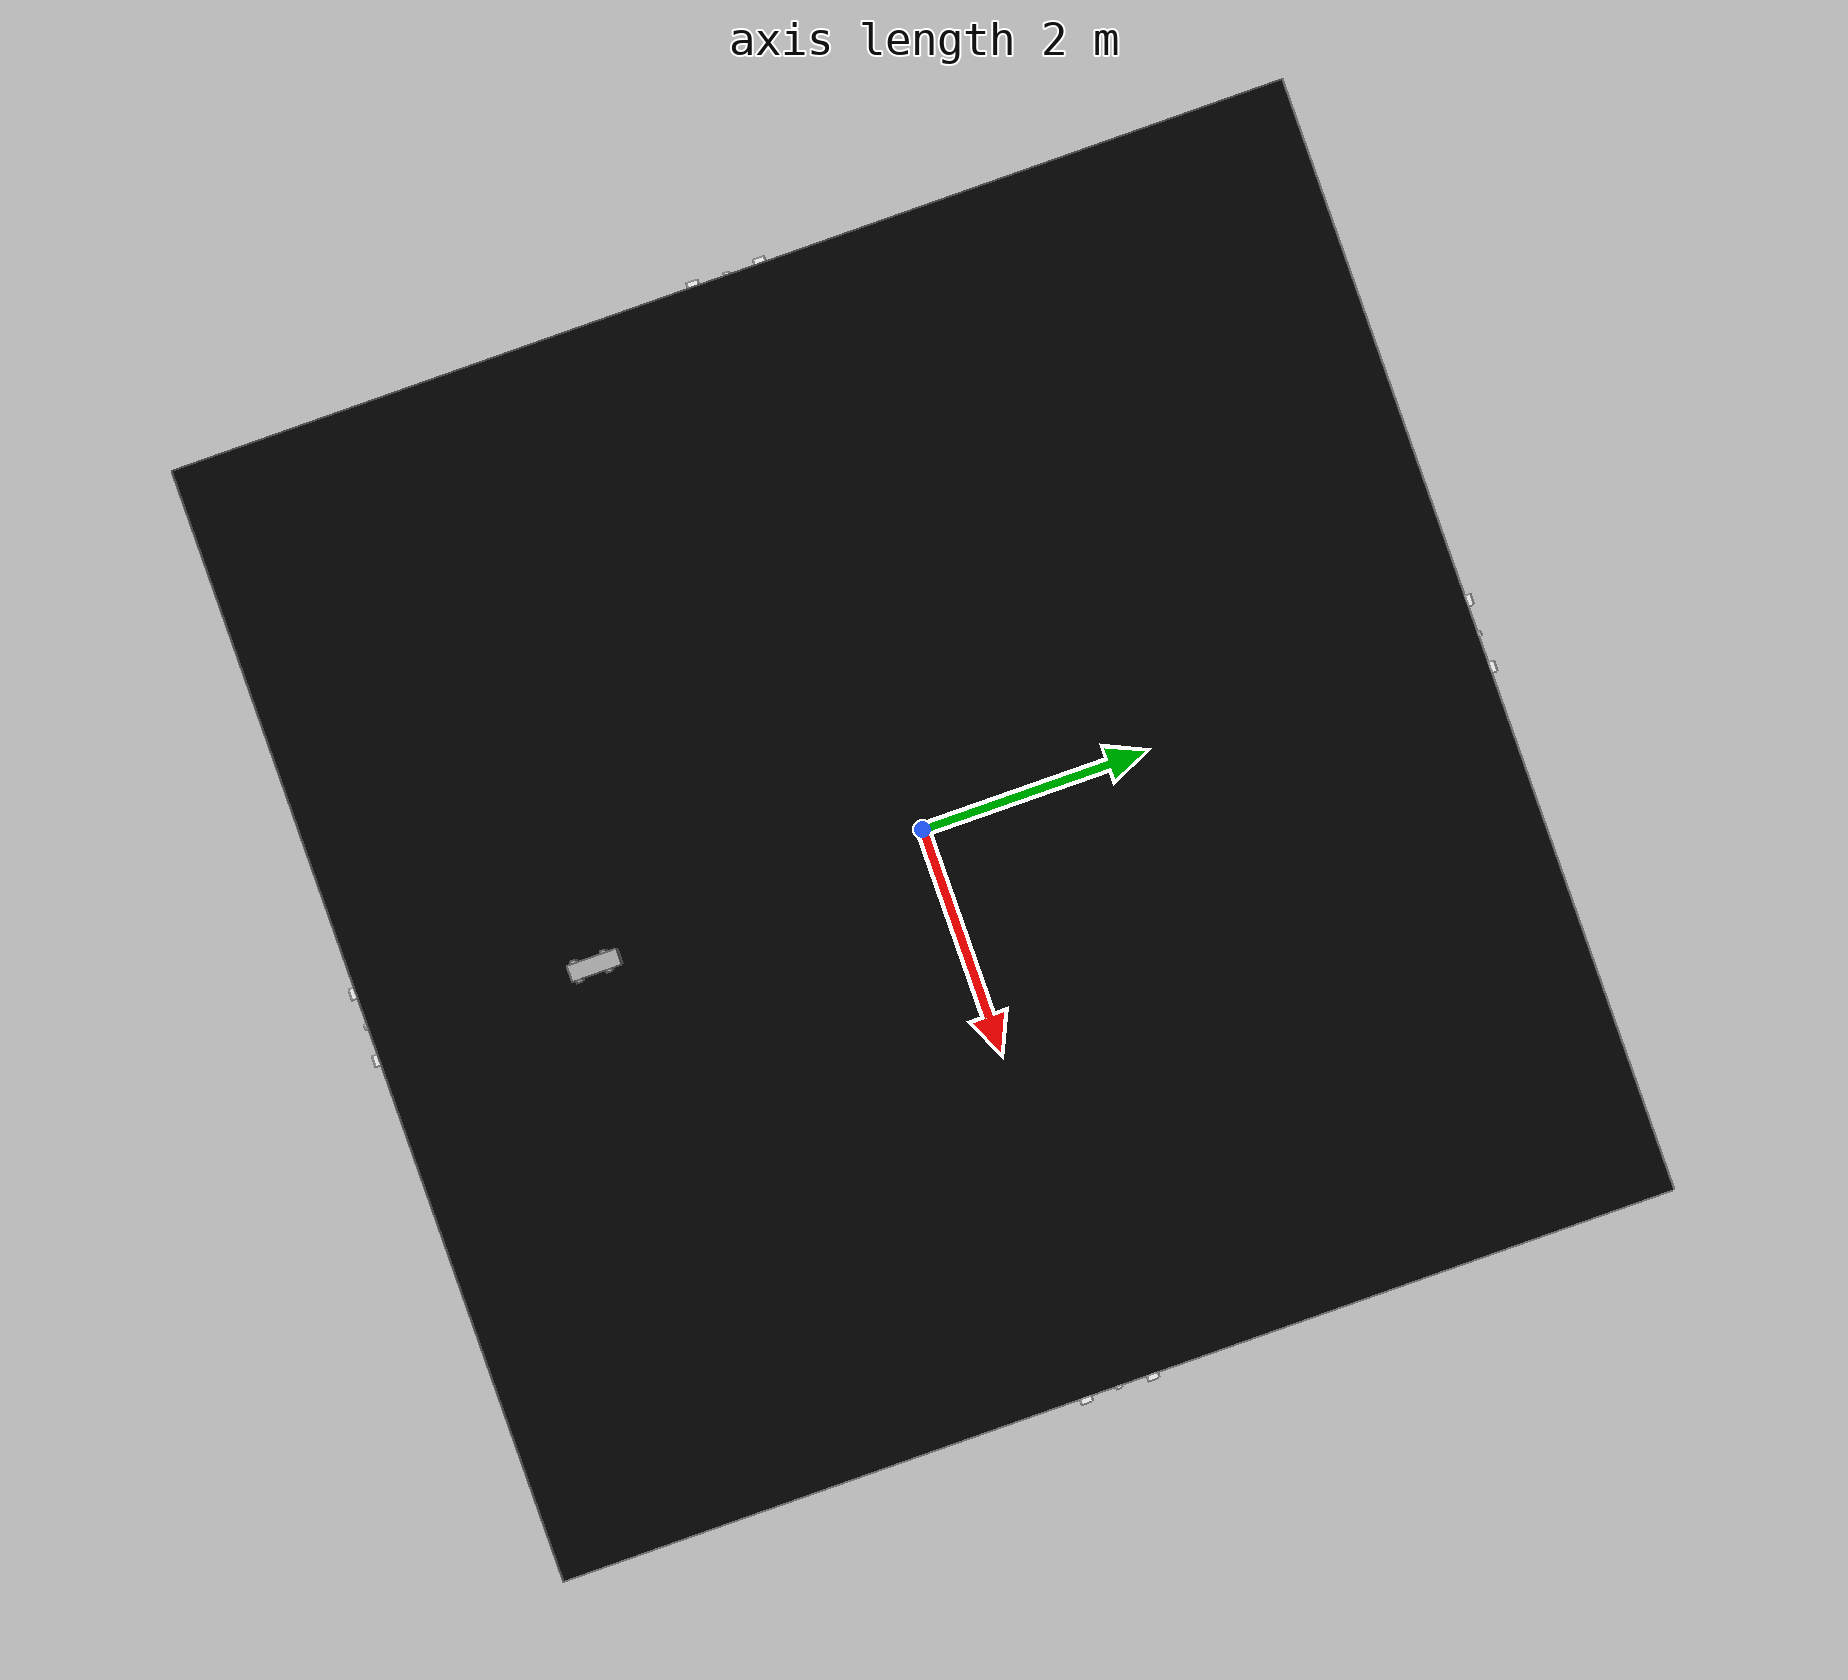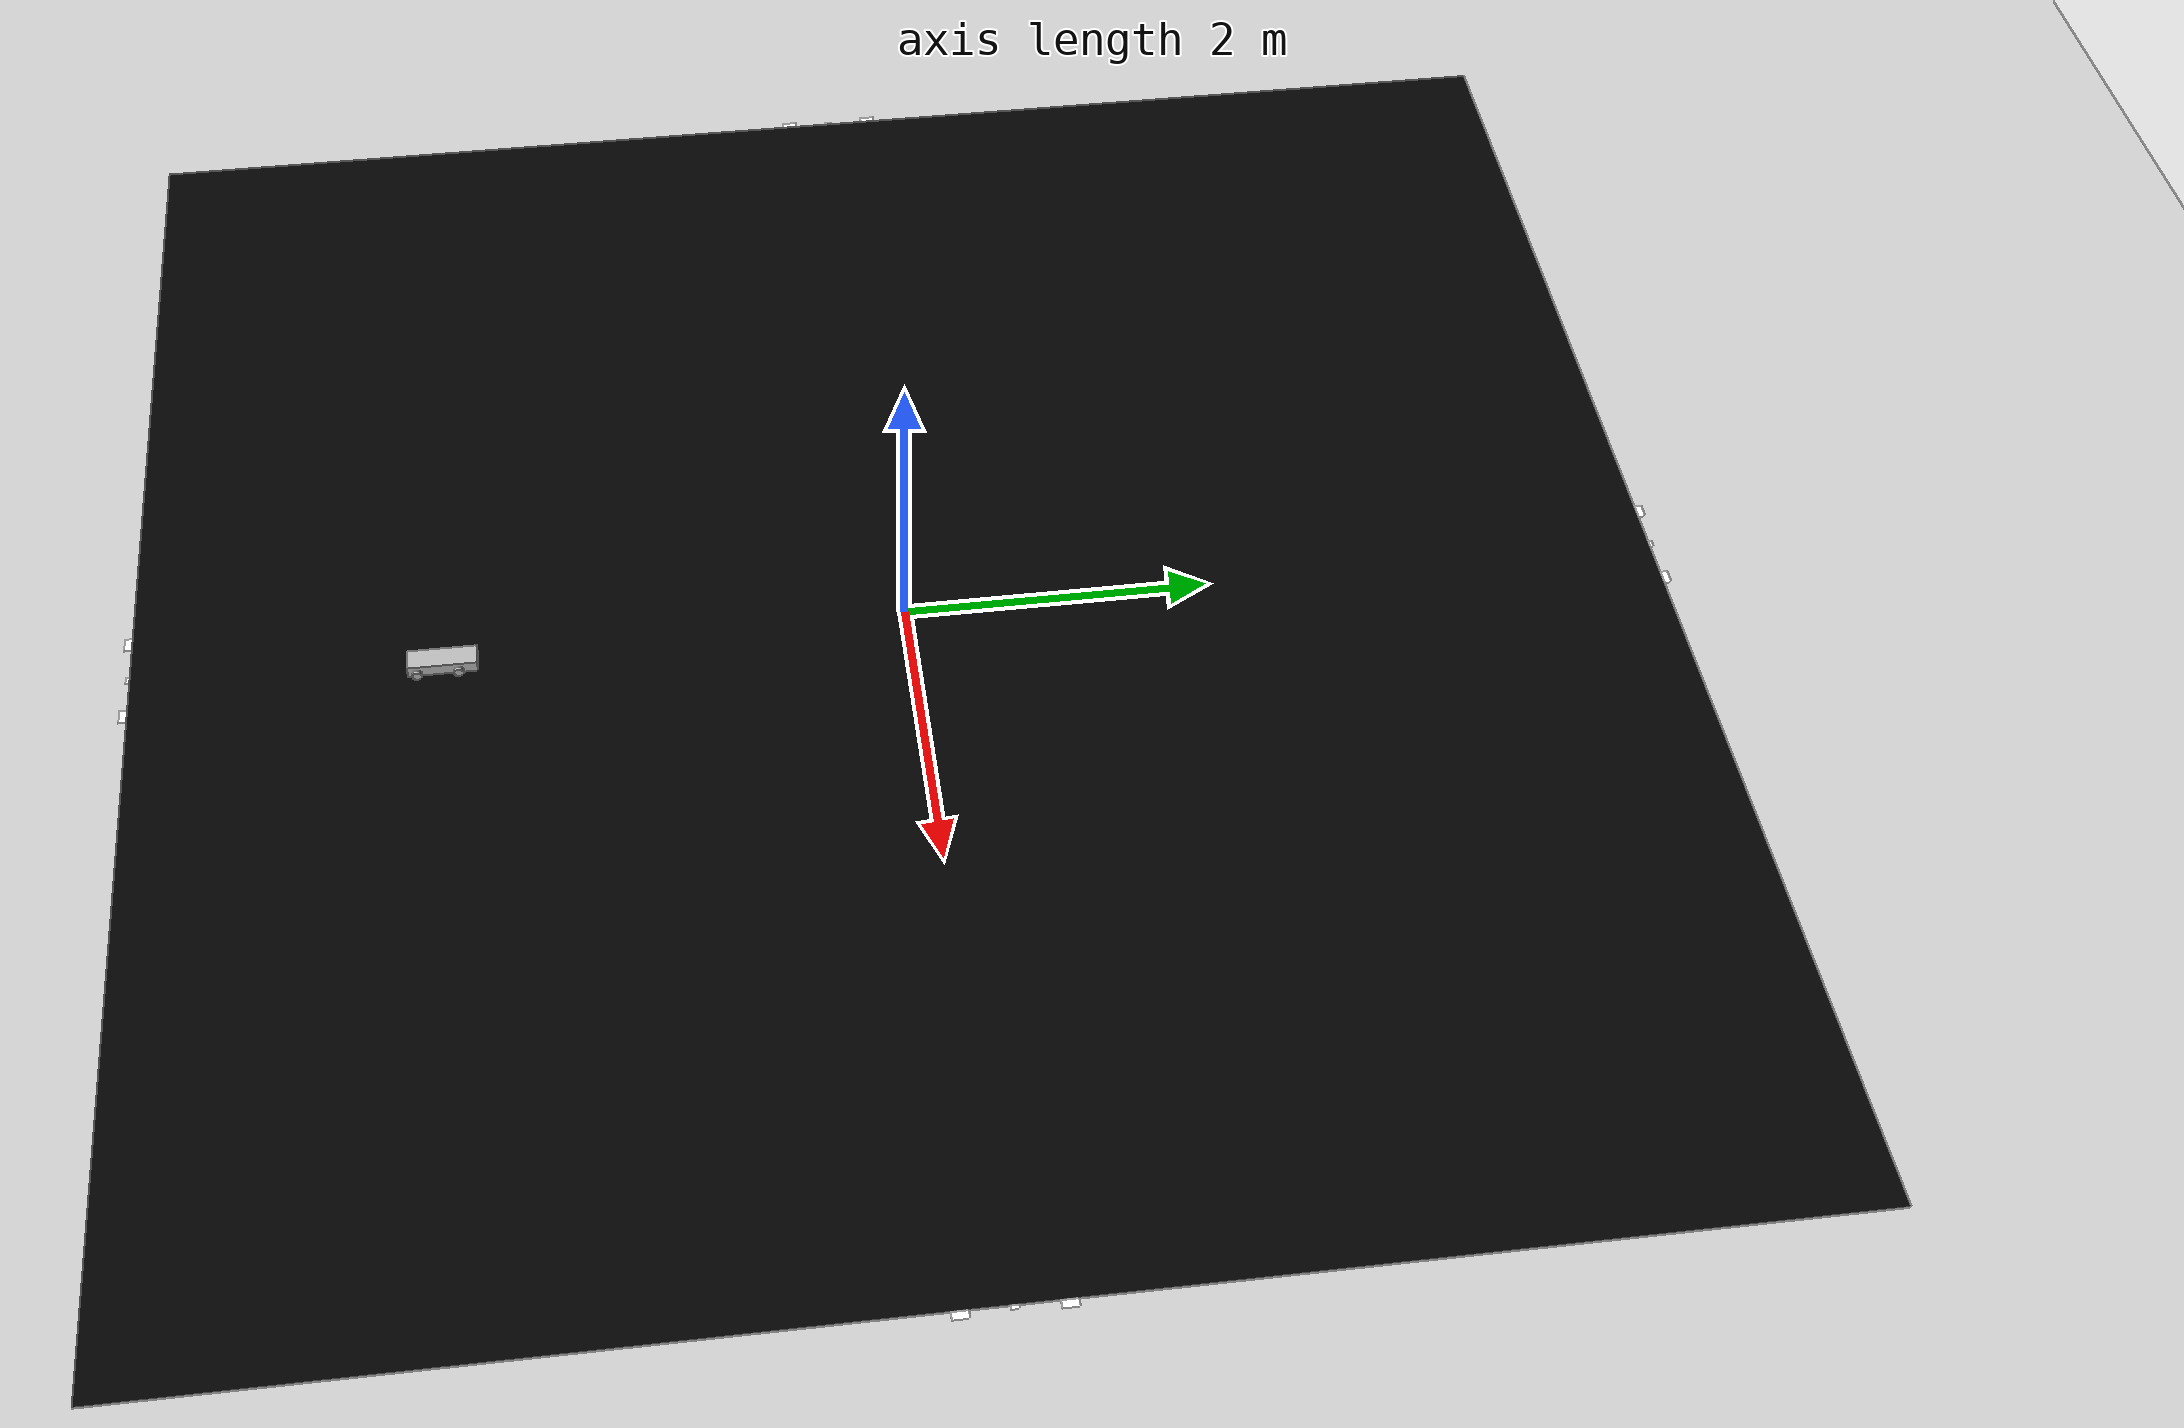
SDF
<?xml version="1.0" ?>
<sdf version="1.4">
  <world name="default">
    <include>
      <uri>model://ground_plane</uri>
    </include>
    <include>
      <uri>model://sun</uri>
    </include>
    <include>
      <uri>model://AutoNOMOS_mini</uri>
      <pose>.15 -3 0 0 0 0 </pose>
    </include>
    <include>
      <uri>model://AutoNOMOS_mini_Intersection</uri>
    </include>
  </world>
</sdf>

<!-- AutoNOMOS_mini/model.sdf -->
<sdf version='1.5'>
  <model name='AutoNOMOS_mini'>
    <link name="chassis">
      <pose>0 0 0.1 0 0 0</pose>
      <inertial>
        <mass>2</mass>
        <inertia>
          <ixx>0.13628333</ixx>
          <iyy>0.02683733</iyy>
          <izz>0.15458733</izz>
          <ixy>0.04094</ixy>
          <ixz>0.00736</ixz>
          <iyz>0.0178</iyz>
        </inertia>
      </inertial>
      <collision name="collision">
        <geometry>
          <box>
            <size>.130 .445 .080</size>
          </box>
        </geometry>
        <surface>
          <friction>
            <ode>
              <mu>100</mu>
              <mu2>50</mu2>
            </ode>
          </friction>
        </surface>
      </collision>
      <visual name="chassis_visual">
        <cast_shadows>false</cast_shadows>
        <geometry>
          <box>
            <size>.144 .445 .08</size>
          </box>
        </geometry>
        </visual>
    </link>

    <link name="wheel1">
      <pose>0.07425 .1035 0.08 0 1.57075 0</pose>
      <inertial>
        <mass>0.05</mass>
        <inertia>
          <ixx>0.00002045</ixx>
          <iyy>0.00002045</iyy>
          <izz>0.000024025</izz>
          <ixy>0</ixy>
          <ixz>0</ixz>
          <iyz>0</iyz>
        </inertia>
      </inertial>
      <collision name="collision">
        <geometry>
          <cylinder>
          	<radius> .031 </radius>
            <length> .045 </length>
          </cylinder>
        </geometry>
        <surface>
          <friction>
            <ode>
              <mu>100</mu>
              <mu2>50</mu2>
            </ode>
          </friction>
        </surface>
      </collision>
      <visual name="wheel1_visual">
        <cast_shadows>false</cast_shadows>
        <geometry>
          <cylinder>
          	<radius> .031 </radius>
            <length> .045 </length>
          </cylinder>
        </geometry>
        </visual>
    </link>

    <link name="wheel2">
      <pose>-0.07425 .1035 0.08 0 1.57075 0</pose>
      <inertial>
        <mass>0.05</mass>
        <inertia>
          <ixx>0.00002045</ixx>
          <iyy>0.00002045</iyy>
          <izz>0.000024025</izz>
          <ixy>0</ixy>
          <ixz>0</ixz>
          <iyz>0</iyz>
        </inertia>
      </inertial>
      <collision name="collision">
        <geometry>
          <cylinder>
          	<radius> .031 </radius>
            <length> .045 </length>
          </cylinder>
        </geometry>
        <surface>
          <friction>
            <ode>
              <mu>100</mu>
              <mu2>50</mu2>
            </ode>
          </friction>
        </surface>
      </collision>
      <visual name="wheel2_visual">
        <cast_shadows>false</cast_shadows>
        <geometry>
          <cylinder>
          	<radius> .031 </radius>
            <length> .045 </length>
          </cylinder>
        </geometry>
        </visual>
    </link>

    <link name="wheel3">
      <pose>0.07425 -.1625 0.08 0 1.57075 0</pose>
      <inertial>
        <mass>0.05</mass>
        <inertia>
          <ixx>0.00002045</ixx>
          <iyy>0.00002045</iyy>
          <izz>0.000024025</izz>
          <ixy>0</ixy>
          <ixz>0</ixz>
          <iyz>0</iyz>
        </inertia>
      </inertial>
      <collision name="collision">
        <geometry>
          <cylinder>
          	<radius> .031 </radius>
            <length> .045 </length>
          </cylinder>
        </geometry>
        <surface>
          <friction>
            <ode>
              <mu>100</mu>
              <mu2>50</mu2>
            </ode>
          </friction>
        </surface>
      </collision>
      <visual name="wheel3_visual">
        <cast_shadows>false</cast_shadows>
        <geometry>
          <cylinder>
          	<radius> .031 </radius>
            <length> .045 </length>
          </cylinder>
        </geometry>
        </visual>
    </link>

    <link name="wheel4">
      <pose>-0.07425 -.1625 0.08 0 1.57075 0</pose>
      <inertial>
        <mass>0.05</mass>
        <inertia>
          <ixx>0.00002045</ixx>
          <iyy>0.00002045</iyy>
          <izz>0.000024025</izz>
          <ixy>0</ixy>
          <ixz>0</ixz>
          <iyz>0</iyz>
        </inertia>
      </inertial>
      <collision name="collision">
        <geometry>
          <cylinder>
          	<radius> .031 </radius>
            <length> .045 </length>
          </cylinder>
        </geometry>
        <surface>
          <friction>
            <ode>
              <mu>100</mu>
              <mu2>50</mu2>
            </ode>
          </friction>
        </surface>
      </collision>
      <visual name="wheel4_visual">
        <cast_shadows>false</cast_shadows>
        <geometry>
          <cylinder>
          	<radius> .031 </radius>
            <length> .045 </length>
          </cylinder>
        </geometry>
        </visual>
    </link>

    <joint name='chassis-wheel_JOINT3' type='revolute'>
      <parent>chassis</parent>
      <child>wheel3</child>
      <pose frame=''>0 0 0 0 0 0</pose>
      <axis>
        <xyz>0 0 1</xyz>
        <use_parent_model_frame>0</use_parent_model_frame>
        <limit>
          <lower>-1.79769e+308</lower>
          <upper>1.79769e+308</upper>
          <effort>-1</effort>
          <velocity>-1</velocity>
        </limit>
        <dynamics>
          <spring_reference>0</spring_reference>
          <spring_stiffness>0</spring_stiffness>
          <damping>0</damping>
          <friction>0</friction>
        </dynamics>
      </axis>
      <physics>
        <ode>
          <limit>
            <cfm>0</cfm>
            <erp>0.2</erp>
          </limit>
          <suspension>
            <cfm>0</cfm>
            <erp>0.2</erp>
          </suspension>
        </ode>
      </physics>
    </joint>

    <joint name='chassis-wheel_JOINT4' type='revolute'>
      <parent>chassis</parent>
      <child>wheel4</child>
      <pose frame=''>0 0 0 0 0 0</pose>
      <axis>
        <xyz>0 0 1</xyz>
        <use_parent_model_frame>0</use_parent_model_frame>
        <limit>
          <lower>-1.79769e+308</lower>
          <upper>1.79769e+308</upper>
          <effort>-1</effort>
          <velocity>-1</velocity>
        </limit>
        <dynamics>
          <spring_reference>0</spring_reference>
          <spring_stiffness>0</spring_stiffness>
          <damping>0</damping>
          <friction>0</friction>
        </dynamics>
      </axis>
      <physics>
        <ode>
          <limit>
            <cfm>0</cfm>
            <erp>0.2</erp>
          </limit>
          <suspension>
            <cfm>0</cfm>
            <erp>0.2</erp>
          </suspension>
        </ode>
      </physics>
    </joint>

    <joint name="wheel_right_steer_spin" type="universal">
      <parent>chassis</parent>
      <child>wheel1</child>
      <axis>
        <xyz>-1 0 0</xyz>
        <limit>
          <lower>-0.6108652381980153</lower>
          <upper>0.6108652381980153</upper>
        </limit>
      </axis>
      <axis2>
        <xyz>0 0 1</xyz>
      </axis2>
    </joint>

    <joint name="wheel_left_steer_spin" type="universal">
      <parent>chassis</parent>
      <child>wheel2</child>
      <axis>
        <xyz>-1 0 0</xyz>
        <limit>
          <lower>-0.6108652381980153</lower>
          <upper>0.6108652381980153</upper>
        </limit>
      </axis>
      <axis2>
        <xyz>0 0 1</xyz>
      </axis2>
    </joint>
  </model>
</sdf>

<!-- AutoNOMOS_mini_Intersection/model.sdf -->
<sdf version='1.5'>
  <model name='AutoNOMOS_mini_intersection'>
    <static>true</static>
    <link name="field">
      <pose>0 0 0.01 0 0 0</pose>
      <collision name="collision">
        <geometry>
          <plane>
            <normal>0 0 1</normal>
            <size>10 10</size>
          </plane>
        </geometry>
        <surface>
          <friction>
            <ode>
              <mu>100</mu>
              <mu2>50</mu2>
            </ode>
          </friction>
        </surface>
      </collision>
      <visual name="carpet">
        <cast_shadows>false</cast_shadows>
        <geometry>
          <plane>
            <normal>0 0 1</normal>
            <size>10 10</size>
          </plane>
        </geometry>
        <material>
          <ambient>0 0 0 0</ambient>
          <diffuse>0 0 0 1</diffuse>
          <specular>0 0 0 0</specular>
          <emissive>0 0 0 0</emissive>
        </material>
      </visual>
    </link>
    <link name='L1_p4'>
        <pose>0.4 0 .011 0 0 0</pose>
        <visual name='visual_L1_p4'>
        <cast_shadows>false</cast_shadows>
        <geometry>
          <plane>
            <normal>0 0 1</normal>
            <size>.05 .05</size>
          </plane>
        </geometry>
          <material>
          <ambient>0 0 0 0</ambient>
          <diffuse>1 1 1 0</diffuse>
          <specular>0 0 0 0</specular>
          <emissive>0 0 0 0</emissive>
        </material>
      </visual>
    </link>

          <!-- ####################### NEW LINE ####################### -->
          <link name='L2_p4'>
        <pose>0.4 0.3 .011 0 0 0</pose>
        <visual name='visual_L2_p4'>
        <cast_shadows>false</cast_shadows>
        <geometry>
          <plane>
            <normal>0 0 1</normal>
            <size>.1 .1</size>
          </plane>
        </geometry>
          <material>
          <ambient>0 0 0 0</ambient>
          <diffuse>1 1 1 0</diffuse>
          <specular>0 0 0 0</specular>
          <emissive>0 0 0 0</emissive>
        </material>
      </visual>
    </link>

          <!-- ####################### NEW LINE ####################### -->
          <link name='L3_p4'>
        <pose>0.3 0.4 .011 0 0 0</pose>
        <visual name='visual_L3_p4'>
        <cast_shadows>false</cast_shadows>
        <geometry>
          <plane>
            <normal>0 0 1</normal>
            <size>.1 .1</size>
          </plane>
        </geometry>
          <material>
          <ambient>0 0 0 0</ambient>
          <diffuse>1 1 1 0</diffuse>
          <specular>0 0 0 0</specular>
          <emissive>0 0 0 0</emissive>
        </material>
      </visual>
    </link>

          <!-- ####################### NEW LINE ####################### -->
          <link name='L4_p4'>
        <pose>0 0.4 .011 0 0 0</pose>
        <visual name='visual_L4_p4'>
        <cast_shadows>false</cast_shadows>
        <geometry>
          <plane>
            <normal>0 0 1</normal>
            <size>.05 .05</size>
          </plane>
        </geometry>
          <material>
          <ambient>0 0 0 0</ambient>
          <diffuse>1 1 1 0</diffuse>
          <specular>0 0 0 0</specular>
          <emissive>0 0 0 0</emissive>
        </material>
      </visual>
    </link>

          <!-- ####################### NEW LINE ####################### -->
          <link name='L5_p4'>
        <pose>-0.3 0.4 .011 0 0 0</pose>
        <visual name='visual_L5_p4'>
        <cast_shadows>false</cast_shadows>
        <geometry>
          <plane>
            <normal>0 0 1</normal>
            <size>.1 .1</size>
          </plane>
        </geometry>
          <material>
          <ambient>0 0 0 0</ambient>
          <diffuse>1 1 1 0</diffuse>
          <specular>0 0 0 0</specular>
          <emissive>0 0 0 0</emissive>
        </material>
      </visual>
    </link>

          <!-- ####################### NEW LINE ####################### -->
          <link name='L6_p4'>
        <pose>-0.4 0.3 .011 0 0 0</pose>
        <visual name='visual_L6_p4'>
        <cast_shadows>false</cast_shadows>
        <geometry>
          <plane>
            <normal>0 0 1</normal>
            <size>.1 .1</size>
          </plane>
        </geometry>
          <material>
          <ambient>0 0 0 0</ambient>
          <diffuse>1 1 1 0</diffuse>
          <specular>0 0 0 0</specular>
          <emissive>0 0 0 0</emissive>
        </material>
      </visual>
    </link>

          <!-- ####################### NEW LINE ####################### -->
          <link name='L7_p4'>
        <pose>-0.4 0 .011 0 0 0</pose>
        <visual name='visual_L7_p4'>
        <cast_shadows>false</cast_shadows>
        <geometry>
          <plane>
            <normal>0 0 1</normal>
            <size>.05 .05</size>
          </plane>
        </geometry>
          <material>
          <ambient>0 0 0 0</ambient>
          <diffuse>1 1 1 0</diffuse>
          <specular>0 0 0 0</specular>
          <emissive>0 0 0 0</emissive>
        </material>
      </visual>
    </link>

          <!-- ####################### NEW LINE ####################### -->
          <link name='L8_p4'>
        <pose>-0.4 -0.3 .011 0 0 0</pose>
        <visual name='visual_L8_p4'>
        <cast_shadows>false</cast_shadows>
        <geometry>
          <plane>
            <normal>0 0 1</normal>
            <size>.1 .1</size>
          </plane>
        </geometry>
          <material>
          <ambient>0 0 0 0</ambient>
          <diffuse>1 1 1 0</diffuse>
          <specular>0 0 0 0</specular>
          <emissive>0 0 0 0</emissive>
        </material>
      </visual>
    </link>

          <!-- ####################### NEW LINE ####################### -->
          <link name='L9_p4'>
        <pose>-0.3 -0.4 .011 0 0 0</pose>
        <visual name='visual_L9_p4'>
        <cast_shadows>false</cast_shadows>
        <geometry>
          <plane>
            <normal>0 0 1</normal>
            <size>.1 .1</size>
          </plane>
        </geometry>
          <material>
          <ambient>0 0 0 0</ambient>
          <diffuse>1 1 1 0</diffuse>
          <specular>0 0 0 0</specular>
          <emissive>0 0 0 0</emissive>
        </material>
      </visual>
    </link>

          <!-- ####################### NEW LINE ####################### -->
          <link name='L10_p4'>
        <pose>0 -0.4 .011 0 0 0</pose>
        <visual name='visual_L10_p4'>
        <cast_shadows>false</cast_shadows>
        <geometry>
          <plane>
            <normal>0 0 1</normal>
            <size>.05 .05</size>
          </plane>
        </geometry>
          <material>
          <ambient>0 0 0 0</ambient>
          <diffuse>1 1 1 0</diffuse>
          <specular>0 0 0 0</specular>
          <emissive>0 0 0 0</emissive>
        </material>
      </visual>
    </link>

          <!-- ####################### NEW LINE ####################### -->
          <link name='L11_p4'>
        <pose>0.3 -0.4 .011 0 0 0</pose>
        <visual name='visual_L11_p4'>
        <cast_shadows>false</cast_shadows>
        <geometry>
          <plane>
            <normal>0 0 1</normal>
            <size>.1 .1</size>
          </plane>
        </geometry>
          <material>
          <ambient>0 0 0 0</ambient>
          <diffuse>1 1 1 0</diffuse>
          <specular>0 0 0 0</specular>
          <emissive>0 0 0 0</emissive>
        </material>
      </visual>
    </link>

          <!-- ####################### NEW LINE ####################### -->
          <link name='L12_p4'>
        <pose>0.4 -0.3 .011 0 0 0</pose>
        <visual name='visual_L12_p4'>
        <cast_shadows>false</cast_shadows>
        <geometry>
          <plane>
            <normal>0 0 1</normal>
            <size>.1 .1</size>
          </plane>
        </geometry>
          <material>
          <ambient>0 0 0 0</ambient>
          <diffuse>1 1 1 0</diffuse>
          <specular>0 0 0 0</specular>
          <emissive>0 0 0 0</emissive>
        </material>
      </visual>
    </link>

          <!-- ####################### NEW LINE ####################### -->
<link name='L1_p5'>
        <pose>0.5 0 .011 0 0 0</pose>
        <visual name='visual_L1_p5'>
        <cast_shadows>false</cast_shadows>
        <geometry>
          <plane>
            <normal>0 0 1</normal>
            <size>.05 .05</size>
          </plane>
        </geometry>
          <material>
          <ambient>0 0 0 0</ambient>
          <diffuse>1 1 1 0</diffuse>
          <specular>0 0 0 0</specular>
          <emissive>0 0 0 0</emissive>
        </material>
      </visual>
    </link>

          <!-- ####################### NEW LINE ####################### -->
          <link name='L2_p5'>
        <pose>0.5 0.3 .011 0 0 0</pose>
        <visual name='visual_L2_p5'>
        <cast_shadows>false</cast_shadows>
        <geometry>
          <plane>
            <normal>0 0 1</normal>
            <size>.1 .1</size>
          </plane>
        </geometry>
          <material>
          <ambient>0 0 0 0</ambient>
          <diffuse>1 1 1 0</diffuse>
          <specular>0 0 0 0</specular>
          <emissive>0 0 0 0</emissive>
        </material>
      </visual>
    </link>

          <!-- ####################### NEW LINE ####################### -->
          <link name='L3_p5'>
        <pose>0.3 0.5 .011 0 0 0</pose>
        <visual name='visual_L3_p5'>
        <cast_shadows>false</cast_shadows>
        <geometry>
          <plane>
            <normal>0 0 1</normal>
            <size>.1 .1</size>
          </plane>
        </geometry>
          <material>
          <ambient>0 0 0 0</ambient>
          <diffuse>1 1 1 0</diffuse>
          <specular>0 0 0 0</specular>
          <emissive>0 0 0 0</emissive>
        </material>
      </visual>
    </link>

          <!-- ####################### NEW LINE ####################### -->
          <link name='L4_p5'>
        <pose>0 0.5 .011 0 0 0</pose>
        <visual name='visual_L4_p5'>
        <cast_shadows>false</cast_shadows>
        <geometry>
          <plane>
            <normal>0 0 1</normal>
            <size>.05 .05</size>
          </plane>
        </geometry>
          <material>
          <ambient>0 0 0 0</ambient>
          <diffuse>1 1 1 0</diffuse>
          <specular>0 0 0 0</specular>
          <emissive>0 0 0 0</emissive>
        </material>
      </visual>
    </link>

          <!-- ####################### NEW LINE ####################### -->
          <link name='L5_p5'>
        <pose>-0.3 0.5 .011 0 0 0</pose>
        <visual name='visual_L5_p5'>
        <cast_shadows>false</cast_shadows>
        <geometry>
          <plane>
            <normal>0 0 1</normal>
            <size>.1 .1</size>
          </plane>
        </geometry>
          <material>
          <ambient>0 0 0 0</ambient>
          <diffuse>1 1 1 0</diffuse>
          <specular>0 0 0 0</specular>
          <emissive>0 0 0 0</emissive>
        </material>
      </visual>
    </link>

          <!-- ####################### NEW LINE ####################### -->
          <link name='L6_p5'>
        <pose>-0.5 0.3 .011 0 0 0</pose>
        <visual name='visual_L6_p5'>
        <cast_shadows>false</cast_shadows>
        <geometry>
          <plane>
            <normal>0 0 1</normal>
            <size>.1 .1</size>
          </plane>
        </geometry>
          <material>
          <ambient>0 0 0 0</ambient>
          <diffuse>1 1 1 0</diffuse>
          <specular>0 0 0 0</specular>
          <emissive>0 0 0 0</emissive>
        </material>
      </visual>
    </link>

          <!-- ####################### NEW LINE ####################### -->
          <link name='L7_p5'>
        <pose>-0.5 0 .011 0 0 0</pose>
        <visual name='visual_L7_p5'>
        <cast_shadows>false</cast_shadows>
        <geometry>
          <plane>
            <normal>0 0 1</normal>
            <size>.05 .05</size>
          </plane>
        </geometry>
          <material>
          <ambient>0 0 0 0</ambient>
          <diffuse>1 1 1 0</diffuse>
          <specular>0 0 0 0</specular>
          <emissive>0 0 0 0</emissive>
        </material>
      </visual>
    </link>

          <!-- ####################### NEW LINE ####################### -->
          <link name='L8_p5'>
        <pose>-0.5 -0.3 .011 0 0 0</pose>
        <visual name='visual_L8_p5'>
        <cast_shadows>false</cast_shadows>
        <geometry>
          <plane>
            <normal>0 0 1</normal>
            <size>.1 .1</size>
          </plane>
        </geometry>
          <material>
          <ambient>0 0 0 0</ambient>
          <diffuse>1 1 1 0</diffuse>
          <specular>0 0 0 0</specular>
          <emissive>0 0 0 0</emissive>
        </material>
      </visual>
    </link>

          <!-- ####################### NEW LINE ####################### -->
          <link name='L9_p5'>
        <pose>-0.3 -0.5 .011 0 0 0</pose>
        <visual name='visual_L9_p5'>
        <cast_shadows>false</cast_shadows>
        <geometry>
          <plane>
            <normal>0 0 1</normal>
            <size>.1 .1</size>
          </plane>
        </geometry>
          <material>
          <ambient>0 0 0 0</ambient>
          <diffuse>1 1 1 0</diffuse>
          <specular>0 0 0 0</specular>
          <emissive>0 0 0 0</emissive>
        </material>
      </visual>
    </link>

          <!-- ####################### NEW LINE ####################### -->
          <link name='L10_p5'>
        <pose>0 -0.5 .011 0 0 0</pose>
        <visual name='visual_L10_p5'>
        <cast_shadows>false</cast_shadows>
        <geometry>
          <plane>
            <normal>0 0 1</normal>
            <size>.05 .05</size>
          </plane>
        </geometry>
          <material>
          <ambient>0 0 0 0</ambient>
          <diffuse>1 1 1 0</diffuse>
          <specular>0 0 0 0</specular>
          <emissive>0 0 0 0</emissive>
        </material>
      </visual>
    </link>

          <!-- ####################### NEW LINE ####################### -->
          <link name='L11_p5'>
        <pose>0.3 -0.5 .011 0 0 0</pose>
        <visual name='visual_L11_p5'>
        <cast_shadows>false</cast_shadows>
        <geometry>
          <plane>
            <normal>0 0 1</normal>
            <size>.1 .1</size>
          </plane>
        </geometry>
          <material>
          <ambient>0 0 0 0</ambient>
          <diffuse>1 1 1 0</diffuse>
          <specular>0 0 0 0</specular>
          <emissive>0 0 0 0</emissive>
        </material>
      </visual>
    </link>

          <!-- ####################### NEW LINE ####################### -->
          <link name='L12_p5'>
        <pose>0.5 -0.3 .011 0 0 0</pose>
        <visual name='visual_L12_p5'>
        <cast_shadows>false</cast_shadows>
        <geometry>
          <plane>
            <normal>0 0 1</normal>
            <size>.1 .1</size>
          </plane>
        </geometry>
          <material>
          <ambient>0 0 0 0</ambient>
          <diffuse>1 1 1 0</diffuse>
          <specular>0 0 0 0</specular>
          <emissive>0 0 0 0</emissive>
        </material>
      </visual>
    </link>

          <!-- ####################### NEW LINE ####################### -->
<link name='L1_p6'>
        <pose>0.6 0 .011 0 0 0</pose>
        <visual name='visual_L1_p6'>
        <cast_shadows>false</cast_shadows>
        <geometry>
          <plane>
            <normal>0 0 1</normal>
            <size>.05 .05</size>
          </plane>
        </geometry>
          <material>
          <ambient>0 0 0 0</ambient>
          <diffuse>1 1 1 0</diffuse>
          <specular>0 0 0 0</specular>
          <emissive>0 0 0 0</emissive>
        </material>
      </visual>
    </link>

          <!-- ####################### NEW LINE ####################### -->
          <link name='L2_p6'>
        <pose>0.6 0.3 .011 0 0 0</pose>
        <visual name='visual_L2_p6'>
        <cast_shadows>false</cast_shadows>
        <geometry>
          <plane>
            <normal>0 0 1</normal>
            <size>.1 .1</size>
          </plane>
        </geometry>
          <material>
          <ambient>0 0 0 0</ambient>
          <diffuse>1 1 1 0</diffuse>
          <specular>0 0 0 0</specular>
          <emissive>0 0 0 0</emissive>
        </material>
      </visual>
    </link>

          <!-- ####################### NEW LINE ####################### -->
          <link name='L3_p6'>
        <pose>0.3 0.6 .011 0 0 0</pose>
        <visual name='visual_L3_p6'>
        <cast_shadows>false</cast_shadows>
        <geometry>
          <plane>
            <normal>0 0 1</normal>
            <size>.1 .1</size>
          </plane>
        </geometry>
          <material>
          <ambient>0 0 0 0</ambient>
          <diffuse>1 1 1 0</diffuse>
          <specular>0 0 0 0</specular>
          <emissive>0 0 0 0</emissive>
        </material>
      </visual>
    </link>

          <!-- ####################### NEW LINE ####################### -->
          <link name='L4_p6'>
        <pose>0 0.6 .011 0 0 0</pose>
        <visual name='visual_L4_p6'>
        <cast_shadows>false</cast_shadows>
        <geometry>
          <plane>
            <normal>0 0 1</normal>
            <size>.05 .05</size>
          </plane>
        </geometry>
          <material>
          <ambient>0 0 0 0</ambient>
          <diffuse>1 1 1 0</diffuse>
          <specular>0 0 0 0</specular>
          <emissive>0 0 0 0</emissive>
        </material>
      </visual>
    </link>

          <!-- ####################### NEW LINE ####################### -->
          <link name='L5_p6'>
        <pose>-0.3 0.6 .011 0 0 0</pose>
        <visual name='visual_L5_p6'>
        <cast_shadows>false</cast_shadows>
        <geometry>
          <plane>
            <normal>0 0 1</normal>
            <size>.1 .1</size>
          </plane>
        </geometry>
          <material>
          <ambient>0 0 0 0</ambient>
          <diffuse>1 1 1 0</diffuse>
          <specular>0 0 0 0</specular>
          <emissive>0 0 0 0</emissive>
        </material>
      </visual>
    </link>

          <!-- ####################### NEW LINE ####################### -->
          <link name='L6_p6'>
        <pose>-0.6 0.3 .011 0 0 0</pose>
        <visual name='visual_L6_p6'>
        <cast_shadows>false</cast_shadows>
        <geometry>
          <plane>
            <normal>0 0 1</normal>
            <size>.1 .1</size>
          </plane>
        </geometry>
          <material>
          <ambient>0 0 0 0</ambient>
          <diffuse>1 1 1 0</diffuse>
          <specular>0 0 0 0</specular>
          <emissive>0 0 0 0</emissive>
        </material>
      </visual>
    </link>

          <!-- ####################### NEW LINE ####################### -->
          <link name='L7_p6'>
        <pose>-0.6 0 .011 0 0 0</pose>
        <visual name='visual_L7_p6'>
        <cast_shadows>false</cast_shadows>
        <geometry>
          <plane>
            <normal>0 0 1</normal>
            <size>.05 .05</size>
          </plane>
        </geometry>
          <material>
          <ambient>0 0 0 0</ambient>
          <diffuse>1 1 1 0</diffuse>
          <specular>0 0 0 0</specular>
          <emissive>0 0 0 0</emissive>
        </material>
      </visual>
    </link>

          <!-- ####################### NEW LINE ####################### -->
          <link name='L8_p6'>
        <pose>-0.6 -0.3 .011 0 0 0</pose>
        <visual name='visual_L8_p6'>
        <cast_shadows>false</cast_shadows>
        <geometry>
          <plane>
            <normal>0 0 1</normal>
            <size>.1 .1</size>
          </plane>
        </geometry>
          <material>
          <ambient>0 0 0 0</ambient>
          <diffuse>1 1 1 0</diffuse>
          <specular>0 0 0 0</specular>
          <emissive>0 0 0 0</emissive>
        </material>
      </visual>
    </link>

          <!-- ####################### NEW LINE ####################### -->
          <link name='L9_p6'>
        <pose>-0.3 -0.6 .011 0 0 0</pose>
        <visual name='visual_L9_p6'>
        <cast_shadows>false</cast_shadows>
        <geometry>
          <plane>
            <normal>0 0 1</normal>
            <size>.1 .1</size>
          </plane>
        </geometry>
          <material>
          <ambient>0 0 0 0</ambient>
          <diffuse>1 1 1 0</diffuse>
          <specular>0 0 0 0</specular>
          <emissive>0 0 0 0</emissive>
        </material>
      </visual>
    </link>

          <!-- ####################### NEW LINE ####################### -->
          <link name='L10_p6'>
        <pose>0 -0.6 .011 0 0 0</pose>
        <visual name='visual_L10_p6'>
        <cast_shadows>false</cast_shadows>
        <geometry>
          <plane>
            <normal>0 0 1</normal>
            <size>.05 .05</size>
          </plane>
        </geometry>
          <material>
          <ambient>0 0 0 0</ambient>
          <diffuse>1 1 1 0</diffuse>
          <specular>0 0 0 0</specular>
          <emissive>0 0 0 0</emissive>
        </material>
      </visual>
    </link>

          <!-- ####################### NEW LINE ####################### -->
          <link name='L11_p6'>
        <pose>0.3 -0.6 .011 0 0 0</pose>
        <visual name='visual_L11_p6'>
        <cast_shadows>false</cast_shadows>
        <geometry>
          <plane>
            <normal>0 0 1</normal>
            <size>.1 .1</size>
          </plane>
        </geometry>
          <material>
          <ambient>0 0 0 0</ambient>
          <diffuse>1 1 1 0</diffuse>
          <specular>0 0 0 0</specular>
          <emissive>0 0 0 0</emissive>
        </material>
      </visual>
    </link>

          <!-- ####################### NEW LINE ####################### -->
          <link name='L12_p6'>
        <pose>0.6 -0.3 .011 0 0 0</pose>
        <visual name='visual_L12_p6'>
        <cast_shadows>false</cast_shadows>
        <geometry>
          <plane>
            <normal>0 0 1</normal>
            <size>.1 .1</size>
          </plane>
        </geometry>
          <material>
          <ambient>0 0 0 0</ambient>
          <diffuse>1 1 1 0</diffuse>
          <specular>0 0 0 0</specular>
          <emissive>0 0 0 0</emissive>
        </material>
      </visual>
    </link>

          <!-- ####################### NEW LINE ####################### -->
<link name='L1_p7'>
        <pose>0.7 0 .011 0 0 0</pose>
        <visual name='visual_L1_p7'>
        <cast_shadows>false</cast_shadows>
        <geometry>
          <plane>
            <normal>0 0 1</normal>
            <size>.05 .05</size>
          </plane>
        </geometry>
          <material>
          <ambient>0 0 0 0</ambient>
          <diffuse>1 1 1 0</diffuse>
          <specular>0 0 0 0</specular>
          <emissive>0 0 0 0</emissive>
        </material>
      </visual>
    </link>

          <!-- ####################### NEW LINE ####################### -->
          <link name='L2_p7'>
        <pose>0.7 0.3 .011 0 0 0</pose>
        <visual name='visual_L2_p7'>
        <cast_shadows>false</cast_shadows>
        <geometry>
          <plane>
            <normal>0 0 1</normal>
            <size>.1 .1</size>
          </plane>
        </geometry>
          <material>
          <ambient>0 0 0 0</ambient>
          <diffuse>1 1 1 0</diffuse>
          <specular>0 0 0 0</specular>
          <emissive>0 0 0 0</emissive>
        </material>
      </visual>
    </link>

          <!-- ####################### NEW LINE ####################### -->
          <link name='L3_p7'>
        <pose>0.3 0.7 .011 0 0 0</pose>
        <visual name='visual_L3_p7'>
        <cast_shadows>false</cast_shadows>
        <geometry>
          <plane>
            <normal>0 0 1</normal>
            <size>.1 .1</size>
          </plane>
        </geometry>
          <material>
          <ambient>0 0 0 0</ambient>
          <diffuse>1 1 1 0</diffuse>
          <specular>0 0 0 0</specular>
          <emissive>0 0 0 0</emissive>
        </material>
      </visual>
    </link>

          <!-- ####################### NEW LINE ####################### -->
          <link name='L4_p7'>
        <pose>0 0.7 .011 0 0 0</pose>
        <visual name='visual_L4_p7'>
        <cast_shadows>false</cast_shadows>
        <geometry>
          <plane>
            <normal>0 0 1</normal>
            <size>.05 .05</size>
          </plane>
        </geometry>
          <material>
          <ambient>0 0 0 0</ambient>
          <diffuse>1 1 1 0</diffuse>
          <specular>0 0 0 0</specular>
          <emissive>0 0 0 0</emissive>
        </material>
      </visual>
    </link>

          <!-- ####################### NEW LINE ####################### -->
          <link name='L5_p7'>
        <pose>-0.3 0.7 .011 0 0 0</pose>
        <visual name='visual_L5_p7'>
        <cast_shadows>false</cast_shadows>
        <geometry>
          <plane>
            <normal>0 0 1</normal>
            <size>.1 .1</size>
          </plane>
        </geometry>
          <material>
          <ambient>0 0 0 0</ambient>
          <diffuse>1 1 1 0</diffuse>
          <specular>0 0 0 0</specular>
          <emissive>0 0 0 0</emissive>
        </material>
      </visual>
    </link>

          <!-- ####################### NEW LINE ####################### -->
          <link name='L6_p7'>
        <pose>-0.7 0.3 .011 0 0 0</pose>
        <visual name='visual_L6_p7'>
        <cast_shadows>false</cast_shadows>
        <geometry>
          <plane>
            <normal>0 0 1</normal>
            <size>.1 .1</size>
          </plane>
        </geometry>
          <material>
          <ambient>0 0 0 0</ambient>
          <diffuse>1 1 1 0</diffuse>
          <specular>0 0 0 0</specular>
          <emissive>0 0 0 0</emissive>
        </material>
      </visual>
    </link>

          <!-- ####################### NEW LINE ####################### -->
          <link name='L7_p7'>
        <pose>-0.7 0 .011 0 0 0</pose>
        <visual name='visual_L7_p7'>
        <cast_shadows>false</cast_shadows>
        <geometry>
          <plane>
            <normal>0 0 1</normal>
            <size>.05 .05</size>
          </plane>
        </geometry>
          <material>
          <ambient>0 0 0 0</ambient>
          <diffuse>1 1 1 0</diffuse>
          <specular>0 0 0 0</specular>
          <emissive>0 0 0 0</emissive>
        </material>
      </visual>
    </link>

          <!-- ####################### NEW LINE ####################### -->
          <link name='L8_p7'>
        <pose>-0.7 -0.3 .011 0 0 0</pose>
        <visual name='visual_L8_p7'>
        <cast_shadows>false</cast_shadows>
        <geometry>
          <plane>
            <normal>0 0 1</normal>
            <size>.1 .1</size>
          </plane>
        </geometry>
          <material>
          <ambient>0 0 0 0</ambient>
          <diffuse>1 1 1 0</diffuse>
          <specular>0 0 0 0</specular>
          <emissive>0 0 0 0</emissive>
        </material>
      </visual>
    </link>

          <!-- ####################### NEW LINE ####################### -->
          <link name='L9_p7'>
        <pose>-0.3 -0.7 .011 0 0 0</pose>
        <visual name='visual_L9_p7'>
        <cast_shadows>false</cast_shadows>
        <geometry>
          <plane>
            <normal>0 0 1</normal>
            <size>.1 .1</size>
          </plane>
        </geometry>
          <material>
          <ambient>0 0 0 0</ambient>
          <diffuse>1 1 1 0</diffuse>
          <specular>0 0 0 0</specular>
          <emissive>0 0 0 0</emissive>
        </material>
      </visual>
    </link>

          <!-- ####################### NEW LINE ####################### -->
          <link name='L10_p7'>
        <pose>0 -0.7 .011 0 0 0</pose>
        <visual name='visual_L10_p7'>
        <cast_shadows>false</cast_shadows>
        <geometry>
          <plane>
            <normal>0 0 1</normal>
            <size>.05 .05</size>
          </plane>
        </geometry>
          <material>
          <ambient>0 0 0 0</ambient>
          <diffuse>1 1 1 0</diffuse>
          <specular>0 0 0 0</specular>
          <emissive>0 0 0 0</emissive>
        </material>
      </visual>
    </link>

          <!-- ####################### NEW LINE ####################### -->
          <link name='L11_p7'>
        <pose>0.3 -0.7 .011 0 0 0</pose>
        <visual name='visual_L11_p7'>
        <cast_shadows>false</cast_shadows>
        <geometry>
          <plane>
            <normal>0 0 1</normal>
            <size>.1 .1</size>
          </plane>
        </geometry>
          <material>
          <ambient>0 0 0 0</ambient>
          <diffuse>1 1 1 0</diffuse>
          <specular>0 0 0 0</specular>
          <emissive>0 0 0 0</emissive>
        </material>
      </visual>
    </link>

          <!-- ####################### NEW LINE ####################### -->
          <link name='L12_p7'>
        <pose>0.7 -0.3 .011 0 0 0</pose>
        <visual name='visual_L12_p7'>
        <cast_shadows>false</cast_shadows>
        <geometry>
          <plane>
            <normal>0 0 1</normal>
            <size>.1 .1</size>
          </plane>
        </geometry>
          <material>
          <ambient>0 0 0 0</ambient>
          <diffuse>1 1 1 0</diffuse>
          <specular>0 0 0 0</specular>
          <emissive>0 0 0 0</emissive>
        </material>
      </visual>
    </link>

          <!-- ####################### NEW LINE ####################### -->
<link name='L1_p8'>
        <pose>0.8 0 .011 0 0 0</pose>
        <visual name='visual_L1_p8'>
        <cast_shadows>false</cast_shadows>
        <geometry>
          <plane>
            <normal>0 0 1</normal>
            <size>.05 .05</size>
          </plane>
        </geometry>
          <material>
          <ambient>0 0 0 0</ambient>
          <diffuse>1 1 1 0</diffuse>
          <specular>0 0 0 0</specular>
          <emissive>0 0 0 0</emissive>
        </material>
      </visual>
    </link>

          <!-- ####################### NEW LINE ####################### -->
          <link name='L2_p8'>
        <pose>0.8 0.3 .011 0 0 0</pose>
        <visual name='visual_L2_p8'>
        <cast_shadows>false</cast_shadows>
        <geometry>
          <plane>
            <normal>0 0 1</normal>
            <size>.1 .1</size>
          </plane>
        </geometry>
          <material>
          <ambient>0 0 0 0</ambient>
          <diffuse>1 1 1 0</diffuse>
          <specular>0 0 0 0</specular>
          <emissive>0 0 0 0</emissive>
        </material>
      </visual>
    </link>

          <!-- ####################### NEW LINE ####################### -->
          <link name='L3_p8'>
        <pose>0.3 0.8 .011 0 0 0</pose>
        <visual name='visual_L3_p8'>
        <cast_shadows>false</cast_shadows>
        <geometry>
          <plane>
            <normal>0 0 1</normal>
            <size>.1 .1</size>
          </plane>
        </geometry>
          <material>
          <ambient>0 0 0 0</ambient>
          <diffuse>1 1 1 0</diffuse>
          <specular>0 0 0 0</specular>
          <emissive>0 0 0 0</emissive>
        </material>
      </visual>
    </link>

          <!-- ####################### NEW LINE ####################### -->
          <link name='L4_p8'>
        <pose>0 0.8 .011 0 0 0</pose>
        <visual name='visual_L4_p8'>
        <cast_shadows>false</cast_shadows>
        <geometry>
          <plane>
            <normal>0 0 1</normal>
            <size>.05 .05</size>
          </plane>
        </geometry>
          <material>
          <ambient>0 0 0 0</ambient>
          <diffuse>1 1 1 0</diffuse>
          <specular>0 0 0 0</specular>
          <emissive>0 0 0 0</emissive>
        </material>
      </visual>
    </link>

          <!-- ####################### NEW LINE ####################### -->
          <link name='L5_p8'>
        <pose>-0.3 0.8 .011 0 0 0</pose>
        <visual name='visual_L5_p8'>
        <cast_shadows>false</cast_shadows>
        <geometry>
          <plane>
            <normal>0 0 1</normal>
            <size>.1 .1</size>
          </plane>
        </geometry>
          <material>
          <ambient>0 0 0 0</ambient>
          <diffuse>1 1 1 0</diffuse>
          <specular>0 0 0 0</specular>
          <emissive>0 0 0 0</emissive>
        </material>
      </visual>
    </link>

          <!-- ####################### NEW LINE ####################### -->
          <link name='L6_p8'>
        <pose>-0.8 0.3 .011 0 0 0</pose>
        <visual name='visual_L6_p8'>
        <cast_shadows>false</cast_shadows>
        <geometry>
          <plane>
            <normal>0 0 1</normal>
            <size>.1 .1</size>
          </plane>
        </geometry>
          <material>
          <ambient>0 0 0 0</ambient>
          <diffuse>1 1 1 0</diffuse>
          <specular>0 0 0 0</specular>
          <emissive>0 0 0 0</emissive>
        </material>
      </visual>
    </link>

          <!-- ####################### NEW LINE ####################### -->
          <link name='L7_p8'>
        <pose>-0.8 0 .011 0 0 0</pose>
        <visual name='visual_L7_p8'>
        <cast_shadows>false</cast_shadows>
        <geometry>
          <plane>
            <normal>0 0 1</normal>
            <size>.05 .05</size>
          </plane>
        </geometry>
          <material>
          <ambient>0 0 0 0</ambient>
          <diffuse>1 1 1 0</diffuse>
          <specular>0 0 0 0</specular>
          <emissive>0 0 0 0</emissive>
        </material>
      </visual>
    </link>

          <!-- ####################### NEW LINE ####################### -->
          <link name='L8_p8'>
        <pose>-0.8 -0.3 .011 0 0 0</pose>
        <visual name='visual_L8_p8'>
        <cast_shadows>false</cast_shadows>
        <geometry>
          <plane>
            <normal>0 0 1</normal>
            <size>.1 .1</size>
          </plane>
        </geometry>
          <material>
          <ambient>0 0 0 0</ambient>
          <diffuse>1 1 1 0</diffuse>
          <specular>0 0 0 0</specular>
          <emissive>0 0 0 0</emissive>
        </material>
      </visual>
    </link>

          <!-- ####################### NEW LINE ####################### -->
          <link name='L9_p8'>
        <pose>-0.3 -0.8 .011 0 0 0</pose>
        <visual name='visual_L9_p8'>
        <cast_shadows>false</cast_shadows>
        <geometry>
          <plane>
            <normal>0 0 1</normal>
            <size>.1 .1</size>
          </plane>
        </geometry>
          <material>
          <ambient>0 0 0 0</ambient>
          <diffuse>1 1 1 0</diffuse>
          <specular>0 0 0 0</specular>
          <emissive>0 0 0 0</emissive>
        </material>
      </visual>
    </link>

          <!-- ####################### NEW LINE ####################### -->
          <link name='L10_p8'>
        <pose>0 -0.8 .011 0 0 0</pose>
        <visual name='visual_L10_p8'>
        <cast_shadows>false</cast_shadows>
        <geometry>
          <plane>
            <normal>0 0 1</normal>
            <size>.05 .05</size>
          </plane>
        </geometry>
          <material>
          <ambient>0 0 0 0</ambient>
          <diffuse>1 1 1 0</diffuse>
          <specular>0 0 0 0</specular>
          <emissive>0 0 0 0</emissive>
        </material>
      </visual>
    </link>

          <!-- ####################### NEW LINE ####################### -->
          <link name='L11_p8'>
        <pose>0.3 -0.8 .011 0 0 0</pose>
        <visual name='visual_L11_p8'>
        <cast_shadows>false</cast_shadows>
        <geometry>
          <plane>
            <normal>0 0 1</normal>
            <size>.1 .1</size>
          </plane>
        </geometry>
          <material>
          <ambient>0 0 0 0</ambient>
          <diffuse>1 1 1 0</diffuse>
          <specular>0 0 0 0</specular>
          <emissive>0 0 0 0</emissive>
        </material>
      </visual>
    </link>

          <!-- ####################### NEW LINE ####################### -->
          <link name='L12_p8'>
        <pose>0.8 -0.3 .011 0 0 0</pose>
        <visual name='visual_L12_p8'>
        <cast_shadows>false</cast_shadows>
        <geometry>
          <plane>
            <normal>0 0 1</normal>
            <size>.1 .1</size>
          </plane>
        </geometry>
          <material>
          <ambient>0 0 0 0</ambient>
          <diffuse>1 1 1 0</diffuse>
          <specular>0 0 0 0</specular>
          <emissive>0 0 0 0</emissive>
        </material>
      </visual>
    </link>

          <!-- ####################### NEW LINE ####################### -->
<link name='L1_p9'>
        <pose>0.9 0 .011 0 0 0</pose>
        <visual name='visual_L1_p9'>
        <cast_shadows>false</cast_shadows>
        <geometry>
          <plane>
            <normal>0 0 1</normal>
            <size>.05 .05</size>
          </plane>
        </geometry>
          <material>
          <ambient>0 0 0 0</ambient>
          <diffuse>1 1 1 0</diffuse>
          <specular>0 0 0 0</specular>
          <emissive>0 0 0 0</emissive>
        </material>
      </visual>
    </link>

          <!-- ####################### NEW LINE ####################### -->
          <link name='L2_p9'>
        <pose>0.9 0.3 .011 0 0 0</pose>
        <visual name='visual_L2_p9'>
        <cast_shadows>false</cast_shadows>
        <geometry>
          <plane>
            <normal>0 0 1</normal>
            <size>.1 .1</size>
          </plane>
        </geometry>
          <material>
          <ambient>0 0 0 0</ambient>
          <diffuse>1 1 1 0</diffuse>
          <specular>0 0 0 0</specular>
          <emissive>0 0 0 0</emissive>
        </material>
      </visual>
    </link>

          <!-- ####################### NEW LINE ####################### -->
          <link name='L3_p9'>
        <pose>0.3 0.9 .011 0 0 0</pose>
        <visual name='visual_L3_p9'>
        <cast_shadows>false</cast_shadows>
        <geometry>
          <plane>
            <normal>0 0 1</normal>
            <size>.1 .1</size>
          </plane>
        </geometry>
          <material>
          <ambient>0 0 0 0</ambient>
          <diffuse>1 1 1 0</diffuse>
          <specular>0 0 0 0</specular>
          <emissive>0 0 0 0</emissive>
        </material>
      </visual>
    </link>

          <!-- ####################### NEW LINE ####################### -->
          <link name='L4_p9'>
        <pose>0 0.9 .011 0 0 0</pose>
        <visual name='visual_L4_p9'>
        <cast_shadows>false</cast_shadows>
        <geometry>
          <plane>
            <normal>0 0 1</normal>
            <size>.05 .05</size>
          </plane>
        </geometry>
          <material>
          <ambient>0 0 0 0</ambient>
          <diffuse>1 1 1 0</diffuse>
          <specular>0 0 0 0</specular>
          <emissive>0 0 0 0</emissive>
        </material>
      </visual>
    </link>

          <!-- ####################### NEW LINE ####################### -->
          <link name='L5_p9'>
        <pose>-0.3 0.9 .011 0 0 0</pose>
        <visual name='visual_L5_p9'>
        <cast_shadows>false</cast_shadows>
        <geometry>
          <plane>
            <normal>0 0 1</normal>
            <size>.1 .1</size>
          </plane>
        </geometry>
          <material>
          <ambient>0 0 0 0</ambient>
          <diffuse>1 1 1 0</diffuse>
          <specular>0 0 0 0</specular>
          <emissive>0 0 0 0</emissive>
        </material>
      </visual>
    </link>

          <!-- ####################### NEW LINE ####################### -->
          <link name='L6_p9'>
        <pose>-0.9 0.3 .011 0 0 0</pose>
        <visual name='visual_L6_p9'>
        <cast_shadows>false</cast_shadows>
        <geometry>
          <plane>
            <normal>0 0 1</normal>
            <size>.1 .1</size>
          </plane>
        </geometry>
          <material>
          <ambient>0 0 0 0</ambient>
          <diffuse>1 1 1 0</diffuse>
          <specular>0 0 0 0</specular>
          <emissive>0 0 0 0</emissive>
        </material>
      </visual>
    </link>

          <!-- ####################### NEW LINE ####################### -->
          <link name='L7_p9'>
        <pose>-0.9 0 .011 0 0 0</pose>
        <visual name='visual_L7_p9'>
        <cast_shadows>false</cast_shadows>
        <geometry>
          <plane>
            <normal>0 0 1</normal>
            <size>.05 .05</size>
          </plane>
        </geometry>
          <material>
          <ambient>0 0 0 0</ambient>
          <diffuse>1 1 1 0</diffuse>
          <specular>0 0 0 0</specular>
          <emissive>0 0 0 0</emissive>
        </material>
      </visual>
    </link>

          <!-- ####################### NEW LINE ####################### -->
          <link name='L8_p9'>
        <pose>-0.9 -0.3 .011 0 0 0</pose>
        <visual name='visual_L8_p9'>
        <cast_shadows>false</cast_shadows>
        <geometry>
          <plane>
            <normal>0 0 1</normal>
            <size>.1 .1</size>
          </plane>
        </geometry>
          <material>
          <ambient>0 0 0 0</ambient>
          <diffuse>1 1 1 0</diffuse>
          <specular>0 0 0 0</specular>
          <emissive>0 0 0 0</emissive>
        </material>
      </visual>
    </link>

          <!-- ####################### NEW LINE ####################### -->
          <link name='L9_p9'>
        <pose>-0.3 -0.9 .011 0 0 0</pose>
        <visual name='visual_L9_p9'>
        <cast_shadows>false</cast_shadows>
        <geometry>
          <plane>
            <normal>0 0 1</normal>
            <size>.1 .1</size>
          </plane>
        </geometry>
          <material>
          <ambient>0 0 0 0</ambient>
          <diffuse>1 1 1 0</diffuse>
          <specular>0 0 0 0</specular>
          <emissive>0 0 0 0</emissive>
        </material>
      </visual>
    </link>

          <!-- ####################### NEW LINE ####################### -->
          <link name='L10_p9'>
        <pose>0 -0.9 .011 0 0 0</pose>
        <visual name='visual_L10_p9'>
        <cast_shadows>false</cast_shadows>
        <geometry>
          <plane>
            <normal>0 0 1</normal>
            <size>.05 .05</size>
          </plane>
        </geometry>
          <material>
          <ambient>0 0 0 0</ambient>
          <diffuse>1 1 1 0</diffuse>
          <specular>0 0 0 0</specular>
          <emissive>0 0 0 0</emissive>
        </material>
      </visual>
    </link>

          <!-- ####################### NEW LINE ####################### -->
          <link name='L11_p9'>
        <pose>0.3 -0.9 .011 0 0 0</pose>
        <visual name='visual_L11_p9'>
        <cast_shadows>false</cast_shadows>
        <geometry>
          <plane>
            <normal>0 0 1</normal>
            <size>.1 .1</size>
          </plane>
        </geometry>
          <material>
          <ambient>0 0 0 0</ambient>
          <diffuse>1 1 1 0</diffuse>
          <specular>0 0 0 0</specular>
          <emissive>0 0 0 0</emissive>
        </material>
      </visual>
    </link>

          <!-- ####################### NEW LINE ####################### -->
          <link name='L12_p9'>
        <pose>0.9 -0.3 .011 0 0 0</pose>
        <visual name='visual_L12_p9'>
        <cast_shadows>false</cast_shadows>
        <geometry>
          <plane>
            <normal>0 0 1</normal>
            <size>.1 .1</size>
          </plane>
        </geometry>
          <material>
          <ambient>0 0 0 0</ambient>
          <diffuse>1 1 1 0</diffuse>
          <specular>0 0 0 0</specular>
          <emissive>0 0 0 0</emissive>
        </material>
      </visual>
    </link>

          <!-- ####################### NEW LINE ####################### -->
<link name='L1_p10'>
        <pose>1 0 .011 0 0 0</pose>
        <visual name='visual_L1_p10'>
        <cast_shadows>false</cast_shadows>
        <geometry>
          <plane>
            <normal>0 0 1</normal>
            <size>.05 .05</size>
          </plane>
        </geometry>
          <material>
          <ambient>0 0 0 0</ambient>
          <diffuse>1 1 1 0</diffuse>
          <specular>0 0 0 0</specular>
          <emissive>0 0 0 0</emissive>
        </material>
      </visual>
    </link>

          <!-- ####################### NEW LINE ####################### -->
          <link name='L2_p10'>
        <pose>1 0.3 .011 0 0 0</pose>
        <visual name='visual_L2_p10'>
        <cast_shadows>false</cast_shadows>
        <geometry>
          <plane>
            <normal>0 0 1</normal>
            <size>.1 .1</size>
          </plane>
        </geometry>
          <material>
          <ambient>0 0 0 0</ambient>
          <diffuse>1 1 1 0</diffuse>
          <specular>0 0 0 0</specular>
          <emissive>0 0 0 0</emissive>
        </material>
      </visual>
    </link>

          <!-- ####################### NEW LINE ####################### -->
          <link name='L3_p10'>
        <pose>0.3 1 .011 0 0 0</pose>
        <visual name='visual_L3_p10'>
        <cast_shadows>false</cast_shadows>
        <geometry>
          <plane>
            <normal>0 0 1</normal>
            <size>.1 .1</size>
          </plane>
        </geometry>
          <material>
          <ambient>0 0 0 0</ambient>
          <diffuse>1 1 1 0</diffuse>
          <specular>0 0 0 0</specular>
          <emissive>0 0 0 0</emissive>
        </material>
      </visual>
    </link>

          <!-- ####################### NEW LINE ####################### -->
          <link name='L4_p10'>
        <pose>0 1 .011 0 0 0</pose>
        <visual name='visual_L4_p10'>
        <cast_shadows>false</cast_shadows>
        <geometry>
          <plane>
            <normal>0 0 1</normal>
            <size>.05 .05</size>
          </plane>
        </geometry>
          <material>
          <ambient>0 0 0 0</ambient>
          <diffuse>1 1 1 0</diffuse>
          <specular>0 0 0 0</specular>
          <emissive>0 0 0 0</emissive>
        </material>
      </visual>
    </link>

          <!-- ####################### NEW LINE ####################### -->
          <link name='L5_p10'>
        <pose>-0.3 1 .011 0 0 0</pose>
        <visual name='visual_L5_p10'>
        <cast_shadows>false</cast_shadows>
        <geometry>
          <plane>
            <normal>0 0 1</normal>
            <size>.1 .1</size>
          </plane>
        </geometry>
          <material>
          <ambient>0 0 0 0</ambient>
          <diffuse>1 1 1 0</diffuse>
          <specular>0 0 0 0</specular>
          <emissive>0 0 0 0</emissive>
        </material>
      </visual>
    </link>

          <!-- ####################### NEW LINE ####################### -->
          <link name='L6_p10'>
        <pose>-1 0.3 .011 0 0 0</pose>
        <visual name='visual_L6_p10'>
        <cast_shadows>false</cast_shadows>
        <geometry>
          <plane>
            <normal>0 0 1</normal>
            <size>.1 .1</size>
          </plane>
        </geometry>
          <material>
          <ambient>0 0 0 0</ambient>
          <diffuse>1 1 1 0</diffuse>
          <specular>0 0 0 0</specular>
          <emissive>0 0 0 0</emissive>
        </material>
      </visual>
    </link>

          <!-- ####################### NEW LINE ####################### -->
          <link name='L7_p10'>
        <pose>-1 0 .011 0 0 0</pose>
        <visual name='visual_L7_p10'>
        <cast_shadows>false</cast_shadows>
        <geometry>
          <plane>
            <normal>0 0 1</normal>
            <size>.05 .05</size>
          </plane>
        </geometry>
          <material>
          <ambient>0 0 0 0</ambient>
          <diffuse>1 1 1 0</diffuse>
          <specular>0 0 0 0</specular>
          <emissive>0 0 0 0</emissive>
        </material>
      </visual>
    </link>

          <!-- ####################### NEW LINE ####################### -->
          <link name='L8_p10'>
        <pose>-1 -0.3 .011 0 0 0</pose>
        <visual name='visual_L8_p10'>
        <cast_shadows>false</cast_shadows>
        <geometry>
          <plane>
            <normal>0 0 1</normal>
            <size>.1 .1</size>
          </plane>
        </geometry>
          <material>
          <ambient>0 0 0 0</ambient>
          <diffuse>1 1 1 0</diffuse>
          <specular>0 0 0 0</specular>
          <emissive>0 0 0 0</emissive>
        </material>
      </visual>
    </link>

          <!-- ####################### NEW LINE ####################### -->
          <link name='L9_p10'>
        <pose>-0.3 -1 .011 0 0 0</pose>
        <visual name='visual_L9_p10'>
        <cast_shadows>false</cast_shadows>
        <geometry>
          <plane>
            <normal>0 0 1</normal>
            <size>.1 .1</size>
          </plane>
        </geometry>
          <material>
          <ambient>0 0 0 0</ambient>
          <diffuse>1 1 1 0</diffuse>
          <specular>0 0 0 0</specular>
          <emissive>0 0 0 0</emissive>
        </material>
      </visual>
    </link>

          <!-- ####################### NEW LINE ####################### -->
          <link name='L10_p10'>
        <pose>0 -1 .011 0 0 0</pose>
        <visual name='visual_L10_p10'>
        <cast_shadows>false</cast_shadows>
        <geometry>
          <plane>
            <normal>0 0 1</normal>
            <size>.05 .05</size>
          </plane>
        </geometry>
          <material>
          <ambient>0 0 0 0</ambient>
          <diffuse>1 1 1 0</diffuse>
          <specular>0 0 0 0</specular>
          <emissive>0 0 0 0</emissive>
        </material>
      </visual>
    </link>

          <!-- ####################### NEW LINE ####################### -->
          <link name='L11_p10'>
        <pose>0.3 -1 .011 0 0 0</pose>
        <visual name='visual_L11_p10'>
        <cast_shadows>false</cast_shadows>
        <geometry>
          <plane>
            <normal>0 0 1</normal>
            <size>.1 .1</size>
          </plane>
        </geometry>
          <material>
          <ambient>0 0 0 0</ambient>
          <diffuse>1 1 1 0</diffuse>
          <specular>0 0 0 0</specular>
          <emissive>0 0 0 0</emissive>
        </material>
      </visual>
    </link>

          <!-- ####################### NEW LINE ####################### -->
          <link name='L12_p10'>
        <pose>1 -0.3 .011 0 0 0</pose>
        <visual name='visual_L12_p10'>
        <cast_shadows>false</cast_shadows>
        <geometry>
          <plane>
            <normal>0 0 1</normal>
            <size>.1 .1</size>
          </plane>
        </geometry>
          <material>
          <ambient>0 0 0 0</ambient>
          <diffuse>1 1 1 0</diffuse>
          <specular>0 0 0 0</specular>
          <emissive>0 0 0 0</emissive>
        </material>
      </visual>
    </link>

          <!-- ####################### NEW LINE ####################### -->
<link name='L1_p11'>
        <pose>1.1 0 .011 0 0 0</pose>
        <visual name='visual_L1_p11'>
        <cast_shadows>false</cast_shadows>
        <geometry>
          <plane>
            <normal>0 0 1</normal>
            <size>.05 .05</size>
          </plane>
        </geometry>
          <material>
          <ambient>0 0 0 0</ambient>
          <diffuse>1 1 1 0</diffuse>
          <specular>0 0 0 0</specular>
          <emissive>0 0 0 0</emissive>
        </material>
      </visual>
    </link>

          <!-- ####################### NEW LINE ####################### -->
          <link name='L2_p11'>
        <pose>1.1 0.3 .011 0 0 0</pose>
        <visual name='visual_L2_p11'>
        <cast_shadows>false</cast_shadows>
        <geometry>
          <plane>
            <normal>0 0 1</normal>
            <size>.1 .1</size>
          </plane>
        </geometry>
          <material>
          <ambient>0 0 0 0</ambient>
          <diffuse>1 1 1 0</diffuse>
          <specular>0 0 0 0</specular>
          <emissive>0 0 0 0</emissive>
        </material>
      </visual>
    </link>

          <!-- ####################### NEW LINE ####################### -->
          <link name='L3_p11'>
        <pose>0.3 1.1 .011 0 0 0</pose>
        <visual name='visual_L3_p11'>
        <cast_shadows>false</cast_shadows>
        <geometry>
          <plane>
            <normal>0 0 1</normal>
            <size>.1 .1</size>
          </plane>
        </geometry>
          <material>
          <ambient>0 0 0 0</ambient>
          <diffuse>1 1 1 0</diffuse>
          <specular>0 0 0 0</specular>
          <emissive>0 0 0 0</emissive>
        </material>
      </visual>
    </link>

          <!-- ####################### NEW LINE ####################### -->
          <link name='L4_p11'>
        <pose>0 1.1 .011 0 0 0</pose>
        <visual name='visual_L4_p11'>
        <cast_shadows>false</cast_shadows>
        <geometry>
          <plane>
            <normal>0 0 1</normal>
            <size>.05 .05</size>
          </plane>
        </geometry>
          <material>
          <ambient>0 0 0 0</ambient>
          <diffuse>1 1 1 0</diffuse>
          <specular>0 0 0 0</specular>
          <emissive>0 0 0 0</emissive>
        </material>
      </visual>
    </link>

          <!-- ####################### NEW LINE ####################### -->
          <link name='L5_p11'>
        <pose>-0.3 1.1 .011 0 0 0</pose>
        <visual name='visual_L5_p11'>
        <cast_shadows>false</cast_shadows>
        <geometry>
          <plane>
            <normal>0 0 1</normal>
            <size>.1 .1</size>
          </plane>
        </geometry>
          <material>
          <ambient>0 0 0 0</ambient>
          <diffuse>1 1 1 0</diffuse>
          <specular>0 0 0 0</specular>
          <emissive>0 0 0 0</emissive>
        </material>
      </visual>
    </link>

          <!-- ####################### NEW LINE ####################### -->
          <link name='L6_p11'>
        <pose>-1.1 0.3 .011 0 0 0</pose>
        <visual name='visual_L6_p11'>
        <cast_shadows>false</cast_shadows>
        <geometry>
          <plane>
            <normal>0 0 1</normal>
            <size>.1 .1</size>
          </plane>
        </geometry>
          <material>
          <ambient>0 0 0 0</ambient>
          <diffuse>1 1 1 0</diffuse>
          <specular>0 0 0 0</specular>
          <emissive>0 0 0 0</emissive>
        </material>
      </visual>
    </link>

          <!-- ####################### NEW LINE ####################### -->
          <link name='L7_p11'>
        <pose>-1.1 0 .011 0 0 0</pose>
        <visual name='visual_L7_p11'>
        <cast_shadows>false</cast_shadows>
        <geometry>
          <plane>
            <normal>0 0 1</normal>
            <size>.05 .05</size>
          </plane>
        </geometry>
          <material>
          <ambient>0 0 0 0</ambient>
          <diffuse>1 1 1 0</diffuse>
          <specular>0 0 0 0</specular>
          <emissive>0 0 0 0</emissive>
        </material>
      </visual>
    </link>

          <!-- ####################### NEW LINE ####################### -->
          <link name='L8_p11'>
        <pose>-1.1 -0.3 .011 0 0 0</pose>
        <visual name='visual_L8_p11'>
        <cast_shadows>false</cast_shadows>
        <geometry>
          <plane>
            <normal>0 0 1</normal>
            <size>.1 .1</size>
          </plane>
        </geometry>
          <material>
          <ambient>0 0 0 0</ambient>
          <diffuse>1 1 1 0</diffuse>
          <specular>0 0 0 0</specular>
          <emissive>0 0 0 0</emissive>
        </material>
      </visual>
    </link>

          <!-- ####################### NEW LINE ####################### -->
          <link name='L9_p11'>
        <pose>-0.3 -1.1 .011 0 0 0</pose>
        <visual name='visual_L9_p11'>
        <cast_shadows>false</cast_shadows>
        <geometry>
          <plane>
            <normal>0 0 1</normal>
            <size>.1 .1</size>
          </plane>
        </geometry>
          <material>
          <ambient>0 0 0 0</ambient>
          <diffuse>1 1 1 0</diffuse>
          <specular>0 0 0 0</specular>
          <emissive>0 0 0 0</emissive>
        </material>
      </visual>
    </link>

          <!-- ####################### NEW LINE ####################### -->
          <link name='L10_p11'>
        <pose>0 -1.1 .011 0 0 0</pose>
        <visual name='visual_L10_p11'>
        <cast_shadows>false</cast_shadows>
        <geometry>
          <plane>
            <normal>0 0 1</normal>
            <size>.05 .05</size>
          </plane>
        </geometry>
          <material>
          <ambient>0 0 0 0</ambient>
          <diffuse>1 1 1 0</diffuse>
          <specular>0 0 0 0</specular>
          <emissive>0 0 0 0</emissive>
        </material>
      </visual>
    </link>

          <!-- ####################### NEW LINE ####################### -->
          <link name='L11_p11'>
        <pose>0.3 -1.1 .011 0 0 0</pose>
        <visual name='visual_L11_p11'>
        <cast_shadows>false</cast_shadows>
        <geometry>
          <plane>
            <normal>0 0 1</normal>
            <size>.1 .1</size>
          </plane>
        </geometry>
          <material>
          <ambient>0 0 0 0</ambient>
          <diffuse>1 1 1 0</diffuse>
          <specular>0 0 0 0</specular>
          <emissive>0 0 0 0</emissive>
        </material>
      </visual>
    </link>

          <!-- ####################### NEW LINE ####################### -->
          <link name='L12_p11'>
        <pose>1.1 -0.3 .011 0 0 0</pose>
        <visual name='visual_L12_p11'>
        <cast_shadows>false</cast_shadows>
        <geometry>
          <plane>
            <normal>0 0 1</normal>
            <size>.1 .1</size>
          </plane>
        </geometry>
          <material>
          <ambient>0 0 0 0</ambient>
          <diffuse>1 1 1 0</diffuse>
          <specular>0 0 0 0</specular>
          <emissive>0 0 0 0</emissive>
        </material>
      </visual>
    </link>

          <!-- ####################### NEW LINE ####################### -->
<link name='L1_p12'>
        <pose>1.2 0 .011 0 0 0</pose>
        <visual name='visual_L1_p12'>
        <cast_shadows>false</cast_shadows>
        <geometry>
          <plane>
            <normal>0 0 1</normal>
            <size>.05 .05</size>
          </plane>
        </geometry>
          <material>
          <ambient>0 0 0 0</ambient>
          <diffuse>1 1 1 0</diffuse>
          <specular>0 0 0 0</specular>
          <emissive>0 0 0 0</emissive>
        </material>
      </visual>
    </link>

          <!-- ####################### NEW LINE ####################### -->
          <link name='L2_p12'>
        <pose>1.2 0.3 .011 0 0 0</pose>
        <visual name='visual_L2_p12'>
        <cast_shadows>false</cast_shadows>
        <geometry>
          <plane>
            <normal>0 0 1</normal>
            <size>.1 .1</size>
          </plane>
        </geometry>
          <material>
          <ambient>0 0 0 0</ambient>
          <diffuse>1 1 1 0</diffuse>
          <specular>0 0 0 0</specular>
          <emissive>0 0 0 0</emissive>
        </material>
      </visual>
    </link>

          <!-- ####################### NEW LINE ####################### -->
          <link name='L3_p12'>
        <pose>0.3 1.2 .011 0 0 0</pose>
        <visual name='visual_L3_p12'>
        <cast_shadows>false</cast_shadows>
        <geometry>
          <plane>
            <normal>0 0 1</normal>
            <size>.1 .1</size>
          </plane>
        </geometry>
          <material>
          <ambient>0 0 0 0</ambient>
          <diffuse>1 1 1 0</diffuse>
          <specular>0 0 0 0</specular>
          <emissive>0 0 0 0</emissive>
        </material>
      </visual>
    </link>

          <!-- ####################### NEW LINE ####################### -->
          <link name='L4_p12'>
        <pose>0 1.2 .011 0 0 0</pose>
        <visual name='visual_L4_p12'>
        <cast_shadows>false</cast_shadows>
        <geometry>
          <plane>
            <normal>0 0 1</normal>
            <size>.05 .05</size>
          </plane>
        </geometry>
          <material>
          <ambient>0 0 0 0</ambient>
          <diffuse>1 1 1 0</diffuse>
          <specular>0 0 0 0</specular>
          <emissive>0 0 0 0</emissive>
        </material>
      </visual>
    </link>

          <!-- ####################### NEW LINE ####################### -->
          <link name='L5_p12'>
        <pose>-0.3 1.2 .011 0 0 0</pose>
        <visual name='visual_L5_p12'>
        <cast_shadows>false</cast_shadows>
        <geometry>
          <plane>
            <normal>0 0 1</normal>
            <size>.1 .1</size>
          </plane>
        </geometry>
          <material>
          <ambient>0 0 0 0</ambient>
          <diffuse>1 1 1 0</diffuse>
          <specular>0 0 0 0</specular>
          <emissive>0 0 0 0</emissive>
        </material>
      </visual>
    </link>

          <!-- ####################### NEW LINE ####################### -->
          <link name='L6_p12'>
        <pose>-1.2 0.3 .011 0 0 0</pose>
        <visual name='visual_L6_p12'>
        <cast_shadows>false</cast_shadows>
        <geometry>
          <plane>
            <normal>0 0 1</normal>
            <size>.1 .1</size>
          </plane>
        </geometry>
          <material>
          <ambient>0 0 0 0</ambient>
          <diffuse>1 1 1 0</diffuse>
          <specular>0 0 0 0</specular>
          <emissive>0 0 0 0</emissive>
        </material>
      </visual>
    </link>

          <!-- ####################### NEW LINE ####################### -->
          <link name='L7_p12'>
        <pose>-1.2 0 .011 0 0 0</pose>
        <visual name='visual_L7_p12'>
        <cast_shadows>false</cast_shadows>
        <geometry>
          <plane>
            <normal>0 0 1</normal>
            <size>.05 .05</size>
          </plane>
        </geometry>
          <material>
          <ambient>0 0 0 0</ambient>
          <diffuse>1 1 1 0</diffuse>
          <specular>0 0 0 0</specular>
          <emissive>0 0 0 0</emissive>
        </material>
      </visual>
    </link>

          <!-- ####################### NEW LINE ####################### -->
          <link name='L8_p12'>
        <pose>-1.2 -0.3 .011 0 0 0</pose>
        <visual name='visual_L8_p12'>
        <cast_shadows>false</cast_shadows>
        <geometry>
          <plane>
            <normal>0 0 1</normal>
            <size>.1 .1</size>
          </plane>
        </geometry>
          <material>
          <ambient>0 0 0 0</ambient>
          <diffuse>1 1 1 0</diffuse>
          <specular>0 0 0 0</specular>
          <emissive>0 0 0 0</emissive>
        </material>
      </visual>
    </link>

          <!-- ####################### NEW LINE ####################### -->
          <link name='L9_p12'>
        <pose>-0.3 -1.2 .011 0 0 0</pose>
        <visual name='visual_L9_p12'>
        <cast_shadows>false</cast_shadows>
        <geometry>
          <plane>
            <normal>0 0 1</normal>
            <size>.1 .1</size>
          </plane>
        </geometry>
          <material>
          <ambient>0 0 0 0</ambient>
          <diffuse>1 1 1 0</diffuse>
          <specular>0 0 0 0</specular>
          <emissive>0 0 0 0</emissive>
        </material>
      </visual>
    </link>

          <!-- ####################### NEW LINE ####################### -->
          <link name='L10_p12'>
        <pose>0 -1.2 .011 0 0 0</pose>
        <visual name='visual_L10_p12'>
        <cast_shadows>false</cast_shadows>
        <geometry>
          <plane>
            <normal>0 0 1</normal>
            <size>.05 .05</size>
          </plane>
        </geometry>
          <material>
          <ambient>0 0 0 0</ambient>
          <diffuse>1 1 1 0</diffuse>
          <specular>0 0 0 0</specular>
          <emissive>0 0 0 0</emissive>
        </material>
      </visual>
    </link>

          <!-- ####################### NEW LINE ####################### -->
          <link name='L11_p12'>
        <pose>0.3 -1.2 .011 0 0 0</pose>
        <visual name='visual_L11_p12'>
        <cast_shadows>false</cast_shadows>
        <geometry>
          <plane>
            <normal>0 0 1</normal>
            <size>.1 .1</size>
          </plane>
        </geometry>
          <material>
          <ambient>0 0 0 0</ambient>
          <diffuse>1 1 1 0</diffuse>
          <specular>0 0 0 0</specular>
          <emissive>0 0 0 0</emissive>
        </material>
      </visual>
    </link>

          <!-- ####################### NEW LINE ####################### -->
          <link name='L12_p12'>
        <pose>1.2 -0.3 .011 0 0 0</pose>
        <visual name='visual_L12_p12'>
        <cast_shadows>false</cast_shadows>
        <geometry>
          <plane>
            <normal>0 0 1</normal>
            <size>.1 .1</size>
          </plane>
        </geometry>
          <material>
          <ambient>0 0 0 0</ambient>
          <diffuse>1 1 1 0</diffuse>
          <specular>0 0 0 0</specular>
          <emissive>0 0 0 0</emissive>
        </material>
      </visual>
    </link>

          <!-- ####################### NEW LINE ####################### -->
<link name='L1_p13'>
        <pose>1.3 0 .011 0 0 0</pose>
        <visual name='visual_L1_p13'>
        <cast_shadows>false</cast_shadows>
        <geometry>
          <plane>
            <normal>0 0 1</normal>
            <size>.05 .05</size>
          </plane>
        </geometry>
          <material>
          <ambient>0 0 0 0</ambient>
          <diffuse>1 1 1 0</diffuse>
          <specular>0 0 0 0</specular>
          <emissive>0 0 0 0</emissive>
        </material>
      </visual>
    </link>

          <!-- ####################### NEW LINE ####################### -->
          <link name='L2_p13'>
        <pose>1.3 0.3 .011 0 0 0</pose>
        <visual name='visual_L2_p13'>
        <cast_shadows>false</cast_shadows>
        <geometry>
          <plane>
            <normal>0 0 1</normal>
            <size>.1 .1</size>
          </plane>
        </geometry>
          <material>
          <ambient>0 0 0 0</ambient>
          <diffuse>1 1 1 0</diffuse>
          <specular>0 0 0 0</specular>
          <emissive>0 0 0 0</emissive>
        </material>
      </visual>
    </link>

          <!-- ####################### NEW LINE ####################### -->
          <link name='L3_p13'>
        <pose>0.3 1.3 .011 0 0 0</pose>
        <visual name='visual_L3_p13'>
        <cast_shadows>false</cast_shadows>
        <geometry>
          <plane>
            <normal>0 0 1</normal>
            <size>.1 .1</size>
          </plane>
        </geometry>
          <material>
          <ambient>0 0 0 0</ambient>
          <diffuse>1 1 1 0</diffuse>
          <specular>0 0 0 0</specular>
          <emissive>0 0 0 0</emissive>
        </material>
      </visual>
    </link>

          <!-- ####################### NEW LINE ####################### -->
          <link name='L4_p13'>
        <pose>0 1.3 .011 0 0 0</pose>
        <visual name='visual_L4_p13'>
        <cast_shadows>false</cast_shadows>
        <geometry>
          <plane>
            <normal>0 0 1</normal>
            <size>.05 .05</size>
          </plane>
        </geometry>
          <material>
          <ambient>0 0 0 0</ambient>
          <diffuse>1 1 1 0</diffuse>
          <specular>0 0 0 0</specular>
          <emissive>0 0 0 0</emissive>
        </material>
      </visual>
    </link>

          <!-- ####################### NEW LINE ####################### -->
          <link name='L5_p13'>
        <pose>-0.3 1.3 .011 0 0 0</pose>
        <visual name='visual_L5_p13'>
        <cast_shadows>false</cast_shadows>
        <geometry>
          <plane>
            <normal>0 0 1</normal>
            <size>.1 .1</size>
          </plane>
        </geometry>
          <material>
          <ambient>0 0 0 0</ambient>
          <diffuse>1 1 1 0</diffuse>
          <specular>0 0 0 0</specular>
          <emissive>0 0 0 0</emissive>
        </material>
      </visual>
    </link>

          <!-- ####################### NEW LINE ####################### -->
          <link name='L6_p13'>
        <pose>-1.3 0.3 .011 0 0 0</pose>
        <visual name='visual_L6_p13'>
        <cast_shadows>false</cast_shadows>
        <geometry>
          <plane>
            <normal>0 0 1</normal>
            <size>.1 .1</size>
          </plane>
        </geometry>
          <material>
          <ambient>0 0 0 0</ambient>
          <diffuse>1 1 1 0</diffuse>
          <specular>0 0 0 0</specular>
          <emissive>0 0 0 0</emissive>
        </material>
      </visual>
    </link>

          <!-- ####################### NEW LINE ####################### -->
          <link name='L7_p13'>
        <pose>-1.3 0 .011 0 0 0</pose>
        <visual name='visual_L7_p13'>
        <cast_shadows>false</cast_shadows>
        <geometry>
          <plane>
            <normal>0 0 1</normal>
            <size>.05 .05</size>
          </plane>
        </geometry>
          <material>
          <ambient>0 0 0 0</ambient>
          <diffuse>1 1 1 0</diffuse>
          <specular>0 0 0 0</specular>
          <emissive>0 0 0 0</emissive>
        </material>
      </visual>
    </link>

          <!-- ####################### NEW LINE ####################### -->
          <link name='L8_p13'>
        <pose>-1.3 -0.3 .011 0 0 0</pose>
        <visual name='visual_L8_p13'>
        <cast_shadows>false</cast_shadows>
        <geometry>
          <plane>
            <normal>0 0 1</normal>
            <size>.1 .1</size>
          </plane>
        </geometry>
          <material>
          <ambient>0 0 0 0</ambient>
          <diffuse>1 1 1 0</diffuse>
          <specular>0 0 0 0</specular>
          <emissive>0 0 0 0</emissive>
        </material>
      </visual>
    </link>

          <!-- ####################### NEW LINE ####################### -->
          <link name='L9_p13'>
        <pose>-0.3 -1.3 .011 0 0 0</pose>
        <visual name='visual_L9_p13'>
        <cast_shadows>false</cast_shadows>
        <geometry>
          <plane>
            <normal>0 0 1</normal>
            <size>.1 .1</size>
          </plane>
        </geometry>
          <material>
          <ambient>0 0 0 0</ambient>
          <diffuse>1 1 1 0</diffuse>
          <specular>0 0 0 0</specular>
          <emissive>0 0 0 0</emissive>
        </material>
      </visual>
    </link>

          <!-- ####################### NEW LINE ####################### -->
          <link name='L10_p13'>
        <pose>0 -1.3 .011 0 0 0</pose>
        <visual name='visual_L10_p13'>
        <cast_shadows>false</cast_shadows>
        <geometry>
          <plane>
            <normal>0 0 1</normal>
            <size>.05 .05</size>
          </plane>
        </geometry>
          <material>
          <ambient>0 0 0 0</ambient>
          <diffuse>1 1 1 0</diffuse>
          <specular>0 0 0 0</specular>
          <emissive>0 0 0 0</emissive>
        </material>
      </visual>
    </link>

          <!-- ####################### NEW LINE ####################### -->
          <link name='L11_p13'>
        <pose>0.3 -1.3 .011 0 0 0</pose>
        <visual name='visual_L11_p13'>
        <cast_shadows>false</cast_shadows>
        <geometry>
          <plane>
            <normal>0 0 1</normal>
            <size>.1 .1</size>
          </plane>
        </geometry>
          <material>
          <ambient>0 0 0 0</ambient>
          <diffuse>1 1 1 0</diffuse>
          <specular>0 0 0 0</specular>
          <emissive>0 0 0 0</emissive>
        </material>
      </visual>
    </link>

          <!-- ####################### NEW LINE ####################### -->
          <link name='L12_p13'>
        <pose>1.3 -0.3 .011 0 0 0</pose>
        <visual name='visual_L12_p13'>
        <cast_shadows>false</cast_shadows>
        <geometry>
          <plane>
            <normal>0 0 1</normal>
            <size>.1 .1</size>
          </plane>
        </geometry>
          <material>
          <ambient>0 0 0 0</ambient>
          <diffuse>1 1 1 0</diffuse>
          <specular>0 0 0 0</specular>
          <emissive>0 0 0 0</emissive>
        </material>
      </visual>
    </link>

          <!-- ####################### NEW LINE ####################### -->
<link name='L1_p14'>
        <pose>1.4 0 .011 0 0 0</pose>
        <visual name='visual_L1_p14'>
        <cast_shadows>false</cast_shadows>
        <geometry>
          <plane>
            <normal>0 0 1</normal>
            <size>.05 .05</size>
          </plane>
        </geometry>
          <material>
          <ambient>0 0 0 0</ambient>
          <diffuse>1 1 1 0</diffuse>
          <specular>0 0 0 0</specular>
          <emissive>0 0 0 0</emissive>
        </material>
      </visual>
    </link>

          <!-- ####################### NEW LINE ####################### -->
          <link name='L2_p14'>
        <pose>1.4 0.3 .011 0 0 0</pose>
        <visual name='visual_L2_p14'>
        <cast_shadows>false</cast_shadows>
        <geometry>
          <plane>
            <normal>0 0 1</normal>
            <size>.1 .1</size>
          </plane>
        </geometry>
          <material>
          <ambient>0 0 0 0</ambient>
          <diffuse>1 1 1 0</diffuse>
          <specular>0 0 0 0</specular>
          <emissive>0 0 0 0</emissive>
        </material>
      </visual>
    </link>

          <!-- ####################### NEW LINE ####################### -->
          <link name='L3_p14'>
        <pose>0.3 1.4 .011 0 0 0</pose>
        <visual name='visual_L3_p14'>
        <cast_shadows>false</cast_shadows>
        <geometry>
          <plane>
            <normal>0 0 1</normal>
            <size>.1 .1</size>
          </plane>
        </geometry>
          <material>
          <ambient>0 0 0 0</ambient>
          <diffuse>1 1 1 0</diffuse>
          <specular>0 0 0 0</specular>
          <emissive>0 0 0 0</emissive>
        </material>
      </visual>
    </link>

          <!-- ####################### NEW LINE ####################### -->
          <link name='L4_p14'>
        <pose>0 1.4 .011 0 0 0</pose>
        <visual name='visual_L4_p14'>
        <cast_shadows>false</cast_shadows>
        <geometry>
          <plane>
            <normal>0 0 1</normal>
            <size>.05 .05</size>
          </plane>
        </geometry>
          <material>
          <ambient>0 0 0 0</ambient>
          <diffuse>1 1 1 0</diffuse>
          <specular>0 0 0 0</specular>
          <emissive>0 0 0 0</emissive>
        </material>
      </visual>
    </link>

          <!-- ####################### NEW LINE ####################### -->
          <link name='L5_p14'>
        <pose>-0.3 1.4 .011 0 0 0</pose>
        <visual name='visual_L5_p14'>
        <cast_shadows>false</cast_shadows>
        <geometry>
          <plane>
            <normal>0 0 1</normal>
            <size>.1 .1</size>
          </plane>
        </geometry>
          <material>
          <ambient>0 0 0 0</ambient>
          <diffuse>1 1 1 0</diffuse>
          <specular>0 0 0 0</specular>
          <emissive>0 0 0 0</emissive>
        </material>
      </visual>
    </link>

          <!-- ####################### NEW LINE ####################### -->
          <link name='L6_p14'>
        <pose>-1.4 0.3 .011 0 0 0</pose>
        <visual name='visual_L6_p14'>
        <cast_shadows>false</cast_shadows>
        <geometry>
          <plane>
            <normal>0 0 1</normal>
            <size>.1 .1</size>
          </plane>
        </geometry>
          <material>
          <ambient>0 0 0 0</ambient>
          <diffuse>1 1 1 0</diffuse>
          <specular>0 0 0 0</specular>
          <emissive>0 0 0 0</emissive>
        </material>
      </visual>
    </link>

          <!-- ####################### NEW LINE ####################### -->
          <link name='L7_p14'>
        <pose>-1.4 0 .011 0 0 0</pose>
        <visual name='visual_L7_p14'>
        <cast_shadows>false</cast_shadows>
        <geometry>
          <plane>
            <normal>0 0 1</normal>
            <size>.05 .05</size>
          </plane>
        </geometry>
          <material>
          <ambient>0 0 0 0</ambient>
          <diffuse>1 1 1 0</diffuse>
          <specular>0 0 0 0</specular>
          <emissive>0 0 0 0</emissive>
        </material>
      </visual>
    </link>

          <!-- ####################### NEW LINE ####################### -->
          <link name='L8_p14'>
        <pose>-1.4 -0.3 .011 0 0 0</pose>
        <visual name='visual_L8_p14'>
        <cast_shadows>false</cast_shadows>
        <geometry>
          <plane>
            <normal>0 0 1</normal>
            <size>.1 .1</size>
          </plane>
        </geometry>
          <material>
          <ambient>0 0 0 0</ambient>
          <diffuse>1 1 1 0</diffuse>
          <specular>0 0 0 0</specular>
          <emissive>0 0 0 0</emissive>
        </material>
      </visual>
    </link>

          <!-- ####################### NEW LINE ####################### -->
          <link name='L9_p14'>
        <pose>-0.3 -1.4 .011 0 0 0</pose>
        <visual name='visual_L9_p14'>
        <cast_shadows>false</cast_shadows>
        <geometry>
          <plane>
            <normal>0 0 1</normal>
            <size>.1 .1</size>
          </plane>
        </geometry>
          <material>
          <ambient>0 0 0 0</ambient>
          <diffuse>1 1 1 0</diffuse>
          <specular>0 0 0 0</specular>
          <emissive>0 0 0 0</emissive>
        </material>
      </visual>
    </link>

          <!-- ####################### NEW LINE ####################### -->
          <link name='L10_p14'>
        <pose>0 -1.4 .011 0 0 0</pose>
        <visual name='visual_L10_p14'>
        <cast_shadows>false</cast_shadows>
        <geometry>
          <plane>
            <normal>0 0 1</normal>
            <size>.05 .05</size>
          </plane>
        </geometry>
          <material>
          <ambient>0 0 0 0</ambient>
          <diffuse>1 1 1 0</diffuse>
          <specular>0 0 0 0</specular>
          <emissive>0 0 0 0</emissive>
        </material>
      </visual>
    </link>

          <!-- ####################### NEW LINE ####################### -->
          <link name='L11_p14'>
        <pose>0.3 -1.4 .011 0 0 0</pose>
        <visual name='visual_L11_p14'>
        <cast_shadows>false</cast_shadows>
        <geometry>
          <plane>
            <normal>0 0 1</normal>
            <size>.1 .1</size>
          </plane>
        </geometry>
          <material>
          <ambient>0 0 0 0</ambient>
          <diffuse>1 1 1 0</diffuse>
          <specular>0 0 0 0</specular>
          <emissive>0 0 0 0</emissive>
        </material>
      </visual>
    </link>

          <!-- ####################### NEW LINE ####################### -->
          <link name='L12_p14'>
        <pose>1.4 -0.3 .011 0 0 0</pose>
        <visual name='visual_L12_p14'>
        <cast_shadows>false</cast_shadows>
        <geometry>
          <plane>
            <normal>0 0 1</normal>
            <size>.1 .1</size>
          </plane>
        </geometry>
          <material>
          <ambient>0 0 0 0</ambient>
          <diffuse>1 1 1 0</diffuse>
          <specular>0 0 0 0</specular>
          <emissive>0 0 0 0</emissive>
        </material>
      </visual>
    </link>

          <!-- ####################### NEW LINE ####################### -->
<link name='L1_p15'>
        <pose>1.5 0 .011 0 0 0</pose>
        <visual name='visual_L1_p15'>
        <cast_shadows>false</cast_shadows>
        <geometry>
          <plane>
            <normal>0 0 1</normal>
            <size>.05 .05</size>
          </plane>
        </geometry>
          <material>
          <ambient>0 0 0 0</ambient>
          <diffuse>1 1 1 0</diffuse>
          <specular>0 0 0 0</specular>
          <emissive>0 0 0 0</emissive>
        </material>
      </visual>
    </link>

          <!-- ####################### NEW LINE ####################### -->
          <link name='L2_p15'>
        <pose>1.5 0.3 .011 0 0 0</pose>
        <visual name='visual_L2_p15'>
        <cast_shadows>false</cast_shadows>
        <geometry>
          <plane>
            <normal>0 0 1</normal>
            <size>.1 .1</size>
          </plane>
        </geometry>
          <material>
          <ambient>0 0 0 0</ambient>
          <diffuse>1 1 1 0</diffuse>
          <specular>0 0 0 0</specular>
          <emissive>0 0 0 0</emissive>
        </material>
      </visual>
    </link>

          <!-- ####################### NEW LINE ####################### -->
          <link name='L3_p15'>
        <pose>0.3 1.5 .011 0 0 0</pose>
        <visual name='visual_L3_p15'>
        <cast_shadows>false</cast_shadows>
        <geometry>
          <plane>
            <normal>0 0 1</normal>
            <size>.1 .1</size>
          </plane>
        </geometry>
          <material>
          <ambient>0 0 0 0</ambient>
          <diffuse>1 1 1 0</diffuse>
          <specular>0 0 0 0</specular>
          <emissive>0 0 0 0</emissive>
        </material>
      </visual>
    </link>

          <!-- ####################### NEW LINE ####################### -->
          <link name='L4_p15'>
        <pose>0 1.5 .011 0 0 0</pose>
        <visual name='visual_L4_p15'>
        <cast_shadows>false</cast_shadows>
        <geometry>
          <plane>
            <normal>0 0 1</normal>
            <size>.05 .05</size>
          </plane>
        </geometry>
          <material>
          <ambient>0 0 0 0</ambient>
          <diffuse>1 1 1 0</diffuse>
          <specular>0 0 0 0</specular>
          <emissive>0 0 0 0</emissive>
        </material>
      </visual>
    </link>

          <!-- ####################### NEW LINE ####################### -->
          <link name='L5_p15'>
        <pose>-0.3 1.5 .011 0 0 0</pose>
        <visual name='visual_L5_p15'>
        <cast_shadows>false</cast_shadows>
        <geometry>
          <plane>
            <normal>0 0 1</normal>
            <size>.1 .1</size>
          </plane>
        </geometry>
          <material>
          <ambient>0 0 0 0</ambient>
          <diffuse>1 1 1 0</diffuse>
          <specular>0 0 0 0</specular>
          <emissive>0 0 0 0</emissive>
        </material>
      </visual>
    </link>

          <!-- ####################### NEW LINE ####################### -->
          <link name='L6_p15'>
        <pose>-1.5 0.3 .011 0 0 0</pose>
        <visual name='visual_L6_p15'>
        <cast_shadows>false</cast_shadows>
        <geometry>
          <plane>
            <normal>0 0 1</normal>
            <size>.1 .1</size>
          </plane>
        </geometry>
          <material>
          <ambient>0 0 0 0</ambient>
          <diffuse>1 1 1 0</diffuse>
          <specular>0 0 0 0</specular>
          <emissive>0 0 0 0</emissive>
        </material>
      </visual>
    </link>

          <!-- ####################### NEW LINE ####################### -->
          <link name='L7_p15'>
        <pose>-1.5 0 .011 0 0 0</pose>
        <visual name='visual_L7_p15'>
        <cast_shadows>false</cast_shadows>
        <geometry>
          <plane>
            <normal>0 0 1</normal>
            <size>.05 .05</size>
          </plane>
        </geometry>
          <material>
          <ambient>0 0 0 0</ambient>
          <diffuse>1 1 1 0</diffuse>
          <specular>0 0 0 0</specular>
          <emissive>0 0 0 0</emissive>
        </material>
      </visual>
    </link>

          <!-- ####################### NEW LINE ####################### -->
          <link name='L8_p15'>
        <pose>-1.5 -0.3 .011 0 0 0</pose>
        <visual name='visual_L8_p15'>
        <cast_shadows>false</cast_shadows>
        <geometry>
          <plane>
            <normal>0 0 1</normal>
            <size>.1 .1</size>
          </plane>
        </geometry>
          <material>
          <ambient>0 0 0 0</ambient>
          <diffuse>1 1 1 0</diffuse>
          <specular>0 0 0 0</specular>
          <emissive>0 0 0 0</emissive>
        </material>
      </visual>
    </link>

          <!-- ####################### NEW LINE ####################### -->
          <link name='L9_p15'>
        <pose>-0.3 -1.5 .011 0 0 0</pose>
        <visual name='visual_L9_p15'>
        <cast_shadows>false</cast_shadows>
        <geometry>
          <plane>
            <normal>0 0 1</normal>
            <size>.1 .1</size>
          </plane>
        </geometry>
          <material>
          <ambient>0 0 0 0</ambient>
          <diffuse>1 1 1 0</diffuse>
          <specular>0 0 0 0</specular>
          <emissive>0 0 0 0</emissive>
        </material>
      </visual>
    </link>

          <!-- ####################### NEW LINE ####################### -->
          <link name='L10_p15'>
        <pose>0 -1.5 .011 0 0 0</pose>
        <visual name='visual_L10_p15'>
        <cast_shadows>false</cast_shadows>
        <geometry>
          <plane>
            <normal>0 0 1</normal>
            <size>.05 .05</size>
          </plane>
        </geometry>
          <material>
          <ambient>0 0 0 0</ambient>
          <diffuse>1 1 1 0</diffuse>
          <specular>0 0 0 0</specular>
          <emissive>0 0 0 0</emissive>
        </material>
      </visual>
    </link>

          <!-- ####################### NEW LINE ####################### -->
          <link name='L11_p15'>
        <pose>0.3 -1.5 .011 0 0 0</pose>
        <visual name='visual_L11_p15'>
        <cast_shadows>false</cast_shadows>
        <geometry>
          <plane>
            <normal>0 0 1</normal>
            <size>.1 .1</size>
          </plane>
        </geometry>
          <material>
          <ambient>0 0 0 0</ambient>
          <diffuse>1 1 1 0</diffuse>
          <specular>0 0 0 0</specular>
          <emissive>0 0 0 0</emissive>
        </material>
      </visual>
    </link>

          <!-- ####################### NEW LINE ####################### -->
          <link name='L12_p15'>
        <pose>1.5 -0.3 .011 0 0 0</pose>
        <visual name='visual_L12_p15'>
        <cast_shadows>false</cast_shadows>
        <geometry>
          <plane>
            <normal>0 0 1</normal>
            <size>.1 .1</size>
          </plane>
        </geometry>
          <material>
          <ambient>0 0 0 0</ambient>
          <diffuse>1 1 1 0</diffuse>
          <specular>0 0 0 0</specular>
          <emissive>0 0 0 0</emissive>
        </material>
      </visual>
    </link>

          <!-- ####################### NEW LINE ####################### -->
<link name='L1_p16'>
        <pose>1.6 0 .011 0 0 0</pose>
        <visual name='visual_L1_p16'>
        <cast_shadows>false</cast_shadows>
        <geometry>
          <plane>
            <normal>0 0 1</normal>
            <size>.05 .05</size>
          </plane>
        </geometry>
          <material>
          <ambient>0 0 0 0</ambient>
          <diffuse>1 1 1 0</diffuse>
          <specular>0 0 0 0</specular>
          <emissive>0 0 0 0</emissive>
        </material>
      </visual>
    </link>

          <!-- ####################### NEW LINE ####################### -->
          <link name='L2_p16'>
        <pose>1.6 0.3 .011 0 0 0</pose>
        <visual name='visual_L2_p16'>
        <cast_shadows>false</cast_shadows>
        <geometry>
          <plane>
            <normal>0 0 1</normal>
            <size>.1 .1</size>
          </plane>
        </geometry>
          <material>
          <ambient>0 0 0 0</ambient>
          <diffuse>1 1 1 0</diffuse>
          <specular>0 0 0 0</specular>
          <emissive>0 0 0 0</emissive>
        </material>
      </visual>
    </link>

          <!-- ####################### NEW LINE ####################### -->
          <link name='L3_p16'>
        <pose>0.3 1.6 .011 0 0 0</pose>
        <visual name='visual_L3_p16'>
        <cast_shadows>false</cast_shadows>
        <geometry>
          <plane>
            <normal>0 0 1</normal>
            <size>.1 .1</size>
          </plane>
        </geometry>
          <material>
          <ambient>0 0 0 0</ambient>
          <diffuse>1 1 1 0</diffuse>
          <specular>0 0 0 0</specular>
          <emissive>0 0 0 0</emissive>
        </material>
      </visual>
    </link>

          <!-- ####################### NEW LINE ####################### -->
          <link name='L4_p16'>
        <pose>0 1.6 .011 0 0 0</pose>
        <visual name='visual_L4_p16'>
        <cast_shadows>false</cast_shadows>
        <geometry>
          <plane>
            <normal>0 0 1</normal>
            <size>.05 .05</size>
          </plane>
        </geometry>
          <material>
          <ambient>0 0 0 0</ambient>
          <diffuse>1 1 1 0</diffuse>
          <specular>0 0 0 0</specular>
          <emissive>0 0 0 0</emissive>
        </material>
      </visual>
    </link>

          <!-- ####################### NEW LINE ####################### -->
          <link name='L5_p16'>
        <pose>-0.3 1.6 .011 0 0 0</pose>
        <visual name='visual_L5_p16'>
        <cast_shadows>false</cast_shadows>
        <geometry>
          <plane>
            <normal>0 0 1</normal>
            <size>.1 .1</size>
          </plane>
        </geometry>
          <material>
          <ambient>0 0 0 0</ambient>
          <diffuse>1 1 1 0</diffuse>
          <specular>0 0 0 0</specular>
          <emissive>0 0 0 0</emissive>
        </material>
      </visual>
    </link>

          <!-- ####################### NEW LINE ####################### -->
          <link name='L6_p16'>
        <pose>-1.6 0.3 .011 0 0 0</pose>
        <visual name='visual_L6_p16'>
        <cast_shadows>false</cast_shadows>
        <geometry>
          <plane>
            <normal>0 0 1</normal>
            <size>.1 .1</size>
          </plane>
        </geometry>
          <material>
          <ambient>0 0 0 0</ambient>
          <diffuse>1 1 1 0</diffuse>
          <specular>0 0 0 0</specular>
          <emissive>0 0 0 0</emissive>
        </material>
      </visual>
    </link>

          <!-- ####################### NEW LINE ####################### -->
          <link name='L7_p16'>
        <pose>-1.6 0 .011 0 0 0</pose>
        <visual name='visual_L7_p16'>
        <cast_shadows>false</cast_shadows>
        <geometry>
          <plane>
            <normal>0 0 1</normal>
            <size>.05 .05</size>
          </plane>
        </geometry>
          <material>
          <ambient>0 0 0 0</ambient>
          <diffuse>1 1 1 0</diffuse>
          <specular>0 0 0 0</specular>
          <emissive>0 0 0 0</emissive>
        </material>
      </visual>
    </link>

          <!-- ####################### NEW LINE ####################### -->
          <link name='L8_p16'>
        <pose>-1.6 -0.3 .011 0 0 0</pose>
        <visual name='visual_L8_p16'>
        <cast_shadows>false</cast_shadows>
        <geometry>
          <plane>
            <normal>0 0 1</normal>
            <size>.1 .1</size>
          </plane>
        </geometry>
          <material>
          <ambient>0 0 0 0</ambient>
          <diffuse>1 1 1 0</diffuse>
          <specular>0 0 0 0</specular>
          <emissive>0 0 0 0</emissive>
        </material>
      </visual>
    </link>

          <!-- ####################### NEW LINE ####################### -->
          <link name='L9_p16'>
        <pose>-0.3 -1.6 .011 0 0 0</pose>
        <visual name='visual_L9_p16'>
        <cast_shadows>false</cast_shadows>
        <geometry>
          <plane>
            <normal>0 0 1</normal>
            <size>.1 .1</size>
          </plane>
        </geometry>
          <material>
          <ambient>0 0 0 0</ambient>
          <diffuse>1 1 1 0</diffuse>
          <specular>0 0 0 0</specular>
          <emissive>0 0 0 0</emissive>
        </material>
      </visual>
    </link>

          <!-- ####################### NEW LINE ####################### -->
          <link name='L10_p16'>
        <pose>0 -1.6 .011 0 0 0</pose>
        <visual name='visual_L10_p16'>
        <cast_shadows>false</cast_shadows>
        <geometry>
          <plane>
            <normal>0 0 1</normal>
            <size>.05 .05</size>
          </plane>
        </geometry>
          <material>
          <ambient>0 0 0 0</ambient>
          <diffuse>1 1 1 0</diffuse>
          <specular>0 0 0 0</specular>
          <emissive>0 0 0 0</emissive>
        </material>
      </visual>
    </link>

          <!-- ####################### NEW LINE ####################### -->
          <link name='L11_p16'>
        <pose>0.3 -1.6 .011 0 0 0</pose>
        <visual name='visual_L11_p16'>
        <cast_shadows>false</cast_shadows>
        <geometry>
          <plane>
            <normal>0 0 1</normal>
            <size>.1 .1</size>
          </plane>
        </geometry>
          <material>
          <ambient>0 0 0 0</ambient>
          <diffuse>1 1 1 0</diffuse>
          <specular>0 0 0 0</specular>
          <emissive>0 0 0 0</emissive>
        </material>
      </visual>
    </link>

          <!-- ####################### NEW LINE ####################### -->
          <link name='L12_p16'>
        <pose>1.6 -0.3 .011 0 0 0</pose>
        <visual name='visual_L12_p16'>
        <cast_shadows>false</cast_shadows>
        <geometry>
          <plane>
            <normal>0 0 1</normal>
            <size>.1 .1</size>
          </plane>
        </geometry>
          <material>
          <ambient>0 0 0 0</ambient>
          <diffuse>1 1 1 0</diffuse>
          <specular>0 0 0 0</specular>
          <emissive>0 0 0 0</emissive>
        </material>
      </visual>
    </link>

          <!-- ####################### NEW LINE ####################### -->
<link name='L1_p17'>
        <pose>1.7 0 .011 0 0 0</pose>
        <visual name='visual_L1_p17'>
        <cast_shadows>false</cast_shadows>
        <geometry>
          <plane>
            <normal>0 0 1</normal>
            <size>.05 .05</size>
          </plane>
        </geometry>
          <material>
          <ambient>0 0 0 0</ambient>
          <diffuse>1 1 1 0</diffuse>
          <specular>0 0 0 0</specular>
          <emissive>0 0 0 0</emissive>
        </material>
      </visual>
    </link>

          <!-- ####################### NEW LINE ####################### -->
          <link name='L2_p17'>
        <pose>1.7 0.3 .011 0 0 0</pose>
        <visual name='visual_L2_p17'>
        <cast_shadows>false</cast_shadows>
        <geometry>
          <plane>
            <normal>0 0 1</normal>
            <size>.1 .1</size>
          </plane>
        </geometry>
          <material>
          <ambient>0 0 0 0</ambient>
          <diffuse>1 1 1 0</diffuse>
          <specular>0 0 0 0</specular>
          <emissive>0 0 0 0</emissive>
        </material>
      </visual>
    </link>

          <!-- ####################### NEW LINE ####################### -->
          <link name='L3_p17'>
        <pose>0.3 1.7 .011 0 0 0</pose>
        <visual name='visual_L3_p17'>
        <cast_shadows>false</cast_shadows>
        <geometry>
          <plane>
            <normal>0 0 1</normal>
            <size>.1 .1</size>
          </plane>
        </geometry>
          <material>
          <ambient>0 0 0 0</ambient>
          <diffuse>1 1 1 0</diffuse>
          <specular>0 0 0 0</specular>
          <emissive>0 0 0 0</emissive>
        </material>
      </visual>
    </link>

          <!-- ####################### NEW LINE ####################### -->
          <link name='L4_p17'>
        <pose>0 1.7 .011 0 0 0</pose>
        <visual name='visual_L4_p17'>
        <cast_shadows>false</cast_shadows>
        <geometry>
          <plane>
            <normal>0 0 1</normal>
            <size>.05 .05</size>
          </plane>
        </geometry>
          <material>
          <ambient>0 0 0 0</ambient>
          <diffuse>1 1 1 0</diffuse>
          <specular>0 0 0 0</specular>
          <emissive>0 0 0 0</emissive>
        </material>
      </visual>
    </link>

          <!-- ####################### NEW LINE ####################### -->
          <link name='L5_p17'>
        <pose>-0.3 1.7 .011 0 0 0</pose>
        <visual name='visual_L5_p17'>
        <cast_shadows>false</cast_shadows>
        <geometry>
          <plane>
            <normal>0 0 1</normal>
            <size>.1 .1</size>
          </plane>
        </geometry>
          <material>
          <ambient>0 0 0 0</ambient>
          <diffuse>1 1 1 0</diffuse>
          <specular>0 0 0 0</specular>
          <emissive>0 0 0 0</emissive>
        </material>
      </visual>
    </link>

          <!-- ####################### NEW LINE ####################### -->
          <link name='L6_p17'>
        <pose>-1.7 0.3 .011 0 0 0</pose>
        <visual name='visual_L6_p17'>
        <cast_shadows>false</cast_shadows>
        <geometry>
          <plane>
            <normal>0 0 1</normal>
            <size>.1 .1</size>
          </plane>
        </geometry>
          <material>
          <ambient>0 0 0 0</ambient>
          <diffuse>1 1 1 0</diffuse>
          <specular>0 0 0 0</specular>
          <emissive>0 0 0 0</emissive>
        </material>
      </visual>
    </link>

          <!-- ####################### NEW LINE ####################### -->
          <link name='L7_p17'>
        <pose>-1.7 0 .011 0 0 0</pose>
        <visual name='visual_L7_p17'>
        <cast_shadows>false</cast_shadows>
        <geometry>
          <plane>
            <normal>0 0 1</normal>
            <size>.05 .05</size>
          </plane>
        </geometry>
          <material>
          <ambient>0 0 0 0</ambient>
          <diffuse>1 1 1 0</diffuse>
          <specular>0 0 0 0</specular>
          <emissive>0 0 0 0</emissive>
        </material>
      </visual>
    </link>

          <!-- ####################### NEW LINE ####################### -->
          <link name='L8_p17'>
        <pose>-1.7 -0.3 .011 0 0 0</pose>
        <visual name='visual_L8_p17'>
        <cast_shadows>false</cast_shadows>
        <geometry>
          <plane>
            <normal>0 0 1</normal>
            <size>.1 .1</size>
          </plane>
        </geometry>
          <material>
          <ambient>0 0 0 0</ambient>
          <diffuse>1 1 1 0</diffuse>
          <specular>0 0 0 0</specular>
          <emissive>0 0 0 0</emissive>
        </material>
      </visual>
    </link>

          <!-- ####################### NEW LINE ####################### -->
          <link name='L9_p17'>
        <pose>-0.3 -1.7 .011 0 0 0</pose>
        <visual name='visual_L9_p17'>
        <cast_shadows>false</cast_shadows>
        <geometry>
          <plane>
            <normal>0 0 1</normal>
            <size>.1 .1</size>
          </plane>
        </geometry>
          <material>
          <ambient>0 0 0 0</ambient>
          <diffuse>1 1 1 0</diffuse>
          <specular>0 0 0 0</specular>
          <emissive>0 0 0 0</emissive>
        </material>
      </visual>
    </link>

          <!-- ####################### NEW LINE ####################### -->
          <link name='L10_p17'>
        <pose>0 -1.7 .011 0 0 0</pose>
        <visual name='visual_L10_p17'>
        <cast_shadows>false</cast_shadows>
        <geometry>
          <plane>
            <normal>0 0 1</normal>
            <size>.05 .05</size>
          </plane>
        </geometry>
          <material>
          <ambient>0 0 0 0</ambient>
          <diffuse>1 1 1 0</diffuse>
          <specular>0 0 0 0</specular>
          <emissive>0 0 0 0</emissive>
        </material>
      </visual>
    </link>

          <!-- ####################### NEW LINE ####################### -->
          <link name='L11_p17'>
        <pose>0.3 -1.7 .011 0 0 0</pose>
        <visual name='visual_L11_p17'>
        <cast_shadows>false</cast_shadows>
        <geometry>
          <plane>
            <normal>0 0 1</normal>
            <size>.1 .1</size>
          </plane>
        </geometry>
          <material>
          <ambient>0 0 0 0</ambient>
          <diffuse>1 1 1 0</diffuse>
          <specular>0 0 0 0</specular>
          <emissive>0 0 0 0</emissive>
        </material>
      </visual>
    </link>

          <!-- ####################### NEW LINE ####################### -->
          <link name='L12_p17'>
        <pose>1.7 -0.3 .011 0 0 0</pose>
        <visual name='visual_L12_p17'>
        <cast_shadows>false</cast_shadows>
        <geometry>
          <plane>
            <normal>0 0 1</normal>
            <size>.1 .1</size>
          </plane>
        </geometry>
          <material>
          <ambient>0 0 0 0</ambient>
          <diffuse>1 1 1 0</diffuse>
          <specular>0 0 0 0</specular>
          <emissive>0 0 0 0</emissive>
        </material>
      </visual>
    </link>

          <!-- ####################### NEW LINE ####################### -->
<link name='L1_p18'>
        <pose>1.8 0 .011 0 0 0</pose>
        <visual name='visual_L1_p18'>
        <cast_shadows>false</cast_shadows>
        <geometry>
          <plane>
            <normal>0 0 1</normal>
            <size>.05 .05</size>
          </plane>
        </geometry>
          <material>
          <ambient>0 0 0 0</ambient>
          <diffuse>1 1 1 0</diffuse>
          <specular>0 0 0 0</specular>
          <emissive>0 0 0 0</emissive>
        </material>
      </visual>
    </link>

          <!-- ####################### NEW LINE ####################### -->
          <link name='L2_p18'>
        <pose>1.8 0.3 .011 0 0 0</pose>
        <visual name='visual_L2_p18'>
        <cast_shadows>false</cast_shadows>
        <geometry>
          <plane>
            <normal>0 0 1</normal>
            <size>.1 .1</size>
          </plane>
        </geometry>
          <material>
          <ambient>0 0 0 0</ambient>
          <diffuse>1 1 1 0</diffuse>
          <specular>0 0 0 0</specular>
          <emissive>0 0 0 0</emissive>
        </material>
      </visual>
    </link>

          <!-- ####################### NEW LINE ####################### -->
          <link name='L3_p18'>
        <pose>0.3 1.8 .011 0 0 0</pose>
        <visual name='visual_L3_p18'>
        <cast_shadows>false</cast_shadows>
        <geometry>
          <plane>
            <normal>0 0 1</normal>
            <size>.1 .1</size>
          </plane>
        </geometry>
          <material>
          <ambient>0 0 0 0</ambient>
          <diffuse>1 1 1 0</diffuse>
          <specular>0 0 0 0</specular>
          <emissive>0 0 0 0</emissive>
        </material>
      </visual>
    </link>

          <!-- ####################### NEW LINE ####################### -->
          <link name='L4_p18'>
        <pose>0 1.8 .011 0 0 0</pose>
        <visual name='visual_L4_p18'>
        <cast_shadows>false</cast_shadows>
        <geometry>
          <plane>
            <normal>0 0 1</normal>
            <size>.05 .05</size>
          </plane>
        </geometry>
          <material>
          <ambient>0 0 0 0</ambient>
          <diffuse>1 1 1 0</diffuse>
          <specular>0 0 0 0</specular>
          <emissive>0 0 0 0</emissive>
        </material>
      </visual>
    </link>

          <!-- ####################### NEW LINE ####################### -->
          <link name='L5_p18'>
        <pose>-0.3 1.8 .011 0 0 0</pose>
        <visual name='visual_L5_p18'>
        <cast_shadows>false</cast_shadows>
        <geometry>
          <plane>
            <normal>0 0 1</normal>
            <size>.1 .1</size>
          </plane>
        </geometry>
          <material>
          <ambient>0 0 0 0</ambient>
          <diffuse>1 1 1 0</diffuse>
          <specular>0 0 0 0</specular>
          <emissive>0 0 0 0</emissive>
        </material>
      </visual>
    </link>

          <!-- ####################### NEW LINE ####################### -->
          <link name='L6_p18'>
        <pose>-1.8 0.3 .011 0 0 0</pose>
        <visual name='visual_L6_p18'>
        <cast_shadows>false</cast_shadows>
        <geometry>
          <plane>
            <normal>0 0 1</normal>
            <size>.1 .1</size>
          </plane>
        </geometry>
          <material>
          <ambient>0 0 0 0</ambient>
          <diffuse>1 1 1 0</diffuse>
          <specular>0 0 0 0</specular>
          <emissive>0 0 0 0</emissive>
        </material>
      </visual>
    </link>

          <!-- ####################### NEW LINE ####################### -->
          <link name='L7_p18'>
        <pose>-1.8 0 .011 0 0 0</pose>
        <visual name='visual_L7_p18'>
        <cast_shadows>false</cast_shadows>
        <geometry>
          <plane>
            <normal>0 0 1</normal>
            <size>.05 .05</size>
          </plane>
        </geometry>
          <material>
          <ambient>0 0 0 0</ambient>
          <diffuse>1 1 1 0</diffuse>
          <specular>0 0 0 0</specular>
          <emissive>0 0 0 0</emissive>
        </material>
      </visual>
    </link>

          <!-- ####################### NEW LINE ####################### -->
          <link name='L8_p18'>
        <pose>-1.8 -0.3 .011 0 0 0</pose>
        <visual name='visual_L8_p18'>
        <cast_shadows>false</cast_shadows>
        <geometry>
          <plane>
            <normal>0 0 1</normal>
            <size>.1 .1</size>
          </plane>
        </geometry>
          <material>
          <ambient>0 0 0 0</ambient>
          <diffuse>1 1 1 0</diffuse>
          <specular>0 0 0 0</specular>
          <emissive>0 0 0 0</emissive>
        </material>
      </visual>
    </link>

          <!-- ####################### NEW LINE ####################### -->
          <link name='L9_p18'>
        <pose>-0.3 -1.8 .011 0 0 0</pose>
        <visual name='visual_L9_p18'>
        <cast_shadows>false</cast_shadows>
        <geometry>
          <plane>
            <normal>0 0 1</normal>
            <size>.1 .1</size>
          </plane>
        </geometry>
          <material>
          <ambient>0 0 0 0</ambient>
          <diffuse>1 1 1 0</diffuse>
          <specular>0 0 0 0</specular>
          <emissive>0 0 0 0</emissive>
        </material>
      </visual>
    </link>

          <!-- ####################### NEW LINE ####################### -->
          <link name='L10_p18'>
        <pose>0 -1.8 .011 0 0 0</pose>
        <visual name='visual_L10_p18'>
        <cast_shadows>false</cast_shadows>
        <geometry>
          <plane>
            <normal>0 0 1</normal>
            <size>.05 .05</size>
          </plane>
        </geometry>
          <material>
          <ambient>0 0 0 0</ambient>
          <diffuse>1 1 1 0</diffuse>
          <specular>0 0 0 0</specular>
          <emissive>0 0 0 0</emissive>
        </material>
      </visual>
    </link>

          <!-- ####################### NEW LINE ####################### -->
          <link name='L11_p18'>
        <pose>0.3 -1.8 .011 0 0 0</pose>
        <visual name='visual_L11_p18'>
        <cast_shadows>false</cast_shadows>
        <geometry>
          <plane>
            <normal>0 0 1</normal>
            <size>.1 .1</size>
          </plane>
        </geometry>
          <material>
          <ambient>0 0 0 0</ambient>
          <diffuse>1 1 1 0</diffuse>
          <specular>0 0 0 0</specular>
          <emissive>0 0 0 0</emissive>
        </material>
      </visual>
    </link>

          <!-- ####################### NEW LINE ####################### -->
          <link name='L12_p18'>
        <pose>1.8 -0.3 .011 0 0 0</pose>
        <visual name='visual_L12_p18'>
        <cast_shadows>false</cast_shadows>
        <geometry>
          <plane>
            <normal>0 0 1</normal>
            <size>.1 .1</size>
          </plane>
        </geometry>
          <material>
          <ambient>0 0 0 0</ambient>
          <diffuse>1 1 1 0</diffuse>
          <specular>0 0 0 0</specular>
          <emissive>0 0 0 0</emissive>
        </material>
      </visual>
    </link>

          <!-- ####################### NEW LINE ####################### -->
<link name='L1_p19'>
        <pose>1.9 0 .011 0 0 0</pose>
        <visual name='visual_L1_p19'>
        <cast_shadows>false</cast_shadows>
        <geometry>
          <plane>
            <normal>0 0 1</normal>
            <size>.05 .05</size>
          </plane>
        </geometry>
          <material>
          <ambient>0 0 0 0</ambient>
          <diffuse>1 1 1 0</diffuse>
          <specular>0 0 0 0</specular>
          <emissive>0 0 0 0</emissive>
        </material>
      </visual>
    </link>

          <!-- ####################### NEW LINE ####################### -->
          <link name='L2_p19'>
        <pose>1.9 0.3 .011 0 0 0</pose>
        <visual name='visual_L2_p19'>
        <cast_shadows>false</cast_shadows>
        <geometry>
          <plane>
            <normal>0 0 1</normal>
            <size>.1 .1</size>
          </plane>
        </geometry>
          <material>
          <ambient>0 0 0 0</ambient>
          <diffuse>1 1 1 0</diffuse>
          <specular>0 0 0 0</specular>
          <emissive>0 0 0 0</emissive>
        </material>
      </visual>
    </link>

          <!-- ####################### NEW LINE ####################### -->
          <link name='L3_p19'>
        <pose>0.3 1.9 .011 0 0 0</pose>
        <visual name='visual_L3_p19'>
        <cast_shadows>false</cast_shadows>
        <geometry>
          <plane>
            <normal>0 0 1</normal>
            <size>.1 .1</size>
          </plane>
        </geometry>
          <material>
          <ambient>0 0 0 0</ambient>
          <diffuse>1 1 1 0</diffuse>
          <specular>0 0 0 0</specular>
          <emissive>0 0 0 0</emissive>
        </material>
      </visual>
    </link>

          <!-- ####################### NEW LINE ####################### -->
          <link name='L4_p19'>
        <pose>0 1.9 .011 0 0 0</pose>
        <visual name='visual_L4_p19'>
        <cast_shadows>false</cast_shadows>
        <geometry>
          <plane>
            <normal>0 0 1</normal>
            <size>.05 .05</size>
          </plane>
        </geometry>
          <material>
          <ambient>0 0 0 0</ambient>
          <diffuse>1 1 1 0</diffuse>
          <specular>0 0 0 0</specular>
          <emissive>0 0 0 0</emissive>
        </material>
      </visual>
    </link>

          <!-- ####################### NEW LINE ####################### -->
          <link name='L5_p19'>
        <pose>-0.3 1.9 .011 0 0 0</pose>
        <visual name='visual_L5_p19'>
        <cast_shadows>false</cast_shadows>
        <geometry>
          <plane>
            <normal>0 0 1</normal>
            <size>.1 .1</size>
          </plane>
        </geometry>
          <material>
          <ambient>0 0 0 0</ambient>
          <diffuse>1 1 1 0</diffuse>
          <specular>0 0 0 0</specular>
          <emissive>0 0 0 0</emissive>
        </material>
      </visual>
    </link>

          <!-- ####################### NEW LINE ####################### -->
          <link name='L6_p19'>
        <pose>-1.9 0.3 .011 0 0 0</pose>
        <visual name='visual_L6_p19'>
        <cast_shadows>false</cast_shadows>
        <geometry>
          <plane>
            <normal>0 0 1</normal>
            <size>.1 .1</size>
          </plane>
        </geometry>
          <material>
          <ambient>0 0 0 0</ambient>
          <diffuse>1 1 1 0</diffuse>
          <specular>0 0 0 0</specular>
          <emissive>0 0 0 0</emissive>
        </material>
      </visual>
    </link>

          <!-- ####################### NEW LINE ####################### -->
          <link name='L7_p19'>
        <pose>-1.9 0 .011 0 0 0</pose>
        <visual name='visual_L7_p19'>
        <cast_shadows>false</cast_shadows>
        <geometry>
          <plane>
            <normal>0 0 1</normal>
            <size>.05 .05</size>
          </plane>
        </geometry>
          <material>
          <ambient>0 0 0 0</ambient>
          <diffuse>1 1 1 0</diffuse>
          <specular>0 0 0 0</specular>
          <emissive>0 0 0 0</emissive>
        </material>
      </visual>
    </link>

          <!-- ####################### NEW LINE ####################### -->
          <link name='L8_p19'>
        <pose>-1.9 -0.3 .011 0 0 0</pose>
        <visual name='visual_L8_p19'>
        <cast_shadows>false</cast_shadows>
        <geometry>
          <plane>
            <normal>0 0 1</normal>
            <size>.1 .1</size>
          </plane>
        </geometry>
          <material>
          <ambient>0 0 0 0</ambient>
          <diffuse>1 1 1 0</diffuse>
          <specular>0 0 0 0</specular>
          <emissive>0 0 0 0</emissive>
        </material>
      </visual>
    </link>

          <!-- ####################### NEW LINE ####################### -->
          <link name='L9_p19'>
        <pose>-0.3 -1.9 .011 0 0 0</pose>
        <visual name='visual_L9_p19'>
        <cast_shadows>false</cast_shadows>
        <geometry>
          <plane>
            <normal>0 0 1</normal>
            <size>.1 .1</size>
          </plane>
        </geometry>
          <material>
          <ambient>0 0 0 0</ambient>
          <diffuse>1 1 1 0</diffuse>
          <specular>0 0 0 0</specular>
          <emissive>0 0 0 0</emissive>
        </material>
      </visual>
    </link>

          <!-- ####################### NEW LINE ####################### -->
          <link name='L10_p19'>
        <pose>0 -1.9 .011 0 0 0</pose>
        <visual name='visual_L10_p19'>
        <cast_shadows>false</cast_shadows>
        <geometry>
          <plane>
            <normal>0 0 1</normal>
            <size>.05 .05</size>
          </plane>
        </geometry>
          <material>
          <ambient>0 0 0 0</ambient>
          <diffuse>1 1 1 0</diffuse>
          <specular>0 0 0 0</specular>
          <emissive>0 0 0 0</emissive>
        </material>
      </visual>
    </link>

          <!-- ####################### NEW LINE ####################### -->
          <link name='L11_p19'>
        <pose>0.3 -1.9 .011 0 0 0</pose>
        <visual name='visual_L11_p19'>
        <cast_shadows>false</cast_shadows>
        <geometry>
          <plane>
            <normal>0 0 1</normal>
            <size>.1 .1</size>
          </plane>
        </geometry>
          <material>
          <ambient>0 0 0 0</ambient>
          <diffuse>1 1 1 0</diffuse>
          <specular>0 0 0 0</specular>
          <emissive>0 0 0 0</emissive>
        </material>
      </visual>
    </link>

          <!-- ####################### NEW LINE ####################### -->
          <link name='L12_p19'>
        <pose>1.9 -0.3 .011 0 0 0</pose>
        <visual name='visual_L12_p19'>
        <cast_shadows>false</cast_shadows>
        <geometry>
          <plane>
            <normal>0 0 1</normal>
            <size>.1 .1</size>
          </plane>
        </geometry>
          <material>
          <ambient>0 0 0 0</ambient>
          <diffuse>1 1 1 0</diffuse>
          <specular>0 0 0 0</specular>
          <emissive>0 0 0 0</emissive>
        </material>
      </visual>
    </link>

          <!-- ####################### NEW LINE ####################### -->
<link name='L1_p20'>
        <pose>2 0 .011 0 0 0</pose>
        <visual name='visual_L1_p20'>
        <cast_shadows>false</cast_shadows>
        <geometry>
          <plane>
            <normal>0 0 1</normal>
            <size>.05 .05</size>
          </plane>
        </geometry>
          <material>
          <ambient>0 0 0 0</ambient>
          <diffuse>1 1 1 0</diffuse>
          <specular>0 0 0 0</specular>
          <emissive>0 0 0 0</emissive>
        </material>
      </visual>
    </link>

          <!-- ####################### NEW LINE ####################### -->
          <link name='L2_p20'>
        <pose>2 0.3 .011 0 0 0</pose>
        <visual name='visual_L2_p20'>
        <cast_shadows>false</cast_shadows>
        <geometry>
          <plane>
            <normal>0 0 1</normal>
            <size>.1 .1</size>
          </plane>
        </geometry>
          <material>
          <ambient>0 0 0 0</ambient>
          <diffuse>1 1 1 0</diffuse>
          <specular>0 0 0 0</specular>
          <emissive>0 0 0 0</emissive>
        </material>
      </visual>
    </link>

          <!-- ####################### NEW LINE ####################### -->
          <link name='L3_p20'>
        <pose>0.3 2 .011 0 0 0</pose>
        <visual name='visual_L3_p20'>
        <cast_shadows>false</cast_shadows>
        <geometry>
          <plane>
            <normal>0 0 1</normal>
            <size>.1 .1</size>
          </plane>
        </geometry>
          <material>
          <ambient>0 0 0 0</ambient>
          <diffuse>1 1 1 0</diffuse>
          <specular>0 0 0 0</specular>
          <emissive>0 0 0 0</emissive>
        </material>
      </visual>
    </link>

          <!-- ####################### NEW LINE ####################### -->
          <link name='L4_p20'>
        <pose>0 2 .011 0 0 0</pose>
        <visual name='visual_L4_p20'>
        <cast_shadows>false</cast_shadows>
        <geometry>
          <plane>
            <normal>0 0 1</normal>
            <size>.05 .05</size>
          </plane>
        </geometry>
          <material>
          <ambient>0 0 0 0</ambient>
          <diffuse>1 1 1 0</diffuse>
          <specular>0 0 0 0</specular>
          <emissive>0 0 0 0</emissive>
        </material>
      </visual>
    </link>

          <!-- ####################### NEW LINE ####################### -->
          <link name='L5_p20'>
        <pose>-0.3 2 .011 0 0 0</pose>
        <visual name='visual_L5_p20'>
        <cast_shadows>false</cast_shadows>
        <geometry>
          <plane>
            <normal>0 0 1</normal>
            <size>.1 .1</size>
          </plane>
        </geometry>
          <material>
          <ambient>0 0 0 0</ambient>
          <diffuse>1 1 1 0</diffuse>
          <specular>0 0 0 0</specular>
          <emissive>0 0 0 0</emissive>
        </material>
      </visual>
    </link>

          <!-- ####################### NEW LINE ####################### -->
          <link name='L6_p20'>
        <pose>-2 0.3 .011 0 0 0</pose>
        <visual name='visual_L6_p20'>
        <cast_shadows>false</cast_shadows>
        <geometry>
          <plane>
            <normal>0 0 1</normal>
            <size>.1 .1</size>
          </plane>
        </geometry>
          <material>
          <ambient>0 0 0 0</ambient>
          <diffuse>1 1 1 0</diffuse>
          <specular>0 0 0 0</specular>
          <emissive>0 0 0 0</emissive>
        </material>
      </visual>
    </link>

          <!-- ####################### NEW LINE ####################### -->
          <link name='L7_p20'>
        <pose>-2 0 .011 0 0 0</pose>
        <visual name='visual_L7_p20'>
        <cast_shadows>false</cast_shadows>
        <geometry>
          <plane>
            <normal>0 0 1</normal>
            <size>.05 .05</size>
          </plane>
        </geometry>
          <material>
          <ambient>0 0 0 0</ambient>
          <diffuse>1 1 1 0</diffuse>
          <specular>0 0 0 0</specular>
          <emissive>0 0 0 0</emissive>
        </material>
      </visual>
    </link>

          <!-- ####################### NEW LINE ####################### -->
          <link name='L8_p20'>
        <pose>-2 -0.3 .011 0 0 0</pose>
        <visual name='visual_L8_p20'>
        <cast_shadows>false</cast_shadows>
        <geometry>
          <plane>
            <normal>0 0 1</normal>
            <size>.1 .1</size>
          </plane>
        </geometry>
          <material>
          <ambient>0 0 0 0</ambient>
          <diffuse>1 1 1 0</diffuse>
          <specular>0 0 0 0</specular>
          <emissive>0 0 0 0</emissive>
        </material>
      </visual>
    </link>

          <!-- ####################### NEW LINE ####################### -->
          <link name='L9_p20'>
        <pose>-0.3 -2 .011 0 0 0</pose>
        <visual name='visual_L9_p20'>
        <cast_shadows>false</cast_shadows>
        <geometry>
          <plane>
            <normal>0 0 1</normal>
            <size>.1 .1</size>
          </plane>
        </geometry>
          <material>
          <ambient>0 0 0 0</ambient>
          <diffuse>1 1 1 0</diffuse>
          <specular>0 0 0 0</specular>
          <emissive>0 0 0 0</emissive>
        </material>
      </visual>
    </link>

          <!-- ####################### NEW LINE ####################### -->
          <link name='L10_p20'>
        <pose>0 -2 .011 0 0 0</pose>
        <visual name='visual_L10_p20'>
        <cast_shadows>false</cast_shadows>
        <geometry>
          <plane>
            <normal>0 0 1</normal>
            <size>.05 .05</size>
          </plane>
        </geometry>
          <material>
          <ambient>0 0 0 0</ambient>
          <diffuse>1 1 1 0</diffuse>
          <specular>0 0 0 0</specular>
          <emissive>0 0 0 0</emissive>
        </material>
      </visual>
    </link>

          <!-- ####################### NEW LINE ####################### -->
          <link name='L11_p20'>
        <pose>0.3 -2 .011 0 0 0</pose>
        <visual name='visual_L11_p20'>
        <cast_shadows>false</cast_shadows>
        <geometry>
          <plane>
            <normal>0 0 1</normal>
            <size>.1 .1</size>
          </plane>
        </geometry>
          <material>
          <ambient>0 0 0 0</ambient>
          <diffuse>1 1 1 0</diffuse>
          <specular>0 0 0 0</specular>
          <emissive>0 0 0 0</emissive>
        </material>
      </visual>
    </link>

          <!-- ####################### NEW LINE ####################### -->
          <link name='L12_p20'>
        <pose>2 -0.3 .011 0 0 0</pose>
        <visual name='visual_L12_p20'>
        <cast_shadows>false</cast_shadows>
        <geometry>
          <plane>
            <normal>0 0 1</normal>
            <size>.1 .1</size>
          </plane>
        </geometry>
          <material>
          <ambient>0 0 0 0</ambient>
          <diffuse>1 1 1 0</diffuse>
          <specular>0 0 0 0</specular>
          <emissive>0 0 0 0</emissive>
        </material>
      </visual>
    </link>

          <!-- ####################### NEW LINE ####################### -->
<link name='L1_p21'>
        <pose>2.1 0 .011 0 0 0</pose>
        <visual name='visual_L1_p21'>
        <cast_shadows>false</cast_shadows>
        <geometry>
          <plane>
            <normal>0 0 1</normal>
            <size>.05 .05</size>
          </plane>
        </geometry>
          <material>
          <ambient>0 0 0 0</ambient>
          <diffuse>1 1 1 0</diffuse>
          <specular>0 0 0 0</specular>
          <emissive>0 0 0 0</emissive>
        </material>
      </visual>
    </link>

          <!-- ####################### NEW LINE ####################### -->
          <link name='L2_p21'>
        <pose>2.1 0.3 .011 0 0 0</pose>
        <visual name='visual_L2_p21'>
        <cast_shadows>false</cast_shadows>
        <geometry>
          <plane>
            <normal>0 0 1</normal>
            <size>.1 .1</size>
          </plane>
        </geometry>
          <material>
          <ambient>0 0 0 0</ambient>
          <diffuse>1 1 1 0</diffuse>
          <specular>0 0 0 0</specular>
          <emissive>0 0 0 0</emissive>
        </material>
      </visual>
    </link>

          <!-- ####################### NEW LINE ####################### -->
          <link name='L3_p21'>
        <pose>0.3 2.1 .011 0 0 0</pose>
        <visual name='visual_L3_p21'>
        <cast_shadows>false</cast_shadows>
        <geometry>
          <plane>
            <normal>0 0 1</normal>
            <size>.1 .1</size>
          </plane>
        </geometry>
          <material>
          <ambient>0 0 0 0</ambient>
          <diffuse>1 1 1 0</diffuse>
          <specular>0 0 0 0</specular>
          <emissive>0 0 0 0</emissive>
        </material>
      </visual>
    </link>

          <!-- ####################### NEW LINE ####################### -->
          <link name='L4_p21'>
        <pose>0 2.1 .011 0 0 0</pose>
        <visual name='visual_L4_p21'>
        <cast_shadows>false</cast_shadows>
        <geometry>
          <plane>
            <normal>0 0 1</normal>
            <size>.05 .05</size>
          </plane>
        </geometry>
          <material>
          <ambient>0 0 0 0</ambient>
          <diffuse>1 1 1 0</diffuse>
          <specular>0 0 0 0</specular>
          <emissive>0 0 0 0</emissive>
        </material>
      </visual>
    </link>

          <!-- ####################### NEW LINE ####################### -->
          <link name='L5_p21'>
        <pose>-0.3 2.1 .011 0 0 0</pose>
        <visual name='visual_L5_p21'>
        <cast_shadows>false</cast_shadows>
        <geometry>
          <plane>
            <normal>0 0 1</normal>
            <size>.1 .1</size>
          </plane>
        </geometry>
          <material>
          <ambient>0 0 0 0</ambient>
          <diffuse>1 1 1 0</diffuse>
          <specular>0 0 0 0</specular>
          <emissive>0 0 0 0</emissive>
        </material>
      </visual>
    </link>

          <!-- ####################### NEW LINE ####################### -->
          <link name='L6_p21'>
        <pose>-2.1 0.3 .011 0 0 0</pose>
        <visual name='visual_L6_p21'>
        <cast_shadows>false</cast_shadows>
        <geometry>
          <plane>
            <normal>0 0 1</normal>
            <size>.1 .1</size>
          </plane>
        </geometry>
          <material>
          <ambient>0 0 0 0</ambient>
          <diffuse>1 1 1 0</diffuse>
          <specular>0 0 0 0</specular>
          <emissive>0 0 0 0</emissive>
        </material>
      </visual>
    </link>

          <!-- ####################### NEW LINE ####################### -->
          <link name='L7_p21'>
        <pose>-2.1 0 .011 0 0 0</pose>
        <visual name='visual_L7_p21'>
        <cast_shadows>false</cast_shadows>
        <geometry>
          <plane>
            <normal>0 0 1</normal>
            <size>.05 .05</size>
          </plane>
        </geometry>
          <material>
          <ambient>0 0 0 0</ambient>
          <diffuse>1 1 1 0</diffuse>
          <specular>0 0 0 0</specular>
          <emissive>0 0 0 0</emissive>
        </material>
      </visual>
    </link>

          <!-- ####################### NEW LINE ####################### -->
          <link name='L8_p21'>
        <pose>-2.1 -0.3 .011 0 0 0</pose>
        <visual name='visual_L8_p21'>
        <cast_shadows>false</cast_shadows>
        <geometry>
          <plane>
            <normal>0 0 1</normal>
            <size>.1 .1</size>
          </plane>
        </geometry>
          <material>
          <ambient>0 0 0 0</ambient>
          <diffuse>1 1 1 0</diffuse>
          <specular>0 0 0 0</specular>
          <emissive>0 0 0 0</emissive>
        </material>
      </visual>
    </link>

          <!-- ####################### NEW LINE ####################### -->
          <link name='L9_p21'>
        <pose>-0.3 -2.1 .011 0 0 0</pose>
        <visual name='visual_L9_p21'>
        <cast_shadows>false</cast_shadows>
        <geometry>
          <plane>
            <normal>0 0 1</normal>
            <size>.1 .1</size>
          </plane>
        </geometry>
          <material>
          <ambient>0 0 0 0</ambient>
          <diffuse>1 1 1 0</diffuse>
          <specular>0 0 0 0</specular>
          <emissive>0 0 0 0</emissive>
        </material>
      </visual>
    </link>

          <!-- ####################### NEW LINE ####################### -->
          <link name='L10_p21'>
        <pose>0 -2.1 .011 0 0 0</pose>
        <visual name='visual_L10_p21'>
        <cast_shadows>false</cast_shadows>
        <geometry>
          <plane>
            <normal>0 0 1</normal>
            <size>.05 .05</size>
          </plane>
        </geometry>
          <material>
          <ambient>0 0 0 0</ambient>
          <diffuse>1 1 1 0</diffuse>
          <specular>0 0 0 0</specular>
          <emissive>0 0 0 0</emissive>
        </material>
      </visual>
    </link>

          <!-- ####################### NEW LINE ####################### -->
          <link name='L11_p21'>
        <pose>0.3 -2.1 .011 0 0 0</pose>
        <visual name='visual_L11_p21'>
        <cast_shadows>false</cast_shadows>
        <geometry>
          <plane>
            <normal>0 0 1</normal>
            <size>.1 .1</size>
          </plane>
        </geometry>
          <material>
          <ambient>0 0 0 0</ambient>
          <diffuse>1 1 1 0</diffuse>
          <specular>0 0 0 0</specular>
          <emissive>0 0 0 0</emissive>
        </material>
      </visual>
    </link>

          <!-- ####################### NEW LINE ####################### -->
          <link name='L12_p21'>
        <pose>2.1 -0.3 .011 0 0 0</pose>
        <visual name='visual_L12_p21'>
        <cast_shadows>false</cast_shadows>
        <geometry>
          <plane>
            <normal>0 0 1</normal>
            <size>.1 .1</size>
          </plane>
        </geometry>
          <material>
          <ambient>0 0 0 0</ambient>
          <diffuse>1 1 1 0</diffuse>
          <specular>0 0 0 0</specular>
          <emissive>0 0 0 0</emissive>
        </material>
      </visual>
    </link>

          <!-- ####################### NEW LINE ####################### -->
<link name='L1_p22'>
        <pose>2.2 0 .011 0 0 0</pose>
        <visual name='visual_L1_p22'>
        <cast_shadows>false</cast_shadows>
        <geometry>
          <plane>
            <normal>0 0 1</normal>
            <size>.05 .05</size>
          </plane>
        </geometry>
          <material>
          <ambient>0 0 0 0</ambient>
          <diffuse>1 1 1 0</diffuse>
          <specular>0 0 0 0</specular>
          <emissive>0 0 0 0</emissive>
        </material>
      </visual>
    </link>

          <!-- ####################### NEW LINE ####################### -->
          <link name='L2_p22'>
        <pose>2.2 0.3 .011 0 0 0</pose>
        <visual name='visual_L2_p22'>
        <cast_shadows>false</cast_shadows>
        <geometry>
          <plane>
            <normal>0 0 1</normal>
            <size>.1 .1</size>
          </plane>
        </geometry>
          <material>
          <ambient>0 0 0 0</ambient>
          <diffuse>1 1 1 0</diffuse>
          <specular>0 0 0 0</specular>
          <emissive>0 0 0 0</emissive>
        </material>
      </visual>
    </link>

          <!-- ####################### NEW LINE ####################### -->
          <link name='L3_p22'>
        <pose>0.3 2.2 .011 0 0 0</pose>
        <visual name='visual_L3_p22'>
        <cast_shadows>false</cast_shadows>
        <geometry>
          <plane>
            <normal>0 0 1</normal>
            <size>.1 .1</size>
          </plane>
        </geometry>
          <material>
          <ambient>0 0 0 0</ambient>
          <diffuse>1 1 1 0</diffuse>
          <specular>0 0 0 0</specular>
          <emissive>0 0 0 0</emissive>
        </material>
      </visual>
    </link>

          <!-- ####################### NEW LINE ####################### -->
          <link name='L4_p22'>
        <pose>0 2.2 .011 0 0 0</pose>
        <visual name='visual_L4_p22'>
        <cast_shadows>false</cast_shadows>
        <geometry>
          <plane>
            <normal>0 0 1</normal>
            <size>.05 .05</size>
          </plane>
        </geometry>
          <material>
          <ambient>0 0 0 0</ambient>
          <diffuse>1 1 1 0</diffuse>
          <specular>0 0 0 0</specular>
          <emissive>0 0 0 0</emissive>
        </material>
      </visual>
    </link>

          <!-- ####################### NEW LINE ####################### -->
          <link name='L5_p22'>
        <pose>-0.3 2.2 .011 0 0 0</pose>
        <visual name='visual_L5_p22'>
        <cast_shadows>false</cast_shadows>
        <geometry>
          <plane>
            <normal>0 0 1</normal>
            <size>.1 .1</size>
          </plane>
        </geometry>
          <material>
          <ambient>0 0 0 0</ambient>
          <diffuse>1 1 1 0</diffuse>
          <specular>0 0 0 0</specular>
          <emissive>0 0 0 0</emissive>
        </material>
      </visual>
    </link>

          <!-- ####################### NEW LINE ####################### -->
          <link name='L6_p22'>
        <pose>-2.2 0.3 .011 0 0 0</pose>
        <visual name='visual_L6_p22'>
        <cast_shadows>false</cast_shadows>
        <geometry>
          <plane>
            <normal>0 0 1</normal>
            <size>.1 .1</size>
          </plane>
        </geometry>
          <material>
          <ambient>0 0 0 0</ambient>
          <diffuse>1 1 1 0</diffuse>
          <specular>0 0 0 0</specular>
          <emissive>0 0 0 0</emissive>
        </material>
      </visual>
    </link>

          <!-- ####################### NEW LINE ####################### -->
          <link name='L7_p22'>
        <pose>-2.2 0 .011 0 0 0</pose>
        <visual name='visual_L7_p22'>
        <cast_shadows>false</cast_shadows>
        <geometry>
          <plane>
            <normal>0 0 1</normal>
            <size>.05 .05</size>
          </plane>
        </geometry>
          <material>
          <ambient>0 0 0 0</ambient>
          <diffuse>1 1 1 0</diffuse>
          <specular>0 0 0 0</specular>
          <emissive>0 0 0 0</emissive>
        </material>
      </visual>
    </link>

          <!-- ####################### NEW LINE ####################### -->
          <link name='L8_p22'>
        <pose>-2.2 -0.3 .011 0 0 0</pose>
        <visual name='visual_L8_p22'>
        <cast_shadows>false</cast_shadows>
        <geometry>
          <plane>
            <normal>0 0 1</normal>
            <size>.1 .1</size>
          </plane>
        </geometry>
          <material>
          <ambient>0 0 0 0</ambient>
          <diffuse>1 1 1 0</diffuse>
          <specular>0 0 0 0</specular>
          <emissive>0 0 0 0</emissive>
        </material>
      </visual>
    </link>

          <!-- ####################### NEW LINE ####################### -->
          <link name='L9_p22'>
        <pose>-0.3 -2.2 .011 0 0 0</pose>
        <visual name='visual_L9_p22'>
        <cast_shadows>false</cast_shadows>
        <geometry>
          <plane>
            <normal>0 0 1</normal>
            <size>.1 .1</size>
          </plane>
        </geometry>
          <material>
          <ambient>0 0 0 0</ambient>
          <diffuse>1 1 1 0</diffuse>
          <specular>0 0 0 0</specular>
          <emissive>0 0 0 0</emissive>
        </material>
      </visual>
    </link>

          <!-- ####################### NEW LINE ####################### -->
          <link name='L10_p22'>
        <pose>0 -2.2 .011 0 0 0</pose>
        <visual name='visual_L10_p22'>
        <cast_shadows>false</cast_shadows>
        <geometry>
          <plane>
            <normal>0 0 1</normal>
            <size>.05 .05</size>
          </plane>
        </geometry>
          <material>
          <ambient>0 0 0 0</ambient>
          <diffuse>1 1 1 0</diffuse>
          <specular>0 0 0 0</specular>
          <emissive>0 0 0 0</emissive>
        </material>
      </visual>
    </link>

          <!-- ####################### NEW LINE ####################### -->
          <link name='L11_p22'>
        <pose>0.3 -2.2 .011 0 0 0</pose>
        <visual name='visual_L11_p22'>
        <cast_shadows>false</cast_shadows>
        <geometry>
          <plane>
            <normal>0 0 1</normal>
            <size>.1 .1</size>
          </plane>
        </geometry>
          <material>
          <ambient>0 0 0 0</ambient>
          <diffuse>1 1 1 0</diffuse>
          <specular>0 0 0 0</specular>
          <emissive>0 0 0 0</emissive>
        </material>
      </visual>
    </link>

          <!-- ####################### NEW LINE ####################### -->
          <link name='L12_p22'>
        <pose>2.2 -0.3 .011 0 0 0</pose>
        <visual name='visual_L12_p22'>
        <cast_shadows>false</cast_shadows>
        <geometry>
          <plane>
            <normal>0 0 1</normal>
            <size>.1 .1</size>
          </plane>
        </geometry>
          <material>
          <ambient>0 0 0 0</ambient>
          <diffuse>1 1 1 0</diffuse>
          <specular>0 0 0 0</specular>
          <emissive>0 0 0 0</emissive>
        </material>
      </visual>
    </link>

          <!-- ####################### NEW LINE ####################### -->
<link name='L1_p23'>
        <pose>2.3 0 .011 0 0 0</pose>
        <visual name='visual_L1_p23'>
        <cast_shadows>false</cast_shadows>
        <geometry>
          <plane>
            <normal>0 0 1</normal>
            <size>.05 .05</size>
          </plane>
        </geometry>
          <material>
          <ambient>0 0 0 0</ambient>
          <diffuse>1 1 1 0</diffuse>
          <specular>0 0 0 0</specular>
          <emissive>0 0 0 0</emissive>
        </material>
      </visual>
    </link>

          <!-- ####################### NEW LINE ####################### -->
          <link name='L2_p23'>
        <pose>2.3 0.3 .011 0 0 0</pose>
        <visual name='visual_L2_p23'>
        <cast_shadows>false</cast_shadows>
        <geometry>
          <plane>
            <normal>0 0 1</normal>
            <size>.1 .1</size>
          </plane>
        </geometry>
          <material>
          <ambient>0 0 0 0</ambient>
          <diffuse>1 1 1 0</diffuse>
          <specular>0 0 0 0</specular>
          <emissive>0 0 0 0</emissive>
        </material>
      </visual>
    </link>

          <!-- ####################### NEW LINE ####################### -->
          <link name='L3_p23'>
        <pose>0.3 2.3 .011 0 0 0</pose>
        <visual name='visual_L3_p23'>
        <cast_shadows>false</cast_shadows>
        <geometry>
          <plane>
            <normal>0 0 1</normal>
            <size>.1 .1</size>
          </plane>
        </geometry>
          <material>
          <ambient>0 0 0 0</ambient>
          <diffuse>1 1 1 0</diffuse>
          <specular>0 0 0 0</specular>
          <emissive>0 0 0 0</emissive>
        </material>
      </visual>
    </link>

          <!-- ####################### NEW LINE ####################### -->
          <link name='L4_p23'>
        <pose>0 2.3 .011 0 0 0</pose>
        <visual name='visual_L4_p23'>
        <cast_shadows>false</cast_shadows>
        <geometry>
          <plane>
            <normal>0 0 1</normal>
            <size>.05 .05</size>
          </plane>
        </geometry>
          <material>
          <ambient>0 0 0 0</ambient>
          <diffuse>1 1 1 0</diffuse>
          <specular>0 0 0 0</specular>
          <emissive>0 0 0 0</emissive>
        </material>
      </visual>
    </link>

          <!-- ####################### NEW LINE ####################### -->
          <link name='L5_p23'>
        <pose>-0.3 2.3 .011 0 0 0</pose>
        <visual name='visual_L5_p23'>
        <cast_shadows>false</cast_shadows>
        <geometry>
          <plane>
            <normal>0 0 1</normal>
            <size>.1 .1</size>
          </plane>
        </geometry>
          <material>
          <ambient>0 0 0 0</ambient>
          <diffuse>1 1 1 0</diffuse>
          <specular>0 0 0 0</specular>
          <emissive>0 0 0 0</emissive>
        </material>
      </visual>
    </link>

          <!-- ####################### NEW LINE ####################### -->
          <link name='L6_p23'>
        <pose>-2.3 0.3 .011 0 0 0</pose>
        <visual name='visual_L6_p23'>
        <cast_shadows>false</cast_shadows>
        <geometry>
          <plane>
            <normal>0 0 1</normal>
            <size>.1 .1</size>
          </plane>
        </geometry>
          <material>
          <ambient>0 0 0 0</ambient>
          <diffuse>1 1 1 0</diffuse>
          <specular>0 0 0 0</specular>
          <emissive>0 0 0 0</emissive>
        </material>
      </visual>
    </link>

          <!-- ####################### NEW LINE ####################### -->
          <link name='L7_p23'>
        <pose>-2.3 0 .011 0 0 0</pose>
        <visual name='visual_L7_p23'>
        <cast_shadows>false</cast_shadows>
        <geometry>
          <plane>
            <normal>0 0 1</normal>
            <size>.05 .05</size>
          </plane>
        </geometry>
          <material>
          <ambient>0 0 0 0</ambient>
          <diffuse>1 1 1 0</diffuse>
          <specular>0 0 0 0</specular>
          <emissive>0 0 0 0</emissive>
        </material>
      </visual>
    </link>

          <!-- ####################### NEW LINE ####################### -->
          <link name='L8_p23'>
        <pose>-2.3 -0.3 .011 0 0 0</pose>
        <visual name='visual_L8_p23'>
        <cast_shadows>false</cast_shadows>
        <geometry>
          <plane>
            <normal>0 0 1</normal>
            <size>.1 .1</size>
          </plane>
        </geometry>
          <material>
          <ambient>0 0 0 0</ambient>
          <diffuse>1 1 1 0</diffuse>
          <specular>0 0 0 0</specular>
          <emissive>0 0 0 0</emissive>
        </material>
      </visual>
    </link>

          <!-- ####################### NEW LINE ####################### -->
          <link name='L9_p23'>
        <pose>-0.3 -2.3 .011 0 0 0</pose>
        <visual name='visual_L9_p23'>
        <cast_shadows>false</cast_shadows>
        <geometry>
          <plane>
            <normal>0 0 1</normal>
            <size>.1 .1</size>
          </plane>
        </geometry>
          <material>
          <ambient>0 0 0 0</ambient>
          <diffuse>1 1 1 0</diffuse>
          <specular>0 0 0 0</specular>
          <emissive>0 0 0 0</emissive>
        </material>
      </visual>
    </link>

          <!-- ####################### NEW LINE ####################### -->
          <link name='L10_p23'>
        <pose>0 -2.3 .011 0 0 0</pose>
        <visual name='visual_L10_p23'>
        <cast_shadows>false</cast_shadows>
        <geometry>
          <plane>
            <normal>0 0 1</normal>
            <size>.05 .05</size>
          </plane>
        </geometry>
          <material>
          <ambient>0 0 0 0</ambient>
          <diffuse>1 1 1 0</diffuse>
          <specular>0 0 0 0</specular>
          <emissive>0 0 0 0</emissive>
        </material>
      </visual>
    </link>

          <!-- ####################### NEW LINE ####################### -->
          <link name='L11_p23'>
        <pose>0.3 -2.3 .011 0 0 0</pose>
        <visual name='visual_L11_p23'>
        <cast_shadows>false</cast_shadows>
        <geometry>
          <plane>
            <normal>0 0 1</normal>
            <size>.1 .1</size>
          </plane>
        </geometry>
          <material>
          <ambient>0 0 0 0</ambient>
          <diffuse>1 1 1 0</diffuse>
          <specular>0 0 0 0</specular>
          <emissive>0 0 0 0</emissive>
        </material>
      </visual>
    </link>

          <!-- ####################### NEW LINE ####################### -->
          <link name='L12_p23'>
        <pose>2.3 -0.3 .011 0 0 0</pose>
        <visual name='visual_L12_p23'>
        <cast_shadows>false</cast_shadows>
        <geometry>
          <plane>
            <normal>0 0 1</normal>
            <size>.1 .1</size>
          </plane>
        </geometry>
          <material>
          <ambient>0 0 0 0</ambient>
          <diffuse>1 1 1 0</diffuse>
          <specular>0 0 0 0</specular>
          <emissive>0 0 0 0</emissive>
        </material>
      </visual>
    </link>

          <!-- ####################### NEW LINE ####################### -->
<link name='L1_p24'>
        <pose>2.4 0 .011 0 0 0</pose>
        <visual name='visual_L1_p24'>
        <cast_shadows>false</cast_shadows>
        <geometry>
          <plane>
            <normal>0 0 1</normal>
            <size>.05 .05</size>
          </plane>
        </geometry>
          <material>
          <ambient>0 0 0 0</ambient>
          <diffuse>1 1 1 0</diffuse>
          <specular>0 0 0 0</specular>
          <emissive>0 0 0 0</emissive>
        </material>
      </visual>
    </link>

          <!-- ####################### NEW LINE ####################### -->
          <link name='L2_p24'>
        <pose>2.4 0.3 .011 0 0 0</pose>
        <visual name='visual_L2_p24'>
        <cast_shadows>false</cast_shadows>
        <geometry>
          <plane>
            <normal>0 0 1</normal>
            <size>.1 .1</size>
          </plane>
        </geometry>
          <material>
          <ambient>0 0 0 0</ambient>
          <diffuse>1 1 1 0</diffuse>
          <specular>0 0 0 0</specular>
          <emissive>0 0 0 0</emissive>
        </material>
      </visual>
    </link>

          <!-- ####################### NEW LINE ####################### -->
          <link name='L3_p24'>
        <pose>0.3 2.4 .011 0 0 0</pose>
        <visual name='visual_L3_p24'>
        <cast_shadows>false</cast_shadows>
        <geometry>
          <plane>
            <normal>0 0 1</normal>
            <size>.1 .1</size>
          </plane>
        </geometry>
          <material>
          <ambient>0 0 0 0</ambient>
          <diffuse>1 1 1 0</diffuse>
          <specular>0 0 0 0</specular>
          <emissive>0 0 0 0</emissive>
        </material>
      </visual>
    </link>

          <!-- ####################### NEW LINE ####################### -->
          <link name='L4_p24'>
        <pose>0 2.4 .011 0 0 0</pose>
        <visual name='visual_L4_p24'>
        <cast_shadows>false</cast_shadows>
        <geometry>
          <plane>
            <normal>0 0 1</normal>
            <size>.05 .05</size>
          </plane>
        </geometry>
          <material>
          <ambient>0 0 0 0</ambient>
          <diffuse>1 1 1 0</diffuse>
          <specular>0 0 0 0</specular>
          <emissive>0 0 0 0</emissive>
        </material>
      </visual>
    </link>

          <!-- ####################### NEW LINE ####################### -->
          <link name='L5_p24'>
        <pose>-0.3 2.4 .011 0 0 0</pose>
        <visual name='visual_L5_p24'>
        <cast_shadows>false</cast_shadows>
        <geometry>
          <plane>
            <normal>0 0 1</normal>
            <size>.1 .1</size>
          </plane>
        </geometry>
          <material>
          <ambient>0 0 0 0</ambient>
          <diffuse>1 1 1 0</diffuse>
          <specular>0 0 0 0</specular>
          <emissive>0 0 0 0</emissive>
        </material>
      </visual>
    </link>

          <!-- ####################### NEW LINE ####################### -->
          <link name='L6_p24'>
        <pose>-2.4 0.3 .011 0 0 0</pose>
        <visual name='visual_L6_p24'>
        <cast_shadows>false</cast_shadows>
        <geometry>
          <plane>
            <normal>0 0 1</normal>
            <size>.1 .1</size>
          </plane>
        </geometry>
          <material>
          <ambient>0 0 0 0</ambient>
          <diffuse>1 1 1 0</diffuse>
          <specular>0 0 0 0</specular>
          <emissive>0 0 0 0</emissive>
        </material>
      </visual>
    </link>

          <!-- ####################### NEW LINE ####################### -->
          <link name='L7_p24'>
        <pose>-2.4 0 .011 0 0 0</pose>
        <visual name='visual_L7_p24'>
        <cast_shadows>false</cast_shadows>
        <geometry>
          <plane>
            <normal>0 0 1</normal>
            <size>.05 .05</size>
          </plane>
        </geometry>
          <material>
          <ambient>0 0 0 0</ambient>
          <diffuse>1 1 1 0</diffuse>
          <specular>0 0 0 0</specular>
          <emissive>0 0 0 0</emissive>
        </material>
      </visual>
    </link>

          <!-- ####################### NEW LINE ####################### -->
          <link name='L8_p24'>
        <pose>-2.4 -0.3 .011 0 0 0</pose>
        <visual name='visual_L8_p24'>
        <cast_shadows>false</cast_shadows>
        <geometry>
          <plane>
            <normal>0 0 1</normal>
            <size>.1 .1</size>
          </plane>
        </geometry>
          <material>
          <ambient>0 0 0 0</ambient>
          <diffuse>1 1 1 0</diffuse>
          <specular>0 0 0 0</specular>
          <emissive>0 0 0 0</emissive>
        </material>
      </visual>
    </link>

          <!-- ####################### NEW LINE ####################### -->
          <link name='L9_p24'>
        <pose>-0.3 -2.4 .011 0 0 0</pose>
        <visual name='visual_L9_p24'>
        <cast_shadows>false</cast_shadows>
        <geometry>
          <plane>
            <normal>0 0 1</normal>
            <size>.1 .1</size>
          </plane>
        </geometry>
          <material>
          <ambient>0 0 0 0</ambient>
          <diffuse>1 1 1 0</diffuse>
          <specular>0 0 0 0</specular>
          <emissive>0 0 0 0</emissive>
        </material>
      </visual>
    </link>

          <!-- ####################### NEW LINE ####################### -->
          <link name='L10_p24'>
        <pose>0 -2.4 .011 0 0 0</pose>
        <visual name='visual_L10_p24'>
        <cast_shadows>false</cast_shadows>
        <geometry>
          <plane>
            <normal>0 0 1</normal>
            <size>.05 .05</size>
          </plane>
        </geometry>
          <material>
          <ambient>0 0 0 0</ambient>
          <diffuse>1 1 1 0</diffuse>
          <specular>0 0 0 0</specular>
          <emissive>0 0 0 0</emissive>
        </material>
      </visual>
    </link>

          <!-- ####################### NEW LINE ####################### -->
          <link name='L11_p24'>
        <pose>0.3 -2.4 .011 0 0 0</pose>
        <visual name='visual_L11_p24'>
        <cast_shadows>false</cast_shadows>
        <geometry>
          <plane>
            <normal>0 0 1</normal>
            <size>.1 .1</size>
          </plane>
        </geometry>
          <material>
          <ambient>0 0 0 0</ambient>
          <diffuse>1 1 1 0</diffuse>
          <specular>0 0 0 0</specular>
          <emissive>0 0 0 0</emissive>
        </material>
      </visual>
    </link>

          <!-- ####################### NEW LINE ####################### -->
          <link name='L12_p24'>
        <pose>2.4 -0.3 .011 0 0 0</pose>
        <visual name='visual_L12_p24'>
        <cast_shadows>false</cast_shadows>
        <geometry>
          <plane>
            <normal>0 0 1</normal>
            <size>.1 .1</size>
          </plane>
        </geometry>
          <material>
          <ambient>0 0 0 0</ambient>
          <diffuse>1 1 1 0</diffuse>
          <specular>0 0 0 0</specular>
          <emissive>0 0 0 0</emissive>
        </material>
      </visual>
    </link>

          <!-- ####################### NEW LINE ####################### -->
<link name='L1_p25'>
        <pose>2.5 0 .011 0 0 0</pose>
        <visual name='visual_L1_p25'>
        <cast_shadows>false</cast_shadows>
        <geometry>
          <plane>
            <normal>0 0 1</normal>
            <size>.05 .05</size>
          </plane>
        </geometry>
          <material>
          <ambient>0 0 0 0</ambient>
          <diffuse>1 1 1 0</diffuse>
          <specular>0 0 0 0</specular>
          <emissive>0 0 0 0</emissive>
        </material>
      </visual>
    </link>

          <!-- ####################### NEW LINE ####################### -->
          <link name='L2_p25'>
        <pose>2.5 0.3 .011 0 0 0</pose>
        <visual name='visual_L2_p25'>
        <cast_shadows>false</cast_shadows>
        <geometry>
          <plane>
            <normal>0 0 1</normal>
            <size>.1 .1</size>
          </plane>
        </geometry>
          <material>
          <ambient>0 0 0 0</ambient>
          <diffuse>1 1 1 0</diffuse>
          <specular>0 0 0 0</specular>
          <emissive>0 0 0 0</emissive>
        </material>
      </visual>
    </link>

          <!-- ####################### NEW LINE ####################### -->
          <link name='L3_p25'>
        <pose>0.3 2.5 .011 0 0 0</pose>
        <visual name='visual_L3_p25'>
        <cast_shadows>false</cast_shadows>
        <geometry>
          <plane>
            <normal>0 0 1</normal>
            <size>.1 .1</size>
          </plane>
        </geometry>
          <material>
          <ambient>0 0 0 0</ambient>
          <diffuse>1 1 1 0</diffuse>
          <specular>0 0 0 0</specular>
          <emissive>0 0 0 0</emissive>
        </material>
      </visual>
    </link>

          <!-- ####################### NEW LINE ####################### -->
          <link name='L4_p25'>
        <pose>0 2.5 .011 0 0 0</pose>
        <visual name='visual_L4_p25'>
        <cast_shadows>false</cast_shadows>
        <geometry>
          <plane>
            <normal>0 0 1</normal>
            <size>.05 .05</size>
          </plane>
        </geometry>
          <material>
          <ambient>0 0 0 0</ambient>
          <diffuse>1 1 1 0</diffuse>
          <specular>0 0 0 0</specular>
          <emissive>0 0 0 0</emissive>
        </material>
      </visual>
    </link>

          <!-- ####################### NEW LINE ####################### -->
          <link name='L5_p25'>
        <pose>-0.3 2.5 .011 0 0 0</pose>
        <visual name='visual_L5_p25'>
        <cast_shadows>false</cast_shadows>
        <geometry>
          <plane>
            <normal>0 0 1</normal>
            <size>.1 .1</size>
          </plane>
        </geometry>
          <material>
          <ambient>0 0 0 0</ambient>
          <diffuse>1 1 1 0</diffuse>
          <specular>0 0 0 0</specular>
          <emissive>0 0 0 0</emissive>
        </material>
      </visual>
    </link>

          <!-- ####################### NEW LINE ####################### -->
          <link name='L6_p25'>
        <pose>-2.5 0.3 .011 0 0 0</pose>
        <visual name='visual_L6_p25'>
        <cast_shadows>false</cast_shadows>
        <geometry>
          <plane>
            <normal>0 0 1</normal>
            <size>.1 .1</size>
          </plane>
        </geometry>
          <material>
          <ambient>0 0 0 0</ambient>
          <diffuse>1 1 1 0</diffuse>
          <specular>0 0 0 0</specular>
          <emissive>0 0 0 0</emissive>
        </material>
      </visual>
    </link>

          <!-- ####################### NEW LINE ####################### -->
          <link name='L7_p25'>
        <pose>-2.5 0 .011 0 0 0</pose>
        <visual name='visual_L7_p25'>
        <cast_shadows>false</cast_shadows>
        <geometry>
          <plane>
            <normal>0 0 1</normal>
            <size>.05 .05</size>
          </plane>
        </geometry>
          <material>
          <ambient>0 0 0 0</ambient>
          <diffuse>1 1 1 0</diffuse>
          <specular>0 0 0 0</specular>
          <emissive>0 0 0 0</emissive>
        </material>
      </visual>
    </link>

          <!-- ####################### NEW LINE ####################### -->
          <link name='L8_p25'>
        <pose>-2.5 -0.3 .011 0 0 0</pose>
        <visual name='visual_L8_p25'>
        <cast_shadows>false</cast_shadows>
        <geometry>
          <plane>
            <normal>0 0 1</normal>
            <size>.1 .1</size>
          </plane>
        </geometry>
          <material>
          <ambient>0 0 0 0</ambient>
          <diffuse>1 1 1 0</diffuse>
          <specular>0 0 0 0</specular>
          <emissive>0 0 0 0</emissive>
        </material>
      </visual>
    </link>

          <!-- ####################### NEW LINE ####################### -->
          <link name='L9_p25'>
        <pose>-0.3 -2.5 .011 0 0 0</pose>
        <visual name='visual_L9_p25'>
        <cast_shadows>false</cast_shadows>
        <geometry>
          <plane>
            <normal>0 0 1</normal>
            <size>.1 .1</size>
          </plane>
        </geometry>
          <material>
          <ambient>0 0 0 0</ambient>
          <diffuse>1 1 1 0</diffuse>
          <specular>0 0 0 0</specular>
          <emissive>0 0 0 0</emissive>
        </material>
      </visual>
    </link>

          <!-- ####################### NEW LINE ####################### -->
          <link name='L10_p25'>
        <pose>0 -2.5 .011 0 0 0</pose>
        <visual name='visual_L10_p25'>
        <cast_shadows>false</cast_shadows>
        <geometry>
          <plane>
            <normal>0 0 1</normal>
            <size>.05 .05</size>
          </plane>
        </geometry>
          <material>
          <ambient>0 0 0 0</ambient>
          <diffuse>1 1 1 0</diffuse>
          <specular>0 0 0 0</specular>
          <emissive>0 0 0 0</emissive>
        </material>
      </visual>
    </link>

          <!-- ####################### NEW LINE ####################### -->
          <link name='L11_p25'>
        <pose>0.3 -2.5 .011 0 0 0</pose>
        <visual name='visual_L11_p25'>
        <cast_shadows>false</cast_shadows>
        <geometry>
          <plane>
            <normal>0 0 1</normal>
            <size>.1 .1</size>
          </plane>
        </geometry>
          <material>
          <ambient>0 0 0 0</ambient>
          <diffuse>1 1 1 0</diffuse>
          <specular>0 0 0 0</specular>
          <emissive>0 0 0 0</emissive>
        </material>
      </visual>
    </link>

          <!-- ####################### NEW LINE ####################### -->
          <link name='L12_p25'>
        <pose>2.5 -0.3 .011 0 0 0</pose>
        <visual name='visual_L12_p25'>
        <cast_shadows>false</cast_shadows>
        <geometry>
          <plane>
            <normal>0 0 1</normal>
            <size>.1 .1</size>
          </plane>
        </geometry>
          <material>
          <ambient>0 0 0 0</ambient>
          <diffuse>1 1 1 0</diffuse>
          <specular>0 0 0 0</specular>
          <emissive>0 0 0 0</emissive>
        </material>
      </visual>
    </link>

          <!-- ####################### NEW LINE ####################### -->
<link name='L1_p26'>
        <pose>2.6 0 .011 0 0 0</pose>
        <visual name='visual_L1_p26'>
        <cast_shadows>false</cast_shadows>
        <geometry>
          <plane>
            <normal>0 0 1</normal>
            <size>.05 .05</size>
          </plane>
        </geometry>
          <material>
          <ambient>0 0 0 0</ambient>
          <diffuse>1 1 1 0</diffuse>
          <specular>0 0 0 0</specular>
          <emissive>0 0 0 0</emissive>
        </material>
      </visual>
    </link>

          <!-- ####################### NEW LINE ####################### -->
          <link name='L2_p26'>
        <pose>2.6 0.3 .011 0 0 0</pose>
        <visual name='visual_L2_p26'>
        <cast_shadows>false</cast_shadows>
        <geometry>
          <plane>
            <normal>0 0 1</normal>
            <size>.1 .1</size>
          </plane>
        </geometry>
          <material>
          <ambient>0 0 0 0</ambient>
          <diffuse>1 1 1 0</diffuse>
          <specular>0 0 0 0</specular>
          <emissive>0 0 0 0</emissive>
        </material>
      </visual>
    </link>

          <!-- ####################### NEW LINE ####################### -->
          <link name='L3_p26'>
        <pose>0.3 2.6 .011 0 0 0</pose>
        <visual name='visual_L3_p26'>
        <cast_shadows>false</cast_shadows>
        <geometry>
          <plane>
            <normal>0 0 1</normal>
            <size>.1 .1</size>
          </plane>
        </geometry>
          <material>
          <ambient>0 0 0 0</ambient>
          <diffuse>1 1 1 0</diffuse>
          <specular>0 0 0 0</specular>
          <emissive>0 0 0 0</emissive>
        </material>
      </visual>
    </link>

          <!-- ####################### NEW LINE ####################### -->
          <link name='L4_p26'>
        <pose>0 2.6 .011 0 0 0</pose>
        <visual name='visual_L4_p26'>
        <cast_shadows>false</cast_shadows>
        <geometry>
          <plane>
            <normal>0 0 1</normal>
            <size>.05 .05</size>
          </plane>
        </geometry>
          <material>
          <ambient>0 0 0 0</ambient>
          <diffuse>1 1 1 0</diffuse>
          <specular>0 0 0 0</specular>
          <emissive>0 0 0 0</emissive>
        </material>
      </visual>
    </link>

          <!-- ####################### NEW LINE ####################### -->
          <link name='L5_p26'>
        <pose>-0.3 2.6 .011 0 0 0</pose>
        <visual name='visual_L5_p26'>
        <cast_shadows>false</cast_shadows>
        <geometry>
          <plane>
            <normal>0 0 1</normal>
            <size>.1 .1</size>
          </plane>
        </geometry>
          <material>
          <ambient>0 0 0 0</ambient>
          <diffuse>1 1 1 0</diffuse>
          <specular>0 0 0 0</specular>
          <emissive>0 0 0 0</emissive>
        </material>
      </visual>
    </link>

          <!-- ####################### NEW LINE ####################### -->
          <link name='L6_p26'>
        <pose>-2.6 0.3 .011 0 0 0</pose>
        <visual name='visual_L6_p26'>
        <cast_shadows>false</cast_shadows>
        <geometry>
          <plane>
            <normal>0 0 1</normal>
            <size>.1 .1</size>
          </plane>
        </geometry>
          <material>
          <ambient>0 0 0 0</ambient>
          <diffuse>1 1 1 0</diffuse>
          <specular>0 0 0 0</specular>
          <emissive>0 0 0 0</emissive>
        </material>
      </visual>
    </link>

          <!-- ####################### NEW LINE ####################### -->
          <link name='L7_p26'>
        <pose>-2.6 0 .011 0 0 0</pose>
        <visual name='visual_L7_p26'>
        <cast_shadows>false</cast_shadows>
        <geometry>
          <plane>
            <normal>0 0 1</normal>
            <size>.05 .05</size>
          </plane>
        </geometry>
          <material>
          <ambient>0 0 0 0</ambient>
          <diffuse>1 1 1 0</diffuse>
          <specular>0 0 0 0</specular>
          <emissive>0 0 0 0</emissive>
        </material>
      </visual>
    </link>

          <!-- ####################### NEW LINE ####################### -->
          <link name='L8_p26'>
        <pose>-2.6 -0.3 .011 0 0 0</pose>
        <visual name='visual_L8_p26'>
        <cast_shadows>false</cast_shadows>
        <geometry>
          <plane>
            <normal>0 0 1</normal>
            <size>.1 .1</size>
          </plane>
        </geometry>
          <material>
          <ambient>0 0 0 0</ambient>
          <diffuse>1 1 1 0</diffuse>
          <specular>0 0 0 0</specular>
          <emissive>0 0 0 0</emissive>
        </material>
      </visual>
    </link>

          <!-- ####################### NEW LINE ####################### -->
          <link name='L9_p26'>
        <pose>-0.3 -2.6 .011 0 0 0</pose>
        <visual name='visual_L9_p26'>
        <cast_shadows>false</cast_shadows>
        <geometry>
          <plane>
            <normal>0 0 1</normal>
            <size>.1 .1</size>
          </plane>
        </geometry>
          <material>
          <ambient>0 0 0 0</ambient>
          <diffuse>1 1 1 0</diffuse>
          <specular>0 0 0 0</specular>
          <emissive>0 0 0 0</emissive>
        </material>
      </visual>
    </link>

          <!-- ####################### NEW LINE ####################### -->
          <link name='L10_p26'>
        <pose>0 -2.6 .011 0 0 0</pose>
        <visual name='visual_L10_p26'>
        <cast_shadows>false</cast_shadows>
        <geometry>
          <plane>
            <normal>0 0 1</normal>
            <size>.05 .05</size>
          </plane>
        </geometry>
          <material>
          <ambient>0 0 0 0</ambient>
          <diffuse>1 1 1 0</diffuse>
          <specular>0 0 0 0</specular>
          <emissive>0 0 0 0</emissive>
        </material>
      </visual>
    </link>

          <!-- ####################### NEW LINE ####################### -->
          <link name='L11_p26'>
        <pose>0.3 -2.6 .011 0 0 0</pose>
        <visual name='visual_L11_p26'>
        <cast_shadows>false</cast_shadows>
        <geometry>
          <plane>
            <normal>0 0 1</normal>
            <size>.1 .1</size>
          </plane>
        </geometry>
          <material>
          <ambient>0 0 0 0</ambient>
          <diffuse>1 1 1 0</diffuse>
          <specular>0 0 0 0</specular>
          <emissive>0 0 0 0</emissive>
        </material>
      </visual>
    </link>

          <!-- ####################### NEW LINE ####################### -->
          <link name='L12_p26'>
        <pose>2.6 -0.3 .011 0 0 0</pose>
        <visual name='visual_L12_p26'>
        <cast_shadows>false</cast_shadows>
        <geometry>
          <plane>
            <normal>0 0 1</normal>
            <size>.1 .1</size>
          </plane>
        </geometry>
          <material>
          <ambient>0 0 0 0</ambient>
          <diffuse>1 1 1 0</diffuse>
          <specular>0 0 0 0</specular>
          <emissive>0 0 0 0</emissive>
        </material>
      </visual>
    </link>

          <!-- ####################### NEW LINE ####################### -->
<link name='L1_p27'>
        <pose>2.7 0 .011 0 0 0</pose>
        <visual name='visual_L1_p27'>
        <cast_shadows>false</cast_shadows>
        <geometry>
          <plane>
            <normal>0 0 1</normal>
            <size>.05 .05</size>
          </plane>
        </geometry>
          <material>
          <ambient>0 0 0 0</ambient>
          <diffuse>1 1 1 0</diffuse>
          <specular>0 0 0 0</specular>
          <emissive>0 0 0 0</emissive>
        </material>
      </visual>
    </link>

          <!-- ####################### NEW LINE ####################### -->
          <link name='L2_p27'>
        <pose>2.7 0.3 .011 0 0 0</pose>
        <visual name='visual_L2_p27'>
        <cast_shadows>false</cast_shadows>
        <geometry>
          <plane>
            <normal>0 0 1</normal>
            <size>.1 .1</size>
          </plane>
        </geometry>
          <material>
          <ambient>0 0 0 0</ambient>
          <diffuse>1 1 1 0</diffuse>
          <specular>0 0 0 0</specular>
          <emissive>0 0 0 0</emissive>
        </material>
      </visual>
    </link>

          <!-- ####################### NEW LINE ####################### -->
          <link name='L3_p27'>
        <pose>0.3 2.7 .011 0 0 0</pose>
        <visual name='visual_L3_p27'>
        <cast_shadows>false</cast_shadows>
        <geometry>
          <plane>
            <normal>0 0 1</normal>
            <size>.1 .1</size>
          </plane>
        </geometry>
          <material>
          <ambient>0 0 0 0</ambient>
          <diffuse>1 1 1 0</diffuse>
          <specular>0 0 0 0</specular>
          <emissive>0 0 0 0</emissive>
        </material>
      </visual>
    </link>

          <!-- ####################### NEW LINE ####################### -->
          <link name='L4_p27'>
        <pose>0 2.7 .011 0 0 0</pose>
        <visual name='visual_L4_p27'>
        <cast_shadows>false</cast_shadows>
        <geometry>
          <plane>
            <normal>0 0 1</normal>
            <size>.05 .05</size>
          </plane>
        </geometry>
          <material>
          <ambient>0 0 0 0</ambient>
          <diffuse>1 1 1 0</diffuse>
          <specular>0 0 0 0</specular>
          <emissive>0 0 0 0</emissive>
        </material>
      </visual>
    </link>

          <!-- ####################### NEW LINE ####################### -->
          <link name='L5_p27'>
        <pose>-0.3 2.7 .011 0 0 0</pose>
        <visual name='visual_L5_p27'>
        <cast_shadows>false</cast_shadows>
        <geometry>
          <plane>
            <normal>0 0 1</normal>
            <size>.1 .1</size>
          </plane>
        </geometry>
          <material>
          <ambient>0 0 0 0</ambient>
          <diffuse>1 1 1 0</diffuse>
          <specular>0 0 0 0</specular>
          <emissive>0 0 0 0</emissive>
        </material>
      </visual>
    </link>

          <!-- ####################### NEW LINE ####################### -->
          <link name='L6_p27'>
        <pose>-2.7 0.3 .011 0 0 0</pose>
        <visual name='visual_L6_p27'>
        <cast_shadows>false</cast_shadows>
        <geometry>
          <plane>
            <normal>0 0 1</normal>
            <size>.1 .1</size>
          </plane>
        </geometry>
          <material>
          <ambient>0 0 0 0</ambient>
          <diffuse>1 1 1 0</diffuse>
          <specular>0 0 0 0</specular>
          <emissive>0 0 0 0</emissive>
        </material>
      </visual>
    </link>

          <!-- ####################### NEW LINE ####################### -->
          <link name='L7_p27'>
        <pose>-2.7 0 .011 0 0 0</pose>
        <visual name='visual_L7_p27'>
        <cast_shadows>false</cast_shadows>
        <geometry>
          <plane>
            <normal>0 0 1</normal>
            <size>.05 .05</size>
          </plane>
        </geometry>
          <material>
          <ambient>0 0 0 0</ambient>
          <diffuse>1 1 1 0</diffuse>
          <specular>0 0 0 0</specular>
          <emissive>0 0 0 0</emissive>
        </material>
      </visual>
    </link>

          <!-- ####################### NEW LINE ####################### -->
          <link name='L8_p27'>
        <pose>-2.7 -0.3 .011 0 0 0</pose>
        <visual name='visual_L8_p27'>
        <cast_shadows>false</cast_shadows>
        <geometry>
          <plane>
            <normal>0 0 1</normal>
            <size>.1 .1</size>
          </plane>
        </geometry>
          <material>
          <ambient>0 0 0 0</ambient>
          <diffuse>1 1 1 0</diffuse>
          <specular>0 0 0 0</specular>
          <emissive>0 0 0 0</emissive>
        </material>
      </visual>
    </link>

          <!-- ####################### NEW LINE ####################### -->
          <link name='L9_p27'>
        <pose>-0.3 -2.7 .011 0 0 0</pose>
        <visual name='visual_L9_p27'>
        <cast_shadows>false</cast_shadows>
        <geometry>
          <plane>
            <normal>0 0 1</normal>
            <size>.1 .1</size>
          </plane>
        </geometry>
          <material>
          <ambient>0 0 0 0</ambient>
          <diffuse>1 1 1 0</diffuse>
          <specular>0 0 0 0</specular>
          <emissive>0 0 0 0</emissive>
        </material>
      </visual>
    </link>

          <!-- ####################### NEW LINE ####################### -->
          <link name='L10_p27'>
        <pose>0 -2.7 .011 0 0 0</pose>
        <visual name='visual_L10_p27'>
        <cast_shadows>false</cast_shadows>
        <geometry>
          <plane>
            <normal>0 0 1</normal>
            <size>.05 .05</size>
          </plane>
        </geometry>
          <material>
          <ambient>0 0 0 0</ambient>
          <diffuse>1 1 1 0</diffuse>
          <specular>0 0 0 0</specular>
          <emissive>0 0 0 0</emissive>
        </material>
      </visual>
    </link>

          <!-- ####################### NEW LINE ####################### -->
          <link name='L11_p27'>
        <pose>0.3 -2.7 .011 0 0 0</pose>
        <visual name='visual_L11_p27'>
        <cast_shadows>false</cast_shadows>
        <geometry>
          <plane>
            <normal>0 0 1</normal>
            <size>.1 .1</size>
          </plane>
        </geometry>
          <material>
          <ambient>0 0 0 0</ambient>
          <diffuse>1 1 1 0</diffuse>
          <specular>0 0 0 0</specular>
          <emissive>0 0 0 0</emissive>
        </material>
      </visual>
    </link>

          <!-- ####################### NEW LINE ####################### -->
          <link name='L12_p27'>
        <pose>2.7 -0.3 .011 0 0 0</pose>
        <visual name='visual_L12_p27'>
        <cast_shadows>false</cast_shadows>
        <geometry>
          <plane>
            <normal>0 0 1</normal>
            <size>.1 .1</size>
          </plane>
        </geometry>
          <material>
          <ambient>0 0 0 0</ambient>
          <diffuse>1 1 1 0</diffuse>
          <specular>0 0 0 0</specular>
          <emissive>0 0 0 0</emissive>
        </material>
      </visual>
    </link>

          <!-- ####################### NEW LINE ####################### -->
<link name='L1_p28'>
        <pose>2.8 0 .011 0 0 0</pose>
        <visual name='visual_L1_p28'>
        <cast_shadows>false</cast_shadows>
        <geometry>
          <plane>
            <normal>0 0 1</normal>
            <size>.05 .05</size>
          </plane>
        </geometry>
          <material>
          <ambient>0 0 0 0</ambient>
          <diffuse>1 1 1 0</diffuse>
          <specular>0 0 0 0</specular>
          <emissive>0 0 0 0</emissive>
        </material>
      </visual>
    </link>

          <!-- ####################### NEW LINE ####################### -->
          <link name='L2_p28'>
        <pose>2.8 0.3 .011 0 0 0</pose>
        <visual name='visual_L2_p28'>
        <cast_shadows>false</cast_shadows>
        <geometry>
          <plane>
            <normal>0 0 1</normal>
            <size>.1 .1</size>
          </plane>
        </geometry>
          <material>
          <ambient>0 0 0 0</ambient>
          <diffuse>1 1 1 0</diffuse>
          <specular>0 0 0 0</specular>
          <emissive>0 0 0 0</emissive>
        </material>
      </visual>
    </link>

          <!-- ####################### NEW LINE ####################### -->
          <link name='L3_p28'>
        <pose>0.3 2.8 .011 0 0 0</pose>
        <visual name='visual_L3_p28'>
        <cast_shadows>false</cast_shadows>
        <geometry>
          <plane>
            <normal>0 0 1</normal>
            <size>.1 .1</size>
          </plane>
        </geometry>
          <material>
          <ambient>0 0 0 0</ambient>
          <diffuse>1 1 1 0</diffuse>
          <specular>0 0 0 0</specular>
          <emissive>0 0 0 0</emissive>
        </material>
      </visual>
    </link>

          <!-- ####################### NEW LINE ####################### -->
          <link name='L4_p28'>
        <pose>0 2.8 .011 0 0 0</pose>
        <visual name='visual_L4_p28'>
        <cast_shadows>false</cast_shadows>
        <geometry>
          <plane>
            <normal>0 0 1</normal>
            <size>.05 .05</size>
          </plane>
        </geometry>
          <material>
          <ambient>0 0 0 0</ambient>
          <diffuse>1 1 1 0</diffuse>
          <specular>0 0 0 0</specular>
          <emissive>0 0 0 0</emissive>
        </material>
      </visual>
    </link>

          <!-- ####################### NEW LINE ####################### -->
          <link name='L5_p28'>
        <pose>-0.3 2.8 .011 0 0 0</pose>
        <visual name='visual_L5_p28'>
        <cast_shadows>false</cast_shadows>
        <geometry>
          <plane>
            <normal>0 0 1</normal>
            <size>.1 .1</size>
          </plane>
        </geometry>
          <material>
          <ambient>0 0 0 0</ambient>
          <diffuse>1 1 1 0</diffuse>
          <specular>0 0 0 0</specular>
          <emissive>0 0 0 0</emissive>
        </material>
      </visual>
    </link>

          <!-- ####################### NEW LINE ####################### -->
          <link name='L6_p28'>
        <pose>-2.8 0.3 .011 0 0 0</pose>
        <visual name='visual_L6_p28'>
        <cast_shadows>false</cast_shadows>
        <geometry>
          <plane>
            <normal>0 0 1</normal>
            <size>.1 .1</size>
          </plane>
        </geometry>
          <material>
          <ambient>0 0 0 0</ambient>
          <diffuse>1 1 1 0</diffuse>
          <specular>0 0 0 0</specular>
          <emissive>0 0 0 0</emissive>
        </material>
      </visual>
    </link>

          <!-- ####################### NEW LINE ####################### -->
          <link name='L7_p28'>
        <pose>-2.8 0 .011 0 0 0</pose>
        <visual name='visual_L7_p28'>
        <cast_shadows>false</cast_shadows>
        <geometry>
          <plane>
            <normal>0 0 1</normal>
            <size>.05 .05</size>
          </plane>
        </geometry>
          <material>
          <ambient>0 0 0 0</ambient>
          <diffuse>1 1 1 0</diffuse>
          <specular>0 0 0 0</specular>
          <emissive>0 0 0 0</emissive>
        </material>
      </visual>
    </link>

          <!-- ####################### NEW LINE ####################### -->
          <link name='L8_p28'>
        <pose>-2.8 -0.3 .011 0 0 0</pose>
        <visual name='visual_L8_p28'>
        <cast_shadows>false</cast_shadows>
        <geometry>
          <plane>
            <normal>0 0 1</normal>
            <size>.1 .1</size>
          </plane>
        </geometry>
          <material>
          <ambient>0 0 0 0</ambient>
          <diffuse>1 1 1 0</diffuse>
          <specular>0 0 0 0</specular>
          <emissive>0 0 0 0</emissive>
        </material>
      </visual>
    </link>

          <!-- ####################### NEW LINE ####################### -->
          <link name='L9_p28'>
        <pose>-0.3 -2.8 .011 0 0 0</pose>
        <visual name='visual_L9_p28'>
        <cast_shadows>false</cast_shadows>
        <geometry>
          <plane>
            <normal>0 0 1</normal>
            <size>.1 .1</size>
          </plane>
        </geometry>
          <material>
          <ambient>0 0 0 0</ambient>
          <diffuse>1 1 1 0</diffuse>
          <specular>0 0 0 0</specular>
          <emissive>0 0 0 0</emissive>
        </material>
      </visual>
    </link>

          <!-- ####################### NEW LINE ####################### -->
          <link name='L10_p28'>
        <pose>0 -2.8 .011 0 0 0</pose>
        <visual name='visual_L10_p28'>
        <cast_shadows>false</cast_shadows>
        <geometry>
          <plane>
            <normal>0 0 1</normal>
            <size>.05 .05</size>
          </plane>
        </geometry>
          <material>
          <ambient>0 0 0 0</ambient>
          <diffuse>1 1 1 0</diffuse>
          <specular>0 0 0 0</specular>
          <emissive>0 0 0 0</emissive>
        </material>
      </visual>
    </link>

          <!-- ####################### NEW LINE ####################### -->
          <link name='L11_p28'>
        <pose>0.3 -2.8 .011 0 0 0</pose>
        <visual name='visual_L11_p28'>
        <cast_shadows>false</cast_shadows>
        <geometry>
          <plane>
            <normal>0 0 1</normal>
            <size>.1 .1</size>
          </plane>
        </geometry>
          <material>
          <ambient>0 0 0 0</ambient>
          <diffuse>1 1 1 0</diffuse>
          <specular>0 0 0 0</specular>
          <emissive>0 0 0 0</emissive>
        </material>
      </visual>
    </link>

          <!-- ####################### NEW LINE ####################### -->
          <link name='L12_p28'>
        <pose>2.8 -0.3 .011 0 0 0</pose>
        <visual name='visual_L12_p28'>
        <cast_shadows>false</cast_shadows>
        <geometry>
          <plane>
            <normal>0 0 1</normal>
            <size>.1 .1</size>
          </plane>
        </geometry>
          <material>
          <ambient>0 0 0 0</ambient>
          <diffuse>1 1 1 0</diffuse>
          <specular>0 0 0 0</specular>
          <emissive>0 0 0 0</emissive>
        </material>
      </visual>
    </link>

          <!-- ####################### NEW LINE ####################### -->
<link name='L1_p29'>
        <pose>2.9 0 .011 0 0 0</pose>
        <visual name='visual_L1_p29'>
        <cast_shadows>false</cast_shadows>
        <geometry>
          <plane>
            <normal>0 0 1</normal>
            <size>.05 .05</size>
          </plane>
        </geometry>
          <material>
          <ambient>0 0 0 0</ambient>
          <diffuse>1 1 1 0</diffuse>
          <specular>0 0 0 0</specular>
          <emissive>0 0 0 0</emissive>
        </material>
      </visual>
    </link>

          <!-- ####################### NEW LINE ####################### -->
          <link name='L2_p29'>
        <pose>2.9 0.3 .011 0 0 0</pose>
        <visual name='visual_L2_p29'>
        <cast_shadows>false</cast_shadows>
        <geometry>
          <plane>
            <normal>0 0 1</normal>
            <size>.1 .1</size>
          </plane>
        </geometry>
          <material>
          <ambient>0 0 0 0</ambient>
          <diffuse>1 1 1 0</diffuse>
          <specular>0 0 0 0</specular>
          <emissive>0 0 0 0</emissive>
        </material>
      </visual>
    </link>

          <!-- ####################### NEW LINE ####################### -->
          <link name='L3_p29'>
        <pose>0.3 2.9 .011 0 0 0</pose>
        <visual name='visual_L3_p29'>
        <cast_shadows>false</cast_shadows>
        <geometry>
          <plane>
            <normal>0 0 1</normal>
            <size>.1 .1</size>
          </plane>
        </geometry>
          <material>
          <ambient>0 0 0 0</ambient>
          <diffuse>1 1 1 0</diffuse>
          <specular>0 0 0 0</specular>
          <emissive>0 0 0 0</emissive>
        </material>
      </visual>
    </link>

          <!-- ####################### NEW LINE ####################### -->
          <link name='L4_p29'>
        <pose>0 2.9 .011 0 0 0</pose>
        <visual name='visual_L4_p29'>
        <cast_shadows>false</cast_shadows>
        <geometry>
          <plane>
            <normal>0 0 1</normal>
            <size>.05 .05</size>
          </plane>
        </geometry>
          <material>
          <ambient>0 0 0 0</ambient>
          <diffuse>1 1 1 0</diffuse>
          <specular>0 0 0 0</specular>
          <emissive>0 0 0 0</emissive>
        </material>
      </visual>
    </link>

          <!-- ####################### NEW LINE ####################### -->
          <link name='L5_p29'>
        <pose>-0.3 2.9 .011 0 0 0</pose>
        <visual name='visual_L5_p29'>
        <cast_shadows>false</cast_shadows>
        <geometry>
          <plane>
            <normal>0 0 1</normal>
            <size>.1 .1</size>
          </plane>
        </geometry>
          <material>
          <ambient>0 0 0 0</ambient>
          <diffuse>1 1 1 0</diffuse>
          <specular>0 0 0 0</specular>
          <emissive>0 0 0 0</emissive>
        </material>
      </visual>
    </link>

          <!-- ####################### NEW LINE ####################### -->
          <link name='L6_p29'>
        <pose>-2.9 0.3 .011 0 0 0</pose>
        <visual name='visual_L6_p29'>
        <cast_shadows>false</cast_shadows>
        <geometry>
          <plane>
            <normal>0 0 1</normal>
            <size>.1 .1</size>
          </plane>
        </geometry>
          <material>
          <ambient>0 0 0 0</ambient>
          <diffuse>1 1 1 0</diffuse>
          <specular>0 0 0 0</specular>
          <emissive>0 0 0 0</emissive>
        </material>
      </visual>
    </link>

          <!-- ####################### NEW LINE ####################### -->
          <link name='L7_p29'>
        <pose>-2.9 0 .011 0 0 0</pose>
        <visual name='visual_L7_p29'>
        <cast_shadows>false</cast_shadows>
        <geometry>
          <plane>
            <normal>0 0 1</normal>
            <size>.05 .05</size>
          </plane>
        </geometry>
          <material>
          <ambient>0 0 0 0</ambient>
          <diffuse>1 1 1 0</diffuse>
          <specular>0 0 0 0</specular>
          <emissive>0 0 0 0</emissive>
        </material>
      </visual>
    </link>

          <!-- ####################### NEW LINE ####################### -->
          <link name='L8_p29'>
        <pose>-2.9 -0.3 .011 0 0 0</pose>
        <visual name='visual_L8_p29'>
        <cast_shadows>false</cast_shadows>
        <geometry>
          <plane>
            <normal>0 0 1</normal>
            <size>.1 .1</size>
          </plane>
        </geometry>
          <material>
          <ambient>0 0 0 0</ambient>
          <diffuse>1 1 1 0</diffuse>
          <specular>0 0 0 0</specular>
          <emissive>0 0 0 0</emissive>
        </material>
      </visual>
    </link>

          <!-- ####################### NEW LINE ####################### -->
          <link name='L9_p29'>
        <pose>-0.3 -2.9 .011 0 0 0</pose>
        <visual name='visual_L9_p29'>
        <cast_shadows>false</cast_shadows>
        <geometry>
          <plane>
            <normal>0 0 1</normal>
            <size>.1 .1</size>
          </plane>
        </geometry>
          <material>
          <ambient>0 0 0 0</ambient>
          <diffuse>1 1 1 0</diffuse>
          <specular>0 0 0 0</specular>
          <emissive>0 0 0 0</emissive>
        </material>
      </visual>
    </link>

          <!-- ####################### NEW LINE ####################### -->
          <link name='L10_p29'>
        <pose>0 -2.9 .011 0 0 0</pose>
        <visual name='visual_L10_p29'>
        <cast_shadows>false</cast_shadows>
        <geometry>
          <plane>
            <normal>0 0 1</normal>
            <size>.05 .05</size>
          </plane>
        </geometry>
          <material>
          <ambient>0 0 0 0</ambient>
          <diffuse>1 1 1 0</diffuse>
          <specular>0 0 0 0</specular>
          <emissive>0 0 0 0</emissive>
        </material>
      </visual>
    </link>

          <!-- ####################### NEW LINE ####################### -->
          <link name='L11_p29'>
        <pose>0.3 -2.9 .011 0 0 0</pose>
        <visual name='visual_L11_p29'>
        <cast_shadows>false</cast_shadows>
        <geometry>
          <plane>
            <normal>0 0 1</normal>
            <size>.1 .1</size>
          </plane>
        </geometry>
          <material>
          <ambient>0 0 0 0</ambient>
          <diffuse>1 1 1 0</diffuse>
          <specular>0 0 0 0</specular>
          <emissive>0 0 0 0</emissive>
        </material>
      </visual>
    </link>

          <!-- ####################### NEW LINE ####################### -->
          <link name='L12_p29'>
        <pose>2.9 -0.3 .011 0 0 0</pose>
        <visual name='visual_L12_p29'>
        <cast_shadows>false</cast_shadows>
        <geometry>
          <plane>
            <normal>0 0 1</normal>
            <size>.1 .1</size>
          </plane>
        </geometry>
          <material>
          <ambient>0 0 0 0</ambient>
          <diffuse>1 1 1 0</diffuse>
          <specular>0 0 0 0</specular>
          <emissive>0 0 0 0</emissive>
        </material>
      </visual>
    </link>

          <!-- ####################### NEW LINE ####################### -->
<link name='L1_p30'>
        <pose>3 0 .011 0 0 0</pose>
        <visual name='visual_L1_p30'>
        <cast_shadows>false</cast_shadows>
        <geometry>
          <plane>
            <normal>0 0 1</normal>
            <size>.05 .05</size>
          </plane>
        </geometry>
          <material>
          <ambient>0 0 0 0</ambient>
          <diffuse>1 1 1 0</diffuse>
          <specular>0 0 0 0</specular>
          <emissive>0 0 0 0</emissive>
        </material>
      </visual>
    </link>

          <!-- ####################### NEW LINE ####################### -->
          <link name='L2_p30'>
        <pose>3 0.3 .011 0 0 0</pose>
        <visual name='visual_L2_p30'>
        <cast_shadows>false</cast_shadows>
        <geometry>
          <plane>
            <normal>0 0 1</normal>
            <size>.1 .1</size>
          </plane>
        </geometry>
          <material>
          <ambient>0 0 0 0</ambient>
          <diffuse>1 1 1 0</diffuse>
          <specular>0 0 0 0</specular>
          <emissive>0 0 0 0</emissive>
        </material>
      </visual>
    </link>

          <!-- ####################### NEW LINE ####################### -->
          <link name='L3_p30'>
        <pose>0.3 3 .011 0 0 0</pose>
        <visual name='visual_L3_p30'>
        <cast_shadows>false</cast_shadows>
        <geometry>
          <plane>
            <normal>0 0 1</normal>
            <size>.1 .1</size>
          </plane>
        </geometry>
          <material>
          <ambient>0 0 0 0</ambient>
          <diffuse>1 1 1 0</diffuse>
          <specular>0 0 0 0</specular>
          <emissive>0 0 0 0</emissive>
        </material>
      </visual>
    </link>

          <!-- ####################### NEW LINE ####################### -->
          <link name='L4_p30'>
        <pose>0 3 .011 0 0 0</pose>
        <visual name='visual_L4_p30'>
        <cast_shadows>false</cast_shadows>
        <geometry>
          <plane>
            <normal>0 0 1</normal>
            <size>.05 .05</size>
          </plane>
        </geometry>
          <material>
          <ambient>0 0 0 0</ambient>
          <diffuse>1 1 1 0</diffuse>
          <specular>0 0 0 0</specular>
          <emissive>0 0 0 0</emissive>
        </material>
      </visual>
    </link>

          <!-- ####################### NEW LINE ####################### -->
          <link name='L5_p30'>
        <pose>-0.3 3 .011 0 0 0</pose>
        <visual name='visual_L5_p30'>
        <cast_shadows>false</cast_shadows>
        <geometry>
          <plane>
            <normal>0 0 1</normal>
            <size>.1 .1</size>
          </plane>
        </geometry>
          <material>
          <ambient>0 0 0 0</ambient>
          <diffuse>1 1 1 0</diffuse>
          <specular>0 0 0 0</specular>
          <emissive>0 0 0 0</emissive>
        </material>
      </visual>
    </link>

          <!-- ####################### NEW LINE ####################### -->
          <link name='L6_p30'>
        <pose>-3 0.3 .011 0 0 0</pose>
        <visual name='visual_L6_p30'>
        <cast_shadows>false</cast_shadows>
        <geometry>
          <plane>
            <normal>0 0 1</normal>
            <size>.1 .1</size>
          </plane>
        </geometry>
          <material>
          <ambient>0 0 0 0</ambient>
          <diffuse>1 1 1 0</diffuse>
          <specular>0 0 0 0</specular>
          <emissive>0 0 0 0</emissive>
        </material>
      </visual>
    </link>

          <!-- ####################### NEW LINE ####################### -->
          <link name='L7_p30'>
        <pose>-3 0 .011 0 0 0</pose>
        <visual name='visual_L7_p30'>
        <cast_shadows>false</cast_shadows>
        <geometry>
          <plane>
            <normal>0 0 1</normal>
            <size>.05 .05</size>
          </plane>
        </geometry>
          <material>
          <ambient>0 0 0 0</ambient>
          <diffuse>1 1 1 0</diffuse>
          <specular>0 0 0 0</specular>
          <emissive>0 0 0 0</emissive>
        </material>
      </visual>
    </link>

          <!-- ####################### NEW LINE ####################### -->
          <link name='L8_p30'>
        <pose>-3 -0.3 .011 0 0 0</pose>
        <visual name='visual_L8_p30'>
        <cast_shadows>false</cast_shadows>
        <geometry>
          <plane>
            <normal>0 0 1</normal>
            <size>.1 .1</size>
          </plane>
        </geometry>
          <material>
          <ambient>0 0 0 0</ambient>
          <diffuse>1 1 1 0</diffuse>
          <specular>0 0 0 0</specular>
          <emissive>0 0 0 0</emissive>
        </material>
      </visual>
    </link>

          <!-- ####################### NEW LINE ####################### -->
          <link name='L9_p30'>
        <pose>-0.3 -3 .011 0 0 0</pose>
        <visual name='visual_L9_p30'>
        <cast_shadows>false</cast_shadows>
        <geometry>
          <plane>
            <normal>0 0 1</normal>
            <size>.1 .1</size>
          </plane>
        </geometry>
          <material>
          <ambient>0 0 0 0</ambient>
          <diffuse>1 1 1 0</diffuse>
          <specular>0 0 0 0</specular>
          <emissive>0 0 0 0</emissive>
        </material>
      </visual>
    </link>

          <!-- ####################### NEW LINE ####################### -->
          <link name='L10_p30'>
        <pose>0 -3 .011 0 0 0</pose>
        <visual name='visual_L10_p30'>
        <cast_shadows>false</cast_shadows>
        <geometry>
          <plane>
            <normal>0 0 1</normal>
            <size>.05 .05</size>
          </plane>
        </geometry>
          <material>
          <ambient>0 0 0 0</ambient>
          <diffuse>1 1 1 0</diffuse>
          <specular>0 0 0 0</specular>
          <emissive>0 0 0 0</emissive>
        </material>
      </visual>
    </link>

          <!-- ####################### NEW LINE ####################### -->
          <link name='L11_p30'>
        <pose>0.3 -3 .011 0 0 0</pose>
        <visual name='visual_L11_p30'>
        <cast_shadows>false</cast_shadows>
        <geometry>
          <plane>
            <normal>0 0 1</normal>
            <size>.1 .1</size>
          </plane>
        </geometry>
          <material>
          <ambient>0 0 0 0</ambient>
          <diffuse>1 1 1 0</diffuse>
          <specular>0 0 0 0</specular>
          <emissive>0 0 0 0</emissive>
        </material>
      </visual>
    </link>

          <!-- ####################### NEW LINE ####################### -->
          <link name='L12_p30'>
        <pose>3 -0.3 .011 0 0 0</pose>
        <visual name='visual_L12_p30'>
        <cast_shadows>false</cast_shadows>
        <geometry>
          <plane>
            <normal>0 0 1</normal>
            <size>.1 .1</size>
          </plane>
        </geometry>
          <material>
          <ambient>0 0 0 0</ambient>
          <diffuse>1 1 1 0</diffuse>
          <specular>0 0 0 0</specular>
          <emissive>0 0 0 0</emissive>
        </material>
      </visual>
    </link>

          <!-- ####################### NEW LINE ####################### -->
<link name='L1_p31'>
        <pose>3.1 0 .011 0 0 0</pose>
        <visual name='visual_L1_p31'>
        <cast_shadows>false</cast_shadows>
        <geometry>
          <plane>
            <normal>0 0 1</normal>
            <size>.05 .05</size>
          </plane>
        </geometry>
          <material>
          <ambient>0 0 0 0</ambient>
          <diffuse>1 1 1 0</diffuse>
          <specular>0 0 0 0</specular>
          <emissive>0 0 0 0</emissive>
        </material>
      </visual>
    </link>

          <!-- ####################### NEW LINE ####################### -->
          <link name='L2_p31'>
        <pose>3.1 0.3 .011 0 0 0</pose>
        <visual name='visual_L2_p31'>
        <cast_shadows>false</cast_shadows>
        <geometry>
          <plane>
            <normal>0 0 1</normal>
            <size>.1 .1</size>
          </plane>
        </geometry>
          <material>
          <ambient>0 0 0 0</ambient>
          <diffuse>1 1 1 0</diffuse>
          <specular>0 0 0 0</specular>
          <emissive>0 0 0 0</emissive>
        </material>
      </visual>
    </link>

          <!-- ####################### NEW LINE ####################### -->
          <link name='L3_p31'>
        <pose>0.3 3.1 .011 0 0 0</pose>
        <visual name='visual_L3_p31'>
        <cast_shadows>false</cast_shadows>
        <geometry>
          <plane>
            <normal>0 0 1</normal>
            <size>.1 .1</size>
          </plane>
        </geometry>
          <material>
          <ambient>0 0 0 0</ambient>
          <diffuse>1 1 1 0</diffuse>
          <specular>0 0 0 0</specular>
          <emissive>0 0 0 0</emissive>
        </material>
      </visual>
    </link>

          <!-- ####################### NEW LINE ####################### -->
          <link name='L4_p31'>
        <pose>0 3.1 .011 0 0 0</pose>
        <visual name='visual_L4_p31'>
        <cast_shadows>false</cast_shadows>
        <geometry>
          <plane>
            <normal>0 0 1</normal>
            <size>.05 .05</size>
          </plane>
        </geometry>
          <material>
          <ambient>0 0 0 0</ambient>
          <diffuse>1 1 1 0</diffuse>
          <specular>0 0 0 0</specular>
          <emissive>0 0 0 0</emissive>
        </material>
      </visual>
    </link>

          <!-- ####################### NEW LINE ####################### -->
          <link name='L5_p31'>
        <pose>-0.3 3.1 .011 0 0 0</pose>
        <visual name='visual_L5_p31'>
        <cast_shadows>false</cast_shadows>
        <geometry>
          <plane>
            <normal>0 0 1</normal>
            <size>.1 .1</size>
          </plane>
        </geometry>
          <material>
          <ambient>0 0 0 0</ambient>
          <diffuse>1 1 1 0</diffuse>
          <specular>0 0 0 0</specular>
          <emissive>0 0 0 0</emissive>
        </material>
      </visual>
    </link>

          <!-- ####################### NEW LINE ####################### -->
          <link name='L6_p31'>
        <pose>-3.1 0.3 .011 0 0 0</pose>
        <visual name='visual_L6_p31'>
        <cast_shadows>false</cast_shadows>
        <geometry>
          <plane>
            <normal>0 0 1</normal>
            <size>.1 .1</size>
          </plane>
        </geometry>
          <material>
          <ambient>0 0 0 0</ambient>
          <diffuse>1 1 1 0</diffuse>
          <specular>0 0 0 0</specular>
          <emissive>0 0 0 0</emissive>
        </material>
      </visual>
    </link>

          <!-- ####################### NEW LINE ####################### -->
          <link name='L7_p31'>
        <pose>-3.1 0 .011 0 0 0</pose>
        <visual name='visual_L7_p31'>
        <cast_shadows>false</cast_shadows>
        <geometry>
          <plane>
            <normal>0 0 1</normal>
            <size>.05 .05</size>
          </plane>
        </geometry>
          <material>
          <ambient>0 0 0 0</ambient>
          <diffuse>1 1 1 0</diffuse>
          <specular>0 0 0 0</specular>
          <emissive>0 0 0 0</emissive>
        </material>
      </visual>
    </link>

          <!-- ####################### NEW LINE ####################### -->
          <link name='L8_p31'>
        <pose>-3.1 -0.3 .011 0 0 0</pose>
        <visual name='visual_L8_p31'>
        <cast_shadows>false</cast_shadows>
        <geometry>
          <plane>
            <normal>0 0 1</normal>
            <size>.1 .1</size>
          </plane>
        </geometry>
          <material>
          <ambient>0 0 0 0</ambient>
          <diffuse>1 1 1 0</diffuse>
          <specular>0 0 0 0</specular>
          <emissive>0 0 0 0</emissive>
        </material>
      </visual>
    </link>

          <!-- ####################### NEW LINE ####################### -->
          <link name='L9_p31'>
        <pose>-0.3 -3.1 .011 0 0 0</pose>
        <visual name='visual_L9_p31'>
        <cast_shadows>false</cast_shadows>
        <geometry>
          <plane>
            <normal>0 0 1</normal>
            <size>.1 .1</size>
          </plane>
        </geometry>
          <material>
          <ambient>0 0 0 0</ambient>
          <diffuse>1 1 1 0</diffuse>
          <specular>0 0 0 0</specular>
          <emissive>0 0 0 0</emissive>
        </material>
      </visual>
    </link>

          <!-- ####################### NEW LINE ####################### -->
          <link name='L10_p31'>
        <pose>0 -3.1 .011 0 0 0</pose>
        <visual name='visual_L10_p31'>
        <cast_shadows>false</cast_shadows>
        <geometry>
          <plane>
            <normal>0 0 1</normal>
            <size>.05 .05</size>
          </plane>
        </geometry>
          <material>
          <ambient>0 0 0 0</ambient>
          <diffuse>1 1 1 0</diffuse>
          <specular>0 0 0 0</specular>
          <emissive>0 0 0 0</emissive>
        </material>
      </visual>
    </link>

          <!-- ####################### NEW LINE ####################### -->
          <link name='L11_p31'>
        <pose>0.3 -3.1 .011 0 0 0</pose>
        <visual name='visual_L11_p31'>
        <cast_shadows>false</cast_shadows>
        <geometry>
          <plane>
            <normal>0 0 1</normal>
            <size>.1 .1</size>
          </plane>
        </geometry>
          <material>
          <ambient>0 0 0 0</ambient>
          <diffuse>1 1 1 0</diffuse>
          <specular>0 0 0 0</specular>
          <emissive>0 0 0 0</emissive>
        </material>
      </visual>
    </link>

          <!-- ####################### NEW LINE ####################### -->
          <link name='L12_p31'>
        <pose>3.1 -0.3 .011 0 0 0</pose>
        <visual name='visual_L12_p31'>
        <cast_shadows>false</cast_shadows>
        <geometry>
          <plane>
            <normal>0 0 1</normal>
            <size>.1 .1</size>
          </plane>
        </geometry>
          <material>
          <ambient>0 0 0 0</ambient>
          <diffuse>1 1 1 0</diffuse>
          <specular>0 0 0 0</specular>
          <emissive>0 0 0 0</emissive>
        </material>
      </visual>
    </link>

          <!-- ####################### NEW LINE ####################### -->
<link name='L1_p32'>
        <pose>3.2 0 .011 0 0 0</pose>
        <visual name='visual_L1_p32'>
        <cast_shadows>false</cast_shadows>
        <geometry>
          <plane>
            <normal>0 0 1</normal>
            <size>.05 .05</size>
          </plane>
        </geometry>
          <material>
          <ambient>0 0 0 0</ambient>
          <diffuse>1 1 1 0</diffuse>
          <specular>0 0 0 0</specular>
          <emissive>0 0 0 0</emissive>
        </material>
      </visual>
    </link>

          <!-- ####################### NEW LINE ####################### -->
          <link name='L2_p32'>
        <pose>3.2 0.3 .011 0 0 0</pose>
        <visual name='visual_L2_p32'>
        <cast_shadows>false</cast_shadows>
        <geometry>
          <plane>
            <normal>0 0 1</normal>
            <size>.1 .1</size>
          </plane>
        </geometry>
          <material>
          <ambient>0 0 0 0</ambient>
          <diffuse>1 1 1 0</diffuse>
          <specular>0 0 0 0</specular>
          <emissive>0 0 0 0</emissive>
        </material>
      </visual>
    </link>

          <!-- ####################### NEW LINE ####################### -->
          <link name='L3_p32'>
        <pose>0.3 3.2 .011 0 0 0</pose>
        <visual name='visual_L3_p32'>
        <cast_shadows>false</cast_shadows>
        <geometry>
          <plane>
            <normal>0 0 1</normal>
            <size>.1 .1</size>
          </plane>
        </geometry>
          <material>
          <ambient>0 0 0 0</ambient>
          <diffuse>1 1 1 0</diffuse>
          <specular>0 0 0 0</specular>
          <emissive>0 0 0 0</emissive>
        </material>
      </visual>
    </link>

          <!-- ####################### NEW LINE ####################### -->
          <link name='L4_p32'>
        <pose>0 3.2 .011 0 0 0</pose>
        <visual name='visual_L4_p32'>
        <cast_shadows>false</cast_shadows>
        <geometry>
          <plane>
            <normal>0 0 1</normal>
            <size>.05 .05</size>
          </plane>
        </geometry>
          <material>
          <ambient>0 0 0 0</ambient>
          <diffuse>1 1 1 0</diffuse>
          <specular>0 0 0 0</specular>
          <emissive>0 0 0 0</emissive>
        </material>
      </visual>
    </link>

          <!-- ####################### NEW LINE ####################### -->
          <link name='L5_p32'>
        <pose>-0.3 3.2 .011 0 0 0</pose>
        <visual name='visual_L5_p32'>
        <cast_shadows>false</cast_shadows>
        <geometry>
          <plane>
            <normal>0 0 1</normal>
            <size>.1 .1</size>
          </plane>
        </geometry>
          <material>
          <ambient>0 0 0 0</ambient>
          <diffuse>1 1 1 0</diffuse>
          <specular>0 0 0 0</specular>
          <emissive>0 0 0 0</emissive>
        </material>
      </visual>
    </link>

          <!-- ####################### NEW LINE ####################### -->
          <link name='L6_p32'>
        <pose>-3.2 0.3 .011 0 0 0</pose>
        <visual name='visual_L6_p32'>
        <cast_shadows>false</cast_shadows>
        <geometry>
          <plane>
            <normal>0 0 1</normal>
            <size>.1 .1</size>
          </plane>
        </geometry>
          <material>
          <ambient>0 0 0 0</ambient>
          <diffuse>1 1 1 0</diffuse>
          <specular>0 0 0 0</specular>
          <emissive>0 0 0 0</emissive>
        </material>
      </visual>
    </link>

          <!-- ####################### NEW LINE ####################### -->
          <link name='L7_p32'>
        <pose>-3.2 0 .011 0 0 0</pose>
        <visual name='visual_L7_p32'>
        <cast_shadows>false</cast_shadows>
        <geometry>
          <plane>
            <normal>0 0 1</normal>
            <size>.05 .05</size>
          </plane>
        </geometry>
          <material>
          <ambient>0 0 0 0</ambient>
          <diffuse>1 1 1 0</diffuse>
          <specular>0 0 0 0</specular>
          <emissive>0 0 0 0</emissive>
        </material>
      </visual>
    </link>

          <!-- ####################### NEW LINE ####################### -->
          <link name='L8_p32'>
        <pose>-3.2 -0.3 .011 0 0 0</pose>
        <visual name='visual_L8_p32'>
        <cast_shadows>false</cast_shadows>
        <geometry>
          <plane>
            <normal>0 0 1</normal>
            <size>.1 .1</size>
          </plane>
        </geometry>
          <material>
          <ambient>0 0 0 0</ambient>
          <diffuse>1 1 1 0</diffuse>
          <specular>0 0 0 0</specular>
          <emissive>0 0 0 0</emissive>
        </material>
      </visual>
    </link>

          <!-- ####################### NEW LINE ####################### -->
          <link name='L9_p32'>
        <pose>-0.3 -3.2 .011 0 0 0</pose>
        <visual name='visual_L9_p32'>
        <cast_shadows>false</cast_shadows>
        <geometry>
          <plane>
            <normal>0 0 1</normal>
            <size>.1 .1</size>
          </plane>
        </geometry>
          <material>
          <ambient>0 0 0 0</ambient>
          <diffuse>1 1 1 0</diffuse>
          <specular>0 0 0 0</specular>
          <emissive>0 0 0 0</emissive>
        </material>
      </visual>
    </link>

          <!-- ####################### NEW LINE ####################### -->
          <link name='L10_p32'>
        <pose>0 -3.2 .011 0 0 0</pose>
        <visual name='visual_L10_p32'>
        <cast_shadows>false</cast_shadows>
        <geometry>
          <plane>
            <normal>0 0 1</normal>
            <size>.05 .05</size>
          </plane>
        </geometry>
          <material>
          <ambient>0 0 0 0</ambient>
          <diffuse>1 1 1 0</diffuse>
          <specular>0 0 0 0</specular>
          <emissive>0 0 0 0</emissive>
        </material>
      </visual>
    </link>

          <!-- ####################### NEW LINE ####################### -->
          <link name='L11_p32'>
        <pose>0.3 -3.2 .011 0 0 0</pose>
        <visual name='visual_L11_p32'>
        <cast_shadows>false</cast_shadows>
        <geometry>
          <plane>
            <normal>0 0 1</normal>
            <size>.1 .1</size>
          </plane>
        </geometry>
          <material>
          <ambient>0 0 0 0</ambient>
          <diffuse>1 1 1 0</diffuse>
          <specular>0 0 0 0</specular>
          <emissive>0 0 0 0</emissive>
        </material>
      </visual>
    </link>

          <!-- ####################### NEW LINE ####################### -->
          <link name='L12_p32'>
        <pose>3.2 -0.3 .011 0 0 0</pose>
        <visual name='visual_L12_p32'>
        <cast_shadows>false</cast_shadows>
        <geometry>
          <plane>
            <normal>0 0 1</normal>
            <size>.1 .1</size>
          </plane>
        </geometry>
          <material>
          <ambient>0 0 0 0</ambient>
          <diffuse>1 1 1 0</diffuse>
          <specular>0 0 0 0</specular>
          <emissive>0 0 0 0</emissive>
        </material>
      </visual>
    </link>

          <!-- ####################### NEW LINE ####################### -->
<link name='L1_p33'>
        <pose>3.3 0 .011 0 0 0</pose>
        <visual name='visual_L1_p33'>
        <cast_shadows>false</cast_shadows>
        <geometry>
          <plane>
            <normal>0 0 1</normal>
            <size>.05 .05</size>
          </plane>
        </geometry>
          <material>
          <ambient>0 0 0 0</ambient>
          <diffuse>1 1 1 0</diffuse>
          <specular>0 0 0 0</specular>
          <emissive>0 0 0 0</emissive>
        </material>
      </visual>
    </link>

          <!-- ####################### NEW LINE ####################### -->
          <link name='L2_p33'>
        <pose>3.3 0.3 .011 0 0 0</pose>
        <visual name='visual_L2_p33'>
        <cast_shadows>false</cast_shadows>
        <geometry>
          <plane>
            <normal>0 0 1</normal>
            <size>.1 .1</size>
          </plane>
        </geometry>
          <material>
          <ambient>0 0 0 0</ambient>
          <diffuse>1 1 1 0</diffuse>
          <specular>0 0 0 0</specular>
          <emissive>0 0 0 0</emissive>
        </material>
      </visual>
    </link>

          <!-- ####################### NEW LINE ####################### -->
          <link name='L3_p33'>
        <pose>0.3 3.3 .011 0 0 0</pose>
        <visual name='visual_L3_p33'>
        <cast_shadows>false</cast_shadows>
        <geometry>
          <plane>
            <normal>0 0 1</normal>
            <size>.1 .1</size>
          </plane>
        </geometry>
          <material>
          <ambient>0 0 0 0</ambient>
          <diffuse>1 1 1 0</diffuse>
          <specular>0 0 0 0</specular>
          <emissive>0 0 0 0</emissive>
        </material>
      </visual>
    </link>

          <!-- ####################### NEW LINE ####################### -->
          <link name='L4_p33'>
        <pose>0 3.3 .011 0 0 0</pose>
        <visual name='visual_L4_p33'>
        <cast_shadows>false</cast_shadows>
        <geometry>
          <plane>
            <normal>0 0 1</normal>
            <size>.05 .05</size>
          </plane>
        </geometry>
          <material>
          <ambient>0 0 0 0</ambient>
          <diffuse>1 1 1 0</diffuse>
          <specular>0 0 0 0</specular>
          <emissive>0 0 0 0</emissive>
        </material>
      </visual>
    </link>

          <!-- ####################### NEW LINE ####################### -->
          <link name='L5_p33'>
        <pose>-0.3 3.3 .011 0 0 0</pose>
        <visual name='visual_L5_p33'>
        <cast_shadows>false</cast_shadows>
        <geometry>
          <plane>
            <normal>0 0 1</normal>
            <size>.1 .1</size>
          </plane>
        </geometry>
          <material>
          <ambient>0 0 0 0</ambient>
          <diffuse>1 1 1 0</diffuse>
          <specular>0 0 0 0</specular>
          <emissive>0 0 0 0</emissive>
        </material>
      </visual>
    </link>

          <!-- ####################### NEW LINE ####################### -->
          <link name='L6_p33'>
        <pose>-3.3 0.3 .011 0 0 0</pose>
        <visual name='visual_L6_p33'>
        <cast_shadows>false</cast_shadows>
        <geometry>
          <plane>
            <normal>0 0 1</normal>
            <size>.1 .1</size>
          </plane>
        </geometry>
          <material>
          <ambient>0 0 0 0</ambient>
          <diffuse>1 1 1 0</diffuse>
          <specular>0 0 0 0</specular>
          <emissive>0 0 0 0</emissive>
        </material>
      </visual>
    </link>

          <!-- ####################### NEW LINE ####################### -->
          <link name='L7_p33'>
        <pose>-3.3 0 .011 0 0 0</pose>
        <visual name='visual_L7_p33'>
        <cast_shadows>false</cast_shadows>
        <geometry>
          <plane>
            <normal>0 0 1</normal>
            <size>.05 .05</size>
          </plane>
        </geometry>
          <material>
          <ambient>0 0 0 0</ambient>
          <diffuse>1 1 1 0</diffuse>
          <specular>0 0 0 0</specular>
          <emissive>0 0 0 0</emissive>
        </material>
      </visual>
    </link>

          <!-- ####################### NEW LINE ####################### -->
          <link name='L8_p33'>
        <pose>-3.3 -0.3 .011 0 0 0</pose>
        <visual name='visual_L8_p33'>
        <cast_shadows>false</cast_shadows>
        <geometry>
          <plane>
            <normal>0 0 1</normal>
            <size>.1 .1</size>
          </plane>
        </geometry>
          <material>
          <ambient>0 0 0 0</ambient>
          <diffuse>1 1 1 0</diffuse>
          <specular>0 0 0 0</specular>
          <emissive>0 0 0 0</emissive>
        </material>
      </visual>
    </link>

          <!-- ####################### NEW LINE ####################### -->
          <link name='L9_p33'>
        <pose>-0.3 -3.3 .011 0 0 0</pose>
        <visual name='visual_L9_p33'>
        <cast_shadows>false</cast_shadows>
        <geometry>
          <plane>
            <normal>0 0 1</normal>
            <size>.1 .1</size>
          </plane>
        </geometry>
          <material>
          <ambient>0 0 0 0</ambient>
          <diffuse>1 1 1 0</diffuse>
          <specular>0 0 0 0</specular>
          <emissive>0 0 0 0</emissive>
        </material>
      </visual>
    </link>

          <!-- ####################### NEW LINE ####################### -->
          <link name='L10_p33'>
        <pose>0 -3.3 .011 0 0 0</pose>
        <visual name='visual_L10_p33'>
        <cast_shadows>false</cast_shadows>
        <geometry>
          <plane>
            <normal>0 0 1</normal>
            <size>.05 .05</size>
          </plane>
        </geometry>
          <material>
          <ambient>0 0 0 0</ambient>
          <diffuse>1 1 1 0</diffuse>
          <specular>0 0 0 0</specular>
          <emissive>0 0 0 0</emissive>
        </material>
      </visual>
    </link>

          <!-- ####################### NEW LINE ####################### -->
          <link name='L11_p33'>
        <pose>0.3 -3.3 .011 0 0 0</pose>
        <visual name='visual_L11_p33'>
        <cast_shadows>false</cast_shadows>
        <geometry>
          <plane>
            <normal>0 0 1</normal>
            <size>.1 .1</size>
          </plane>
        </geometry>
          <material>
          <ambient>0 0 0 0</ambient>
          <diffuse>1 1 1 0</diffuse>
          <specular>0 0 0 0</specular>
          <emissive>0 0 0 0</emissive>
        </material>
      </visual>
    </link>

          <!-- ####################### NEW LINE ####################### -->
          <link name='L12_p33'>
        <pose>3.3 -0.3 .011 0 0 0</pose>
        <visual name='visual_L12_p33'>
        <cast_shadows>false</cast_shadows>
        <geometry>
          <plane>
            <normal>0 0 1</normal>
            <size>.1 .1</size>
          </plane>
        </geometry>
          <material>
          <ambient>0 0 0 0</ambient>
          <diffuse>1 1 1 0</diffuse>
          <specular>0 0 0 0</specular>
          <emissive>0 0 0 0</emissive>
        </material>
      </visual>
    </link>

          <!-- ####################### NEW LINE ####################### -->
<link name='L1_p34'>
        <pose>3.4 0 .011 0 0 0</pose>
        <visual name='visual_L1_p34'>
        <cast_shadows>false</cast_shadows>
        <geometry>
          <plane>
            <normal>0 0 1</normal>
            <size>.05 .05</size>
          </plane>
        </geometry>
          <material>
          <ambient>0 0 0 0</ambient>
          <diffuse>1 1 1 0</diffuse>
          <specular>0 0 0 0</specular>
          <emissive>0 0 0 0</emissive>
        </material>
      </visual>
    </link>

          <!-- ####################### NEW LINE ####################### -->
          <link name='L2_p34'>
        <pose>3.4 0.3 .011 0 0 0</pose>
        <visual name='visual_L2_p34'>
        <cast_shadows>false</cast_shadows>
        <geometry>
          <plane>
            <normal>0 0 1</normal>
            <size>.1 .1</size>
          </plane>
        </geometry>
          <material>
          <ambient>0 0 0 0</ambient>
          <diffuse>1 1 1 0</diffuse>
          <specular>0 0 0 0</specular>
          <emissive>0 0 0 0</emissive>
        </material>
      </visual>
    </link>

          <!-- ####################### NEW LINE ####################### -->
          <link name='L3_p34'>
        <pose>0.3 3.4 .011 0 0 0</pose>
        <visual name='visual_L3_p34'>
        <cast_shadows>false</cast_shadows>
        <geometry>
          <plane>
            <normal>0 0 1</normal>
            <size>.1 .1</size>
          </plane>
        </geometry>
          <material>
          <ambient>0 0 0 0</ambient>
          <diffuse>1 1 1 0</diffuse>
          <specular>0 0 0 0</specular>
          <emissive>0 0 0 0</emissive>
        </material>
      </visual>
    </link>

          <!-- ####################### NEW LINE ####################### -->
          <link name='L4_p34'>
        <pose>0 3.4 .011 0 0 0</pose>
        <visual name='visual_L4_p34'>
        <cast_shadows>false</cast_shadows>
        <geometry>
          <plane>
            <normal>0 0 1</normal>
            <size>.05 .05</size>
          </plane>
        </geometry>
          <material>
          <ambient>0 0 0 0</ambient>
          <diffuse>1 1 1 0</diffuse>
          <specular>0 0 0 0</specular>
          <emissive>0 0 0 0</emissive>
        </material>
      </visual>
    </link>

          <!-- ####################### NEW LINE ####################### -->
          <link name='L5_p34'>
        <pose>-0.3 3.4 .011 0 0 0</pose>
        <visual name='visual_L5_p34'>
        <cast_shadows>false</cast_shadows>
        <geometry>
          <plane>
            <normal>0 0 1</normal>
            <size>.1 .1</size>
          </plane>
        </geometry>
          <material>
          <ambient>0 0 0 0</ambient>
          <diffuse>1 1 1 0</diffuse>
          <specular>0 0 0 0</specular>
          <emissive>0 0 0 0</emissive>
        </material>
      </visual>
    </link>

          <!-- ####################### NEW LINE ####################### -->
          <link name='L6_p34'>
        <pose>-3.4 0.3 .011 0 0 0</pose>
        <visual name='visual_L6_p34'>
        <cast_shadows>false</cast_shadows>
        <geometry>
          <plane>
            <normal>0 0 1</normal>
            <size>.1 .1</size>
          </plane>
        </geometry>
          <material>
          <ambient>0 0 0 0</ambient>
          <diffuse>1 1 1 0</diffuse>
          <specular>0 0 0 0</specular>
          <emissive>0 0 0 0</emissive>
        </material>
      </visual>
    </link>

          <!-- ####################### NEW LINE ####################### -->
          <link name='L7_p34'>
        <pose>-3.4 0 .011 0 0 0</pose>
        <visual name='visual_L7_p34'>
        <cast_shadows>false</cast_shadows>
        <geometry>
          <plane>
            <normal>0 0 1</normal>
            <size>.05 .05</size>
          </plane>
        </geometry>
          <material>
          <ambient>0 0 0 0</ambient>
          <diffuse>1 1 1 0</diffuse>
          <specular>0 0 0 0</specular>
          <emissive>0 0 0 0</emissive>
        </material>
      </visual>
    </link>

          <!-- ####################### NEW LINE ####################### -->
          <link name='L8_p34'>
        <pose>-3.4 -0.3 .011 0 0 0</pose>
        <visual name='visual_L8_p34'>
        <cast_shadows>false</cast_shadows>
        <geometry>
          <plane>
            <normal>0 0 1</normal>
            <size>.1 .1</size>
          </plane>
        </geometry>
          <material>
          <ambient>0 0 0 0</ambient>
          <diffuse>1 1 1 0</diffuse>
          <specular>0 0 0 0</specular>
          <emissive>0 0 0 0</emissive>
        </material>
      </visual>
    </link>

          <!-- ####################### NEW LINE ####################### -->
          <link name='L9_p34'>
        <pose>-0.3 -3.4 .011 0 0 0</pose>
        <visual name='visual_L9_p34'>
        <cast_shadows>false</cast_shadows>
        <geometry>
          <plane>
            <normal>0 0 1</normal>
            <size>.1 .1</size>
          </plane>
        </geometry>
          <material>
          <ambient>0 0 0 0</ambient>
          <diffuse>1 1 1 0</diffuse>
          <specular>0 0 0 0</specular>
          <emissive>0 0 0 0</emissive>
        </material>
      </visual>
    </link>

          <!-- ####################### NEW LINE ####################### -->
          <link name='L10_p34'>
        <pose>0 -3.4 .011 0 0 0</pose>
        <visual name='visual_L10_p34'>
        <cast_shadows>false</cast_shadows>
        <geometry>
          <plane>
            <normal>0 0 1</normal>
            <size>.05 .05</size>
          </plane>
        </geometry>
          <material>
          <ambient>0 0 0 0</ambient>
          <diffuse>1 1 1 0</diffuse>
          <specular>0 0 0 0</specular>
          <emissive>0 0 0 0</emissive>
        </material>
      </visual>
    </link>

          <!-- ####################### NEW LINE ####################### -->
          <link name='L11_p34'>
        <pose>0.3 -3.4 .011 0 0 0</pose>
        <visual name='visual_L11_p34'>
        <cast_shadows>false</cast_shadows>
        <geometry>
          <plane>
            <normal>0 0 1</normal>
            <size>.1 .1</size>
          </plane>
        </geometry>
          <material>
          <ambient>0 0 0 0</ambient>
          <diffuse>1 1 1 0</diffuse>
          <specular>0 0 0 0</specular>
          <emissive>0 0 0 0</emissive>
        </material>
      </visual>
    </link>

          <!-- ####################### NEW LINE ####################### -->
          <link name='L12_p34'>
        <pose>3.4 -0.3 .011 0 0 0</pose>
        <visual name='visual_L12_p34'>
        <cast_shadows>false</cast_shadows>
        <geometry>
          <plane>
            <normal>0 0 1</normal>
            <size>.1 .1</size>
          </plane>
        </geometry>
          <material>
          <ambient>0 0 0 0</ambient>
          <diffuse>1 1 1 0</diffuse>
          <specular>0 0 0 0</specular>
          <emissive>0 0 0 0</emissive>
        </material>
      </visual>
    </link>

          <!-- ####################### NEW LINE ####################### -->
<link name='L1_p35'>
        <pose>3.5 0 .011 0 0 0</pose>
        <visual name='visual_L1_p35'>
        <cast_shadows>false</cast_shadows>
        <geometry>
          <plane>
            <normal>0 0 1</normal>
            <size>.05 .05</size>
          </plane>
        </geometry>
          <material>
          <ambient>0 0 0 0</ambient>
          <diffuse>1 1 1 0</diffuse>
          <specular>0 0 0 0</specular>
          <emissive>0 0 0 0</emissive>
        </material>
      </visual>
    </link>

          <!-- ####################### NEW LINE ####################### -->
          <link name='L2_p35'>
        <pose>3.5 0.3 .011 0 0 0</pose>
        <visual name='visual_L2_p35'>
        <cast_shadows>false</cast_shadows>
        <geometry>
          <plane>
            <normal>0 0 1</normal>
            <size>.1 .1</size>
          </plane>
        </geometry>
          <material>
          <ambient>0 0 0 0</ambient>
          <diffuse>1 1 1 0</diffuse>
          <specular>0 0 0 0</specular>
          <emissive>0 0 0 0</emissive>
        </material>
      </visual>
    </link>

          <!-- ####################### NEW LINE ####################### -->
          <link name='L3_p35'>
        <pose>0.3 3.5 .011 0 0 0</pose>
        <visual name='visual_L3_p35'>
        <cast_shadows>false</cast_shadows>
        <geometry>
          <plane>
            <normal>0 0 1</normal>
            <size>.1 .1</size>
          </plane>
        </geometry>
          <material>
          <ambient>0 0 0 0</ambient>
          <diffuse>1 1 1 0</diffuse>
          <specular>0 0 0 0</specular>
          <emissive>0 0 0 0</emissive>
        </material>
      </visual>
    </link>

          <!-- ####################### NEW LINE ####################### -->
          <link name='L4_p35'>
        <pose>0 3.5 .011 0 0 0</pose>
        <visual name='visual_L4_p35'>
        <cast_shadows>false</cast_shadows>
        <geometry>
          <plane>
            <normal>0 0 1</normal>
            <size>.05 .05</size>
          </plane>
        </geometry>
          <material>
          <ambient>0 0 0 0</ambient>
          <diffuse>1 1 1 0</diffuse>
          <specular>0 0 0 0</specular>
          <emissive>0 0 0 0</emissive>
        </material>
      </visual>
    </link>

          <!-- ####################### NEW LINE ####################### -->
          <link name='L5_p35'>
        <pose>-0.3 3.5 .011 0 0 0</pose>
        <visual name='visual_L5_p35'>
        <cast_shadows>false</cast_shadows>
        <geometry>
          <plane>
            <normal>0 0 1</normal>
            <size>.1 .1</size>
          </plane>
        </geometry>
          <material>
          <ambient>0 0 0 0</ambient>
          <diffuse>1 1 1 0</diffuse>
          <specular>0 0 0 0</specular>
          <emissive>0 0 0 0</emissive>
        </material>
      </visual>
    </link>

          <!-- ####################### NEW LINE ####################### -->
          <link name='L6_p35'>
        <pose>-3.5 0.3 .011 0 0 0</pose>
        <visual name='visual_L6_p35'>
        <cast_shadows>false</cast_shadows>
        <geometry>
          <plane>
            <normal>0 0 1</normal>
            <size>.1 .1</size>
          </plane>
        </geometry>
          <material>
          <ambient>0 0 0 0</ambient>
          <diffuse>1 1 1 0</diffuse>
          <specular>0 0 0 0</specular>
          <emissive>0 0 0 0</emissive>
        </material>
      </visual>
    </link>

          <!-- ####################### NEW LINE ####################### -->
          <link name='L7_p35'>
        <pose>-3.5 0 .011 0 0 0</pose>
        <visual name='visual_L7_p35'>
        <cast_shadows>false</cast_shadows>
        <geometry>
          <plane>
            <normal>0 0 1</normal>
            <size>.05 .05</size>
          </plane>
        </geometry>
          <material>
          <ambient>0 0 0 0</ambient>
          <diffuse>1 1 1 0</diffuse>
          <specular>0 0 0 0</specular>
          <emissive>0 0 0 0</emissive>
        </material>
      </visual>
    </link>

          <!-- ####################### NEW LINE ####################### -->
          <link name='L8_p35'>
        <pose>-3.5 -0.3 .011 0 0 0</pose>
        <visual name='visual_L8_p35'>
        <cast_shadows>false</cast_shadows>
        <geometry>
          <plane>
            <normal>0 0 1</normal>
            <size>.1 .1</size>
          </plane>
        </geometry>
          <material>
          <ambient>0 0 0 0</ambient>
          <diffuse>1 1 1 0</diffuse>
          <specular>0 0 0 0</specular>
          <emissive>0 0 0 0</emissive>
        </material>
      </visual>
    </link>

          <!-- ####################### NEW LINE ####################### -->
          <link name='L9_p35'>
        <pose>-0.3 -3.5 .011 0 0 0</pose>
        <visual name='visual_L9_p35'>
        <cast_shadows>false</cast_shadows>
        <geometry>
          <plane>
            <normal>0 0 1</normal>
            <size>.1 .1</size>
          </plane>
        </geometry>
          <material>
          <ambient>0 0 0 0</ambient>
          <diffuse>1 1 1 0</diffuse>
          <specular>0 0 0 0</specular>
          <emissive>0 0 0 0</emissive>
        </material>
      </visual>
    </link>

          <!-- ####################### NEW LINE ####################### -->
          <link name='L10_p35'>
        <pose>0 -3.5 .011 0 0 0</pose>
        <visual name='visual_L10_p35'>
        <cast_shadows>false</cast_shadows>
        <geometry>
          <plane>
            <normal>0 0 1</normal>
            <size>.05 .05</size>
          </plane>
        </geometry>
          <material>
          <ambient>0 0 0 0</ambient>
          <diffuse>1 1 1 0</diffuse>
          <specular>0 0 0 0</specular>
          <emissive>0 0 0 0</emissive>
        </material>
      </visual>
    </link>

          <!-- ####################### NEW LINE ####################### -->
          <link name='L11_p35'>
        <pose>0.3 -3.5 .011 0 0 0</pose>
        <visual name='visual_L11_p35'>
        <cast_shadows>false</cast_shadows>
        <geometry>
          <plane>
            <normal>0 0 1</normal>
            <size>.1 .1</size>
          </plane>
        </geometry>
          <material>
          <ambient>0 0 0 0</ambient>
          <diffuse>1 1 1 0</diffuse>
          <specular>0 0 0 0</specular>
          <emissive>0 0 0 0</emissive>
        </material>
      </visual>
    </link>

          <!-- ####################### NEW LINE ####################### -->
          <link name='L12_p35'>
        <pose>3.5 -0.3 .011 0 0 0</pose>
        <visual name='visual_L12_p35'>
        <cast_shadows>false</cast_shadows>
        <geometry>
          <plane>
            <normal>0 0 1</normal>
            <size>.1 .1</size>
          </plane>
        </geometry>
          <material>
          <ambient>0 0 0 0</ambient>
          <diffuse>1 1 1 0</diffuse>
          <specular>0 0 0 0</specular>
          <emissive>0 0 0 0</emissive>
        </material>
      </visual>
    </link>

          <!-- ####################### NEW LINE ####################### -->
<link name='L1_p36'>
        <pose>3.6 0 .011 0 0 0</pose>
        <visual name='visual_L1_p36'>
        <cast_shadows>false</cast_shadows>
        <geometry>
          <plane>
            <normal>0 0 1</normal>
            <size>.05 .05</size>
          </plane>
        </geometry>
          <material>
          <ambient>0 0 0 0</ambient>
          <diffuse>1 1 1 0</diffuse>
          <specular>0 0 0 0</specular>
          <emissive>0 0 0 0</emissive>
        </material>
      </visual>
    </link>

          <!-- ####################### NEW LINE ####################### -->
          <link name='L2_p36'>
        <pose>3.6 0.3 .011 0 0 0</pose>
        <visual name='visual_L2_p36'>
        <cast_shadows>false</cast_shadows>
        <geometry>
          <plane>
            <normal>0 0 1</normal>
            <size>.1 .1</size>
          </plane>
        </geometry>
          <material>
          <ambient>0 0 0 0</ambient>
          <diffuse>1 1 1 0</diffuse>
          <specular>0 0 0 0</specular>
          <emissive>0 0 0 0</emissive>
        </material>
      </visual>
    </link>

          <!-- ####################### NEW LINE ####################### -->
          <link name='L3_p36'>
        <pose>0.3 3.6 .011 0 0 0</pose>
        <visual name='visual_L3_p36'>
        <cast_shadows>false</cast_shadows>
        <geometry>
          <plane>
            <normal>0 0 1</normal>
            <size>.1 .1</size>
          </plane>
        </geometry>
          <material>
          <ambient>0 0 0 0</ambient>
          <diffuse>1 1 1 0</diffuse>
          <specular>0 0 0 0</specular>
          <emissive>0 0 0 0</emissive>
        </material>
      </visual>
    </link>

          <!-- ####################### NEW LINE ####################### -->
          <link name='L4_p36'>
        <pose>0 3.6 .011 0 0 0</pose>
        <visual name='visual_L4_p36'>
        <cast_shadows>false</cast_shadows>
        <geometry>
          <plane>
            <normal>0 0 1</normal>
            <size>.05 .05</size>
          </plane>
        </geometry>
          <material>
          <ambient>0 0 0 0</ambient>
          <diffuse>1 1 1 0</diffuse>
          <specular>0 0 0 0</specular>
          <emissive>0 0 0 0</emissive>
        </material>
      </visual>
    </link>

          <!-- ####################### NEW LINE ####################### -->
          <link name='L5_p36'>
        <pose>-0.3 3.6 .011 0 0 0</pose>
        <visual name='visual_L5_p36'>
        <cast_shadows>false</cast_shadows>
        <geometry>
          <plane>
            <normal>0 0 1</normal>
            <size>.1 .1</size>
          </plane>
        </geometry>
          <material>
          <ambient>0 0 0 0</ambient>
          <diffuse>1 1 1 0</diffuse>
          <specular>0 0 0 0</specular>
          <emissive>0 0 0 0</emissive>
        </material>
      </visual>
    </link>

          <!-- ####################### NEW LINE ####################### -->
          <link name='L6_p36'>
        <pose>-3.6 0.3 .011 0 0 0</pose>
        <visual name='visual_L6_p36'>
        <cast_shadows>false</cast_shadows>
        <geometry>
          <plane>
            <normal>0 0 1</normal>
            <size>.1 .1</size>
          </plane>
        </geometry>
          <material>
          <ambient>0 0 0 0</ambient>
          <diffuse>1 1 1 0</diffuse>
          <specular>0 0 0 0</specular>
          <emissive>0 0 0 0</emissive>
        </material>
      </visual>
    </link>

          <!-- ####################### NEW LINE ####################### -->
          <link name='L7_p36'>
        <pose>-3.6 0 .011 0 0 0</pose>
        <visual name='visual_L7_p36'>
        <cast_shadows>false</cast_shadows>
        <geometry>
          <plane>
            <normal>0 0 1</normal>
            <size>.05 .05</size>
          </plane>
        </geometry>
          <material>
          <ambient>0 0 0 0</ambient>
          <diffuse>1 1 1 0</diffuse>
          <specular>0 0 0 0</specular>
          <emissive>0 0 0 0</emissive>
        </material>
      </visual>
    </link>

          <!-- ####################### NEW LINE ####################### -->
          <link name='L8_p36'>
        <pose>-3.6 -0.3 .011 0 0 0</pose>
        <visual name='visual_L8_p36'>
        <cast_shadows>false</cast_shadows>
        <geometry>
          <plane>
            <normal>0 0 1</normal>
            <size>.1 .1</size>
          </plane>
        </geometry>
          <material>
          <ambient>0 0 0 0</ambient>
          <diffuse>1 1 1 0</diffuse>
          <specular>0 0 0 0</specular>
          <emissive>0 0 0 0</emissive>
        </material>
      </visual>
    </link>

          <!-- ####################### NEW LINE ####################### -->
          <link name='L9_p36'>
        <pose>-0.3 -3.6 .011 0 0 0</pose>
        <visual name='visual_L9_p36'>
        <cast_shadows>false</cast_shadows>
        <geometry>
          <plane>
            <normal>0 0 1</normal>
            <size>.1 .1</size>
          </plane>
        </geometry>
          <material>
          <ambient>0 0 0 0</ambient>
          <diffuse>1 1 1 0</diffuse>
          <specular>0 0 0 0</specular>
          <emissive>0 0 0 0</emissive>
        </material>
      </visual>
    </link>

          <!-- ####################### NEW LINE ####################### -->
          <link name='L10_p36'>
        <pose>0 -3.6 .011 0 0 0</pose>
        <visual name='visual_L10_p36'>
        <cast_shadows>false</cast_shadows>
        <geometry>
          <plane>
            <normal>0 0 1</normal>
            <size>.05 .05</size>
          </plane>
        </geometry>
          <material>
          <ambient>0 0 0 0</ambient>
          <diffuse>1 1 1 0</diffuse>
          <specular>0 0 0 0</specular>
          <emissive>0 0 0 0</emissive>
        </material>
      </visual>
    </link>

          <!-- ####################### NEW LINE ####################### -->
          <link name='L11_p36'>
        <pose>0.3 -3.6 .011 0 0 0</pose>
        <visual name='visual_L11_p36'>
        <cast_shadows>false</cast_shadows>
        <geometry>
          <plane>
            <normal>0 0 1</normal>
            <size>.1 .1</size>
          </plane>
        </geometry>
          <material>
          <ambient>0 0 0 0</ambient>
          <diffuse>1 1 1 0</diffuse>
          <specular>0 0 0 0</specular>
          <emissive>0 0 0 0</emissive>
        </material>
      </visual>
    </link>

          <!-- ####################### NEW LINE ####################### -->
          <link name='L12_p36'>
        <pose>3.6 -0.3 .011 0 0 0</pose>
        <visual name='visual_L12_p36'>
        <cast_shadows>false</cast_shadows>
        <geometry>
          <plane>
            <normal>0 0 1</normal>
            <size>.1 .1</size>
          </plane>
        </geometry>
          <material>
          <ambient>0 0 0 0</ambient>
          <diffuse>1 1 1 0</diffuse>
          <specular>0 0 0 0</specular>
          <emissive>0 0 0 0</emissive>
        </material>
      </visual>
    </link>

          <!-- ####################### NEW LINE ####################### -->
<link name='L1_p37'>
        <pose>3.7 0 .011 0 0 0</pose>
        <visual name='visual_L1_p37'>
        <cast_shadows>false</cast_shadows>
        <geometry>
          <plane>
            <normal>0 0 1</normal>
            <size>.05 .05</size>
          </plane>
        </geometry>
          <material>
          <ambient>0 0 0 0</ambient>
          <diffuse>1 1 1 0</diffuse>
          <specular>0 0 0 0</specular>
          <emissive>0 0 0 0</emissive>
        </material>
      </visual>
    </link>

          <!-- ####################### NEW LINE ####################### -->
          <link name='L2_p37'>
        <pose>3.7 0.3 .011 0 0 0</pose>
        <visual name='visual_L2_p37'>
        <cast_shadows>false</cast_shadows>
        <geometry>
          <plane>
            <normal>0 0 1</normal>
            <size>.1 .1</size>
          </plane>
        </geometry>
          <material>
          <ambient>0 0 0 0</ambient>
          <diffuse>1 1 1 0</diffuse>
          <specular>0 0 0 0</specular>
          <emissive>0 0 0 0</emissive>
        </material>
      </visual>
    </link>

          <!-- ####################### NEW LINE ####################### -->
          <link name='L3_p37'>
        <pose>0.3 3.7 .011 0 0 0</pose>
        <visual name='visual_L3_p37'>
        <cast_shadows>false</cast_shadows>
        <geometry>
          <plane>
            <normal>0 0 1</normal>
            <size>.1 .1</size>
          </plane>
        </geometry>
          <material>
          <ambient>0 0 0 0</ambient>
          <diffuse>1 1 1 0</diffuse>
          <specular>0 0 0 0</specular>
          <emissive>0 0 0 0</emissive>
        </material>
      </visual>
    </link>

          <!-- ####################### NEW LINE ####################### -->
          <link name='L4_p37'>
        <pose>0 3.7 .011 0 0 0</pose>
        <visual name='visual_L4_p37'>
        <cast_shadows>false</cast_shadows>
        <geometry>
          <plane>
            <normal>0 0 1</normal>
            <size>.05 .05</size>
          </plane>
        </geometry>
          <material>
          <ambient>0 0 0 0</ambient>
          <diffuse>1 1 1 0</diffuse>
          <specular>0 0 0 0</specular>
          <emissive>0 0 0 0</emissive>
        </material>
      </visual>
    </link>

          <!-- ####################### NEW LINE ####################### -->
          <link name='L5_p37'>
        <pose>-0.3 3.7 .011 0 0 0</pose>
        <visual name='visual_L5_p37'>
        <cast_shadows>false</cast_shadows>
        <geometry>
          <plane>
            <normal>0 0 1</normal>
            <size>.1 .1</size>
          </plane>
        </geometry>
          <material>
          <ambient>0 0 0 0</ambient>
          <diffuse>1 1 1 0</diffuse>
          <specular>0 0 0 0</specular>
          <emissive>0 0 0 0</emissive>
        </material>
      </visual>
    </link>

          <!-- ####################### NEW LINE ####################### -->
          <link name='L6_p37'>
        <pose>-3.7 0.3 .011 0 0 0</pose>
        <visual name='visual_L6_p37'>
        <cast_shadows>false</cast_shadows>
        <geometry>
          <plane>
            <normal>0 0 1</normal>
            <size>.1 .1</size>
          </plane>
        </geometry>
          <material>
          <ambient>0 0 0 0</ambient>
          <diffuse>1 1 1 0</diffuse>
          <specular>0 0 0 0</specular>
          <emissive>0 0 0 0</emissive>
        </material>
      </visual>
    </link>

          <!-- ####################### NEW LINE ####################### -->
          <link name='L7_p37'>
        <pose>-3.7 0 .011 0 0 0</pose>
        <visual name='visual_L7_p37'>
        <cast_shadows>false</cast_shadows>
        <geometry>
          <plane>
            <normal>0 0 1</normal>
            <size>.05 .05</size>
          </plane>
        </geometry>
          <material>
          <ambient>0 0 0 0</ambient>
          <diffuse>1 1 1 0</diffuse>
          <specular>0 0 0 0</specular>
          <emissive>0 0 0 0</emissive>
        </material>
      </visual>
    </link>

          <!-- ####################### NEW LINE ####################### -->
          <link name='L8_p37'>
        <pose>-3.7 -0.3 .011 0 0 0</pose>
        <visual name='visual_L8_p37'>
        <cast_shadows>false</cast_shadows>
        <geometry>
          <plane>
            <normal>0 0 1</normal>
            <size>.1 .1</size>
          </plane>
        </geometry>
          <material>
          <ambient>0 0 0 0</ambient>
          <diffuse>1 1 1 0</diffuse>
          <specular>0 0 0 0</specular>
          <emissive>0 0 0 0</emissive>
        </material>
      </visual>
    </link>

          <!-- ####################### NEW LINE ####################### -->
          <link name='L9_p37'>
        <pose>-0.3 -3.7 .011 0 0 0</pose>
        <visual name='visual_L9_p37'>
        <cast_shadows>false</cast_shadows>
        <geometry>
          <plane>
            <normal>0 0 1</normal>
            <size>.1 .1</size>
          </plane>
        </geometry>
          <material>
          <ambient>0 0 0 0</ambient>
          <diffuse>1 1 1 0</diffuse>
          <specular>0 0 0 0</specular>
          <emissive>0 0 0 0</emissive>
        </material>
      </visual>
    </link>

          <!-- ####################### NEW LINE ####################### -->
          <link name='L10_p37'>
        <pose>0 -3.7 .011 0 0 0</pose>
        <visual name='visual_L10_p37'>
        <cast_shadows>false</cast_shadows>
        <geometry>
          <plane>
            <normal>0 0 1</normal>
            <size>.05 .05</size>
          </plane>
        </geometry>
          <material>
          <ambient>0 0 0 0</ambient>
          <diffuse>1 1 1 0</diffuse>
          <specular>0 0 0 0</specular>
          <emissive>0 0 0 0</emissive>
        </material>
      </visual>
    </link>

          <!-- ####################### NEW LINE ####################### -->
          <link name='L11_p37'>
        <pose>0.3 -3.7 .011 0 0 0</pose>
        <visual name='visual_L11_p37'>
        <cast_shadows>false</cast_shadows>
        <geometry>
          <plane>
            <normal>0 0 1</normal>
            <size>.1 .1</size>
          </plane>
        </geometry>
          <material>
          <ambient>0 0 0 0</ambient>
          <diffuse>1 1 1 0</diffuse>
          <specular>0 0 0 0</specular>
          <emissive>0 0 0 0</emissive>
        </material>
      </visual>
    </link>

          <!-- ####################### NEW LINE ####################### -->
          <link name='L12_p37'>
        <pose>3.7 -0.3 .011 0 0 0</pose>
        <visual name='visual_L12_p37'>
        <cast_shadows>false</cast_shadows>
        <geometry>
          <plane>
            <normal>0 0 1</normal>
            <size>.1 .1</size>
          </plane>
        </geometry>
          <material>
          <ambient>0 0 0 0</ambient>
          <diffuse>1 1 1 0</diffuse>
          <specular>0 0 0 0</specular>
          <emissive>0 0 0 0</emissive>
        </material>
      </visual>
    </link>

          <!-- ####################### NEW LINE ####################### -->
<link name='L1_p38'>
        <pose>3.8 0 .011 0 0 0</pose>
        <visual name='visual_L1_p38'>
        <cast_shadows>false</cast_shadows>
        <geometry>
          <plane>
            <normal>0 0 1</normal>
            <size>.05 .05</size>
          </plane>
        </geometry>
          <material>
          <ambient>0 0 0 0</ambient>
          <diffuse>1 1 1 0</diffuse>
          <specular>0 0 0 0</specular>
          <emissive>0 0 0 0</emissive>
        </material>
      </visual>
    </link>

          <!-- ####################### NEW LINE ####################### -->
          <link name='L2_p38'>
        <pose>3.8 0.3 .011 0 0 0</pose>
        <visual name='visual_L2_p38'>
        <cast_shadows>false</cast_shadows>
        <geometry>
          <plane>
            <normal>0 0 1</normal>
            <size>.1 .1</size>
          </plane>
        </geometry>
          <material>
          <ambient>0 0 0 0</ambient>
          <diffuse>1 1 1 0</diffuse>
          <specular>0 0 0 0</specular>
          <emissive>0 0 0 0</emissive>
        </material>
      </visual>
    </link>

          <!-- ####################### NEW LINE ####################### -->
          <link name='L3_p38'>
        <pose>0.3 3.8 .011 0 0 0</pose>
        <visual name='visual_L3_p38'>
        <cast_shadows>false</cast_shadows>
        <geometry>
          <plane>
            <normal>0 0 1</normal>
            <size>.1 .1</size>
          </plane>
        </geometry>
          <material>
          <ambient>0 0 0 0</ambient>
          <diffuse>1 1 1 0</diffuse>
          <specular>0 0 0 0</specular>
          <emissive>0 0 0 0</emissive>
        </material>
      </visual>
    </link>

          <!-- ####################### NEW LINE ####################### -->
          <link name='L4_p38'>
        <pose>0 3.8 .011 0 0 0</pose>
        <visual name='visual_L4_p38'>
        <cast_shadows>false</cast_shadows>
        <geometry>
          <plane>
            <normal>0 0 1</normal>
            <size>.05 .05</size>
          </plane>
        </geometry>
          <material>
          <ambient>0 0 0 0</ambient>
          <diffuse>1 1 1 0</diffuse>
          <specular>0 0 0 0</specular>
          <emissive>0 0 0 0</emissive>
        </material>
      </visual>
    </link>

          <!-- ####################### NEW LINE ####################### -->
          <link name='L5_p38'>
        <pose>-0.3 3.8 .011 0 0 0</pose>
        <visual name='visual_L5_p38'>
        <cast_shadows>false</cast_shadows>
        <geometry>
          <plane>
            <normal>0 0 1</normal>
            <size>.1 .1</size>
          </plane>
        </geometry>
          <material>
          <ambient>0 0 0 0</ambient>
          <diffuse>1 1 1 0</diffuse>
          <specular>0 0 0 0</specular>
          <emissive>0 0 0 0</emissive>
        </material>
      </visual>
    </link>

          <!-- ####################### NEW LINE ####################### -->
          <link name='L6_p38'>
        <pose>-3.8 0.3 .011 0 0 0</pose>
        <visual name='visual_L6_p38'>
        <cast_shadows>false</cast_shadows>
        <geometry>
          <plane>
            <normal>0 0 1</normal>
            <size>.1 .1</size>
          </plane>
        </geometry>
          <material>
          <ambient>0 0 0 0</ambient>
          <diffuse>1 1 1 0</diffuse>
          <specular>0 0 0 0</specular>
          <emissive>0 0 0 0</emissive>
        </material>
      </visual>
    </link>

          <!-- ####################### NEW LINE ####################### -->
          <link name='L7_p38'>
        <pose>-3.8 0 .011 0 0 0</pose>
        <visual name='visual_L7_p38'>
        <cast_shadows>false</cast_shadows>
        <geometry>
          <plane>
            <normal>0 0 1</normal>
            <size>.05 .05</size>
          </plane>
        </geometry>
          <material>
          <ambient>0 0 0 0</ambient>
          <diffuse>1 1 1 0</diffuse>
          <specular>0 0 0 0</specular>
          <emissive>0 0 0 0</emissive>
        </material>
      </visual>
    </link>

          <!-- ####################### NEW LINE ####################### -->
          <link name='L8_p38'>
        <pose>-3.8 -0.3 .011 0 0 0</pose>
        <visual name='visual_L8_p38'>
        <cast_shadows>false</cast_shadows>
        <geometry>
          <plane>
            <normal>0 0 1</normal>
            <size>.1 .1</size>
          </plane>
        </geometry>
          <material>
          <ambient>0 0 0 0</ambient>
          <diffuse>1 1 1 0</diffuse>
          <specular>0 0 0 0</specular>
          <emissive>0 0 0 0</emissive>
        </material>
      </visual>
    </link>

          <!-- ####################### NEW LINE ####################### -->
          <link name='L9_p38'>
        <pose>-0.3 -3.8 .011 0 0 0</pose>
        <visual name='visual_L9_p38'>
        <cast_shadows>false</cast_shadows>
        <geometry>
          <plane>
            <normal>0 0 1</normal>
            <size>.1 .1</size>
          </plane>
        </geometry>
          <material>
          <ambient>0 0 0 0</ambient>
          <diffuse>1 1 1 0</diffuse>
          <specular>0 0 0 0</specular>
          <emissive>0 0 0 0</emissive>
        </material>
      </visual>
    </link>

          <!-- ####################### NEW LINE ####################### -->
          <link name='L10_p38'>
        <pose>0 -3.8 .011 0 0 0</pose>
        <visual name='visual_L10_p38'>
        <cast_shadows>false</cast_shadows>
        <geometry>
          <plane>
            <normal>0 0 1</normal>
            <size>.05 .05</size>
          </plane>
        </geometry>
          <material>
          <ambient>0 0 0 0</ambient>
          <diffuse>1 1 1 0</diffuse>
          <specular>0 0 0 0</specular>
          <emissive>0 0 0 0</emissive>
        </material>
      </visual>
    </link>

          <!-- ####################### NEW LINE ####################### -->
          <link name='L11_p38'>
        <pose>0.3 -3.8 .011 0 0 0</pose>
        <visual name='visual_L11_p38'>
        <cast_shadows>false</cast_shadows>
        <geometry>
          <plane>
            <normal>0 0 1</normal>
            <size>.1 .1</size>
          </plane>
        </geometry>
          <material>
          <ambient>0 0 0 0</ambient>
          <diffuse>1 1 1 0</diffuse>
          <specular>0 0 0 0</specular>
          <emissive>0 0 0 0</emissive>
        </material>
      </visual>
    </link>

          <!-- ####################### NEW LINE ####################### -->
          <link name='L12_p38'>
        <pose>3.8 -0.3 .011 0 0 0</pose>
        <visual name='visual_L12_p38'>
        <cast_shadows>false</cast_shadows>
        <geometry>
          <plane>
            <normal>0 0 1</normal>
            <size>.1 .1</size>
          </plane>
        </geometry>
          <material>
          <ambient>0 0 0 0</ambient>
          <diffuse>1 1 1 0</diffuse>
          <specular>0 0 0 0</specular>
          <emissive>0 0 0 0</emissive>
        </material>
      </visual>
    </link>

          <!-- ####################### NEW LINE ####################### -->
<link name='L1_p39'>
        <pose>3.9 0 .011 0 0 0</pose>
        <visual name='visual_L1_p39'>
        <cast_shadows>false</cast_shadows>
        <geometry>
          <plane>
            <normal>0 0 1</normal>
            <size>.05 .05</size>
          </plane>
        </geometry>
          <material>
          <ambient>0 0 0 0</ambient>
          <diffuse>1 1 1 0</diffuse>
          <specular>0 0 0 0</specular>
          <emissive>0 0 0 0</emissive>
        </material>
      </visual>
    </link>

          <!-- ####################### NEW LINE ####################### -->
          <link name='L2_p39'>
        <pose>3.9 0.3 .011 0 0 0</pose>
        <visual name='visual_L2_p39'>
        <cast_shadows>false</cast_shadows>
        <geometry>
          <plane>
            <normal>0 0 1</normal>
            <size>.1 .1</size>
          </plane>
        </geometry>
          <material>
          <ambient>0 0 0 0</ambient>
          <diffuse>1 1 1 0</diffuse>
          <specular>0 0 0 0</specular>
          <emissive>0 0 0 0</emissive>
        </material>
      </visual>
    </link>

          <!-- ####################### NEW LINE ####################### -->
          <link name='L3_p39'>
        <pose>0.3 3.9 .011 0 0 0</pose>
        <visual name='visual_L3_p39'>
        <cast_shadows>false</cast_shadows>
        <geometry>
          <plane>
            <normal>0 0 1</normal>
            <size>.1 .1</size>
          </plane>
        </geometry>
          <material>
          <ambient>0 0 0 0</ambient>
          <diffuse>1 1 1 0</diffuse>
          <specular>0 0 0 0</specular>
          <emissive>0 0 0 0</emissive>
        </material>
      </visual>
    </link>

          <!-- ####################### NEW LINE ####################### -->
          <link name='L4_p39'>
        <pose>0 3.9 .011 0 0 0</pose>
        <visual name='visual_L4_p39'>
        <cast_shadows>false</cast_shadows>
        <geometry>
          <plane>
            <normal>0 0 1</normal>
            <size>.05 .05</size>
          </plane>
        </geometry>
          <material>
          <ambient>0 0 0 0</ambient>
          <diffuse>1 1 1 0</diffuse>
          <specular>0 0 0 0</specular>
          <emissive>0 0 0 0</emissive>
        </material>
      </visual>
    </link>

          <!-- ####################### NEW LINE ####################### -->
          <link name='L5_p39'>
        <pose>-0.3 3.9 .011 0 0 0</pose>
        <visual name='visual_L5_p39'>
        <cast_shadows>false</cast_shadows>
        <geometry>
          <plane>
            <normal>0 0 1</normal>
            <size>.1 .1</size>
          </plane>
        </geometry>
          <material>
          <ambient>0 0 0 0</ambient>
          <diffuse>1 1 1 0</diffuse>
          <specular>0 0 0 0</specular>
          <emissive>0 0 0 0</emissive>
        </material>
      </visual>
    </link>

          <!-- ####################### NEW LINE ####################### -->
          <link name='L6_p39'>
        <pose>-3.9 0.3 .011 0 0 0</pose>
        <visual name='visual_L6_p39'>
        <cast_shadows>false</cast_shadows>
        <geometry>
          <plane>
            <normal>0 0 1</normal>
            <size>.1 .1</size>
          </plane>
        </geometry>
          <material>
          <ambient>0 0 0 0</ambient>
          <diffuse>1 1 1 0</diffuse>
          <specular>0 0 0 0</specular>
          <emissive>0 0 0 0</emissive>
        </material>
      </visual>
    </link>

          <!-- ####################### NEW LINE ####################### -->
          <link name='L7_p39'>
        <pose>-3.9 0 .011 0 0 0</pose>
        <visual name='visual_L7_p39'>
        <cast_shadows>false</cast_shadows>
        <geometry>
          <plane>
            <normal>0 0 1</normal>
            <size>.05 .05</size>
          </plane>
        </geometry>
          <material>
          <ambient>0 0 0 0</ambient>
          <diffuse>1 1 1 0</diffuse>
          <specular>0 0 0 0</specular>
          <emissive>0 0 0 0</emissive>
        </material>
      </visual>
    </link>

          <!-- ####################### NEW LINE ####################### -->
          <link name='L8_p39'>
        <pose>-3.9 -0.3 .011 0 0 0</pose>
        <visual name='visual_L8_p39'>
        <cast_shadows>false</cast_shadows>
        <geometry>
          <plane>
            <normal>0 0 1</normal>
            <size>.1 .1</size>
          </plane>
        </geometry>
          <material>
          <ambient>0 0 0 0</ambient>
          <diffuse>1 1 1 0</diffuse>
          <specular>0 0 0 0</specular>
          <emissive>0 0 0 0</emissive>
        </material>
      </visual>
    </link>

          <!-- ####################### NEW LINE ####################### -->
          <link name='L9_p39'>
        <pose>-0.3 -3.9 .011 0 0 0</pose>
        <visual name='visual_L9_p39'>
        <cast_shadows>false</cast_shadows>
        <geometry>
          <plane>
            <normal>0 0 1</normal>
            <size>.1 .1</size>
          </plane>
        </geometry>
          <material>
          <ambient>0 0 0 0</ambient>
          <diffuse>1 1 1 0</diffuse>
          <specular>0 0 0 0</specular>
          <emissive>0 0 0 0</emissive>
        </material>
      </visual>
    </link>

          <!-- ####################### NEW LINE ####################### -->
          <link name='L10_p39'>
        <pose>0 -3.9 .011 0 0 0</pose>
        <visual name='visual_L10_p39'>
        <cast_shadows>false</cast_shadows>
        <geometry>
          <plane>
            <normal>0 0 1</normal>
            <size>.05 .05</size>
          </plane>
        </geometry>
          <material>
          <ambient>0 0 0 0</ambient>
          <diffuse>1 1 1 0</diffuse>
          <specular>0 0 0 0</specular>
          <emissive>0 0 0 0</emissive>
        </material>
      </visual>
    </link>

          <!-- ####################### NEW LINE ####################### -->
          <link name='L11_p39'>
        <pose>0.3 -3.9 .011 0 0 0</pose>
        <visual name='visual_L11_p39'>
        <cast_shadows>false</cast_shadows>
        <geometry>
          <plane>
            <normal>0 0 1</normal>
            <size>.1 .1</size>
          </plane>
        </geometry>
          <material>
          <ambient>0 0 0 0</ambient>
          <diffuse>1 1 1 0</diffuse>
          <specular>0 0 0 0</specular>
          <emissive>0 0 0 0</emissive>
        </material>
      </visual>
    </link>

          <!-- ####################### NEW LINE ####################### -->
          <link name='L12_p39'>
        <pose>3.9 -0.3 .011 0 0 0</pose>
        <visual name='visual_L12_p39'>
        <cast_shadows>false</cast_shadows>
        <geometry>
          <plane>
            <normal>0 0 1</normal>
            <size>.1 .1</size>
          </plane>
        </geometry>
          <material>
          <ambient>0 0 0 0</ambient>
          <diffuse>1 1 1 0</diffuse>
          <specular>0 0 0 0</specular>
          <emissive>0 0 0 0</emissive>
        </material>
      </visual>
    </link>

          <!-- ####################### NEW LINE ####################### -->
<link name='L1_p40'>
        <pose>4 0 .011 0 0 0</pose>
        <visual name='visual_L1_p40'>
        <cast_shadows>false</cast_shadows>
        <geometry>
          <plane>
            <normal>0 0 1</normal>
            <size>.05 .05</size>
          </plane>
        </geometry>
          <material>
          <ambient>0 0 0 0</ambient>
          <diffuse>1 1 1 0</diffuse>
          <specular>0 0 0 0</specular>
          <emissive>0 0 0 0</emissive>
        </material>
      </visual>
    </link>

          <!-- ####################### NEW LINE ####################### -->
          <link name='L2_p40'>
        <pose>4 0.3 .011 0 0 0</pose>
        <visual name='visual_L2_p40'>
        <cast_shadows>false</cast_shadows>
        <geometry>
          <plane>
            <normal>0 0 1</normal>
            <size>.1 .1</size>
          </plane>
        </geometry>
          <material>
          <ambient>0 0 0 0</ambient>
          <diffuse>1 1 1 0</diffuse>
          <specular>0 0 0 0</specular>
          <emissive>0 0 0 0</emissive>
        </material>
      </visual>
    </link>

          <!-- ####################### NEW LINE ####################### -->
          <link name='L3_p40'>
        <pose>0.3 4 .011 0 0 0</pose>
        <visual name='visual_L3_p40'>
        <cast_shadows>false</cast_shadows>
        <geometry>
          <plane>
            <normal>0 0 1</normal>
            <size>.1 .1</size>
          </plane>
        </geometry>
          <material>
          <ambient>0 0 0 0</ambient>
          <diffuse>1 1 1 0</diffuse>
          <specular>0 0 0 0</specular>
          <emissive>0 0 0 0</emissive>
        </material>
      </visual>
    </link>

          <!-- ####################### NEW LINE ####################### -->
          <link name='L4_p40'>
        <pose>0 4 .011 0 0 0</pose>
        <visual name='visual_L4_p40'>
        <cast_shadows>false</cast_shadows>
        <geometry>
          <plane>
            <normal>0 0 1</normal>
            <size>.05 .05</size>
          </plane>
        </geometry>
          <material>
          <ambient>0 0 0 0</ambient>
          <diffuse>1 1 1 0</diffuse>
          <specular>0 0 0 0</specular>
          <emissive>0 0 0 0</emissive>
        </material>
      </visual>
    </link>

          <!-- ####################### NEW LINE ####################### -->
          <link name='L5_p40'>
        <pose>-0.3 4 .011 0 0 0</pose>
        <visual name='visual_L5_p40'>
        <cast_shadows>false</cast_shadows>
        <geometry>
          <plane>
            <normal>0 0 1</normal>
            <size>.1 .1</size>
          </plane>
        </geometry>
          <material>
          <ambient>0 0 0 0</ambient>
          <diffuse>1 1 1 0</diffuse>
          <specular>0 0 0 0</specular>
          <emissive>0 0 0 0</emissive>
        </material>
      </visual>
    </link>

          <!-- ####################### NEW LINE ####################### -->
          <link name='L6_p40'>
        <pose>-4 0.3 .011 0 0 0</pose>
        <visual name='visual_L6_p40'>
        <cast_shadows>false</cast_shadows>
        <geometry>
          <plane>
            <normal>0 0 1</normal>
            <size>.1 .1</size>
          </plane>
        </geometry>
          <material>
          <ambient>0 0 0 0</ambient>
          <diffuse>1 1 1 0</diffuse>
          <specular>0 0 0 0</specular>
          <emissive>0 0 0 0</emissive>
        </material>
      </visual>
    </link>

          <!-- ####################### NEW LINE ####################### -->
          <link name='L7_p40'>
        <pose>-4 0 .011 0 0 0</pose>
        <visual name='visual_L7_p40'>
        <cast_shadows>false</cast_shadows>
        <geometry>
          <plane>
            <normal>0 0 1</normal>
            <size>.05 .05</size>
          </plane>
        </geometry>
          <material>
          <ambient>0 0 0 0</ambient>
          <diffuse>1 1 1 0</diffuse>
          <specular>0 0 0 0</specular>
          <emissive>0 0 0 0</emissive>
        </material>
      </visual>
    </link>

          <!-- ####################### NEW LINE ####################### -->
          <link name='L8_p40'>
        <pose>-4 -0.3 .011 0 0 0</pose>
        <visual name='visual_L8_p40'>
        <cast_shadows>false</cast_shadows>
        <geometry>
          <plane>
            <normal>0 0 1</normal>
            <size>.1 .1</size>
          </plane>
        </geometry>
          <material>
          <ambient>0 0 0 0</ambient>
          <diffuse>1 1 1 0</diffuse>
          <specular>0 0 0 0</specular>
          <emissive>0 0 0 0</emissive>
        </material>
      </visual>
    </link>

          <!-- ####################### NEW LINE ####################### -->
          <link name='L9_p40'>
        <pose>-0.3 -4 .011 0 0 0</pose>
        <visual name='visual_L9_p40'>
        <cast_shadows>false</cast_shadows>
        <geometry>
          <plane>
            <normal>0 0 1</normal>
            <size>.1 .1</size>
          </plane>
        </geometry>
          <material>
          <ambient>0 0 0 0</ambient>
          <diffuse>1 1 1 0</diffuse>
          <specular>0 0 0 0</specular>
          <emissive>0 0 0 0</emissive>
        </material>
      </visual>
    </link>

          <!-- ####################### NEW LINE ####################### -->
          <link name='L10_p40'>
        <pose>0 -4 .011 0 0 0</pose>
        <visual name='visual_L10_p40'>
        <cast_shadows>false</cast_shadows>
        <geometry>
          <plane>
            <normal>0 0 1</normal>
            <size>.05 .05</size>
          </plane>
        </geometry>
          <material>
          <ambient>0 0 0 0</ambient>
          <diffuse>1 1 1 0</diffuse>
          <specular>0 0 0 0</specular>
          <emissive>0 0 0 0</emissive>
        </material>
      </visual>
    </link>

          <!-- ####################### NEW LINE ####################### -->
          <link name='L11_p40'>
        <pose>0.3 -4 .011 0 0 0</pose>
        <visual name='visual_L11_p40'>
        <cast_shadows>false</cast_shadows>
        <geometry>
          <plane>
            <normal>0 0 1</normal>
            <size>.1 .1</size>
          </plane>
        </geometry>
          <material>
          <ambient>0 0 0 0</ambient>
          <diffuse>1 1 1 0</diffuse>
          <specular>0 0 0 0</specular>
          <emissive>0 0 0 0</emissive>
        </material>
      </visual>
    </link>

          <!-- ####################### NEW LINE ####################### -->
          <link name='L12_p40'>
        <pose>4 -0.3 .011 0 0 0</pose>
        <visual name='visual_L12_p40'>
        <cast_shadows>false</cast_shadows>
        <geometry>
          <plane>
            <normal>0 0 1</normal>
            <size>.1 .1</size>
          </plane>
        </geometry>
          <material>
          <ambient>0 0 0 0</ambient>
          <diffuse>1 1 1 0</diffuse>
          <specular>0 0 0 0</specular>
          <emissive>0 0 0 0</emissive>
        </material>
      </visual>
    </link>

          <!-- ####################### NEW LINE ####################### -->
<link name='L1_p41'>
        <pose>4.1 0 .011 0 0 0</pose>
        <visual name='visual_L1_p41'>
        <cast_shadows>false</cast_shadows>
        <geometry>
          <plane>
            <normal>0 0 1</normal>
            <size>.05 .05</size>
          </plane>
        </geometry>
          <material>
          <ambient>0 0 0 0</ambient>
          <diffuse>1 1 1 0</diffuse>
          <specular>0 0 0 0</specular>
          <emissive>0 0 0 0</emissive>
        </material>
      </visual>
    </link>

          <!-- ####################### NEW LINE ####################### -->
          <link name='L2_p41'>
        <pose>4.1 0.3 .011 0 0 0</pose>
        <visual name='visual_L2_p41'>
        <cast_shadows>false</cast_shadows>
        <geometry>
          <plane>
            <normal>0 0 1</normal>
            <size>.1 .1</size>
          </plane>
        </geometry>
          <material>
          <ambient>0 0 0 0</ambient>
          <diffuse>1 1 1 0</diffuse>
          <specular>0 0 0 0</specular>
          <emissive>0 0 0 0</emissive>
        </material>
      </visual>
    </link>

          <!-- ####################### NEW LINE ####################### -->
          <link name='L3_p41'>
        <pose>0.3 4.1 .011 0 0 0</pose>
        <visual name='visual_L3_p41'>
        <cast_shadows>false</cast_shadows>
        <geometry>
          <plane>
            <normal>0 0 1</normal>
            <size>.1 .1</size>
          </plane>
        </geometry>
          <material>
          <ambient>0 0 0 0</ambient>
          <diffuse>1 1 1 0</diffuse>
          <specular>0 0 0 0</specular>
          <emissive>0 0 0 0</emissive>
        </material>
      </visual>
    </link>

          <!-- ####################### NEW LINE ####################### -->
          <link name='L4_p41'>
        <pose>0 4.1 .011 0 0 0</pose>
        <visual name='visual_L4_p41'>
        <cast_shadows>false</cast_shadows>
        <geometry>
          <plane>
            <normal>0 0 1</normal>
            <size>.05 .05</size>
          </plane>
        </geometry>
          <material>
          <ambient>0 0 0 0</ambient>
          <diffuse>1 1 1 0</diffuse>
          <specular>0 0 0 0</specular>
          <emissive>0 0 0 0</emissive>
        </material>
      </visual>
    </link>

          <!-- ####################### NEW LINE ####################### -->
          <link name='L5_p41'>
        <pose>-0.3 4.1 .011 0 0 0</pose>
        <visual name='visual_L5_p41'>
        <cast_shadows>false</cast_shadows>
        <geometry>
          <plane>
            <normal>0 0 1</normal>
            <size>.1 .1</size>
          </plane>
        </geometry>
          <material>
          <ambient>0 0 0 0</ambient>
          <diffuse>1 1 1 0</diffuse>
          <specular>0 0 0 0</specular>
          <emissive>0 0 0 0</emissive>
        </material>
      </visual>
    </link>

          <!-- ####################### NEW LINE ####################### -->
          <link name='L6_p41'>
        <pose>-4.1 0.3 .011 0 0 0</pose>
        <visual name='visual_L6_p41'>
        <cast_shadows>false</cast_shadows>
        <geometry>
          <plane>
            <normal>0 0 1</normal>
            <size>.1 .1</size>
          </plane>
        </geometry>
          <material>
          <ambient>0 0 0 0</ambient>
          <diffuse>1 1 1 0</diffuse>
          <specular>0 0 0 0</specular>
          <emissive>0 0 0 0</emissive>
        </material>
      </visual>
    </link>

          <!-- ####################### NEW LINE ####################### -->
          <link name='L7_p41'>
        <pose>-4.1 0 .011 0 0 0</pose>
        <visual name='visual_L7_p41'>
        <cast_shadows>false</cast_shadows>
        <geometry>
          <plane>
            <normal>0 0 1</normal>
            <size>.05 .05</size>
          </plane>
        </geometry>
          <material>
          <ambient>0 0 0 0</ambient>
          <diffuse>1 1 1 0</diffuse>
          <specular>0 0 0 0</specular>
          <emissive>0 0 0 0</emissive>
        </material>
      </visual>
    </link>

          <!-- ####################### NEW LINE ####################### -->
          <link name='L8_p41'>
        <pose>-4.1 -0.3 .011 0 0 0</pose>
        <visual name='visual_L8_p41'>
        <cast_shadows>false</cast_shadows>
        <geometry>
          <plane>
            <normal>0 0 1</normal>
            <size>.1 .1</size>
          </plane>
        </geometry>
          <material>
          <ambient>0 0 0 0</ambient>
          <diffuse>1 1 1 0</diffuse>
          <specular>0 0 0 0</specular>
          <emissive>0 0 0 0</emissive>
        </material>
      </visual>
    </link>

          <!-- ####################### NEW LINE ####################### -->
          <link name='L9_p41'>
        <pose>-0.3 -4.1 .011 0 0 0</pose>
        <visual name='visual_L9_p41'>
        <cast_shadows>false</cast_shadows>
        <geometry>
          <plane>
            <normal>0 0 1</normal>
            <size>.1 .1</size>
          </plane>
        </geometry>
          <material>
          <ambient>0 0 0 0</ambient>
          <diffuse>1 1 1 0</diffuse>
          <specular>0 0 0 0</specular>
          <emissive>0 0 0 0</emissive>
        </material>
      </visual>
    </link>

          <!-- ####################### NEW LINE ####################### -->
          <link name='L10_p41'>
        <pose>0 -4.1 .011 0 0 0</pose>
        <visual name='visual_L10_p41'>
        <cast_shadows>false</cast_shadows>
        <geometry>
          <plane>
            <normal>0 0 1</normal>
            <size>.05 .05</size>
          </plane>
        </geometry>
          <material>
          <ambient>0 0 0 0</ambient>
          <diffuse>1 1 1 0</diffuse>
          <specular>0 0 0 0</specular>
          <emissive>0 0 0 0</emissive>
        </material>
      </visual>
    </link>

          <!-- ####################### NEW LINE ####################### -->
          <link name='L11_p41'>
        <pose>0.3 -4.1 .011 0 0 0</pose>
        <visual name='visual_L11_p41'>
        <cast_shadows>false</cast_shadows>
        <geometry>
          <plane>
            <normal>0 0 1</normal>
            <size>.1 .1</size>
          </plane>
        </geometry>
          <material>
          <ambient>0 0 0 0</ambient>
          <diffuse>1 1 1 0</diffuse>
          <specular>0 0 0 0</specular>
          <emissive>0 0 0 0</emissive>
        </material>
      </visual>
    </link>

          <!-- ####################### NEW LINE ####################### -->
          <link name='L12_p41'>
        <pose>4.1 -0.3 .011 0 0 0</pose>
        <visual name='visual_L12_p41'>
        <cast_shadows>false</cast_shadows>
        <geometry>
          <plane>
            <normal>0 0 1</normal>
            <size>.1 .1</size>
          </plane>
        </geometry>
          <material>
          <ambient>0 0 0 0</ambient>
          <diffuse>1 1 1 0</diffuse>
          <specular>0 0 0 0</specular>
          <emissive>0 0 0 0</emissive>
        </material>
      </visual>
    </link>

          <!-- ####################### NEW LINE ####################### -->
<link name='L1_p42'>
        <pose>4.2 0 .011 0 0 0</pose>
        <visual name='visual_L1_p42'>
        <cast_shadows>false</cast_shadows>
        <geometry>
          <plane>
            <normal>0 0 1</normal>
            <size>.05 .05</size>
          </plane>
        </geometry>
          <material>
          <ambient>0 0 0 0</ambient>
          <diffuse>1 1 1 0</diffuse>
          <specular>0 0 0 0</specular>
          <emissive>0 0 0 0</emissive>
        </material>
      </visual>
    </link>

          <!-- ####################### NEW LINE ####################### -->
          <link name='L2_p42'>
        <pose>4.2 0.3 .011 0 0 0</pose>
        <visual name='visual_L2_p42'>
        <cast_shadows>false</cast_shadows>
        <geometry>
          <plane>
            <normal>0 0 1</normal>
            <size>.1 .1</size>
          </plane>
        </geometry>
          <material>
          <ambient>0 0 0 0</ambient>
          <diffuse>1 1 1 0</diffuse>
          <specular>0 0 0 0</specular>
          <emissive>0 0 0 0</emissive>
        </material>
      </visual>
    </link>

          <!-- ####################### NEW LINE ####################### -->
          <link name='L3_p42'>
        <pose>0.3 4.2 .011 0 0 0</pose>
        <visual name='visual_L3_p42'>
        <cast_shadows>false</cast_shadows>
        <geometry>
          <plane>
            <normal>0 0 1</normal>
            <size>.1 .1</size>
          </plane>
        </geometry>
          <material>
          <ambient>0 0 0 0</ambient>
          <diffuse>1 1 1 0</diffuse>
          <specular>0 0 0 0</specular>
          <emissive>0 0 0 0</emissive>
        </material>
      </visual>
    </link>

          <!-- ####################### NEW LINE ####################### -->
          <link name='L4_p42'>
        <pose>0 4.2 .011 0 0 0</pose>
        <visual name='visual_L4_p42'>
        <cast_shadows>false</cast_shadows>
        <geometry>
          <plane>
            <normal>0 0 1</normal>
            <size>.05 .05</size>
          </plane>
        </geometry>
          <material>
          <ambient>0 0 0 0</ambient>
          <diffuse>1 1 1 0</diffuse>
          <specular>0 0 0 0</specular>
          <emissive>0 0 0 0</emissive>
        </material>
      </visual>
    </link>

          <!-- ####################### NEW LINE ####################### -->
          <link name='L5_p42'>
        <pose>-0.3 4.2 .011 0 0 0</pose>
        <visual name='visual_L5_p42'>
        <cast_shadows>false</cast_shadows>
        <geometry>
          <plane>
            <normal>0 0 1</normal>
            <size>.1 .1</size>
          </plane>
        </geometry>
          <material>
          <ambient>0 0 0 0</ambient>
          <diffuse>1 1 1 0</diffuse>
          <specular>0 0 0 0</specular>
          <emissive>0 0 0 0</emissive>
        </material>
      </visual>
    </link>

          <!-- ####################### NEW LINE ####################### -->
          <link name='L6_p42'>
        <pose>-4.2 0.3 .011 0 0 0</pose>
        <visual name='visual_L6_p42'>
        <cast_shadows>false</cast_shadows>
        <geometry>
          <plane>
            <normal>0 0 1</normal>
            <size>.1 .1</size>
          </plane>
        </geometry>
          <material>
          <ambient>0 0 0 0</ambient>
          <diffuse>1 1 1 0</diffuse>
          <specular>0 0 0 0</specular>
          <emissive>0 0 0 0</emissive>
        </material>
      </visual>
    </link>

          <!-- ####################### NEW LINE ####################### -->
          <link name='L7_p42'>
        <pose>-4.2 0 .011 0 0 0</pose>
        <visual name='visual_L7_p42'>
        <cast_shadows>false</cast_shadows>
        <geometry>
          <plane>
            <normal>0 0 1</normal>
            <size>.05 .05</size>
          </plane>
        </geometry>
          <material>
          <ambient>0 0 0 0</ambient>
          <diffuse>1 1 1 0</diffuse>
          <specular>0 0 0 0</specular>
          <emissive>0 0 0 0</emissive>
        </material>
      </visual>
    </link>

          <!-- ####################### NEW LINE ####################### -->
          <link name='L8_p42'>
        <pose>-4.2 -0.3 .011 0 0 0</pose>
        <visual name='visual_L8_p42'>
        <cast_shadows>false</cast_shadows>
        <geometry>
          <plane>
            <normal>0 0 1</normal>
            <size>.1 .1</size>
          </plane>
        </geometry>
          <material>
          <ambient>0 0 0 0</ambient>
          <diffuse>1 1 1 0</diffuse>
          <specular>0 0 0 0</specular>
          <emissive>0 0 0 0</emissive>
        </material>
      </visual>
    </link>

          <!-- ####################### NEW LINE ####################### -->
          <link name='L9_p42'>
        <pose>-0.3 -4.2 .011 0 0 0</pose>
        <visual name='visual_L9_p42'>
        <cast_shadows>false</cast_shadows>
        <geometry>
          <plane>
            <normal>0 0 1</normal>
            <size>.1 .1</size>
          </plane>
        </geometry>
          <material>
          <ambient>0 0 0 0</ambient>
          <diffuse>1 1 1 0</diffuse>
          <specular>0 0 0 0</specular>
          <emissive>0 0 0 0</emissive>
        </material>
      </visual>
    </link>

          <!-- ####################### NEW LINE ####################### -->
          <link name='L10_p42'>
        <pose>0 -4.2 .011 0 0 0</pose>
        <visual name='visual_L10_p42'>
        <cast_shadows>false</cast_shadows>
        <geometry>
          <plane>
            <normal>0 0 1</normal>
            <size>.05 .05</size>
          </plane>
        </geometry>
          <material>
          <ambient>0 0 0 0</ambient>
          <diffuse>1 1 1 0</diffuse>
          <specular>0 0 0 0</specular>
          <emissive>0 0 0 0</emissive>
        </material>
      </visual>
    </link>

          <!-- ####################### NEW LINE ####################### -->
          <link name='L11_p42'>
        <pose>0.3 -4.2 .011 0 0 0</pose>
        <visual name='visual_L11_p42'>
        <cast_shadows>false</cast_shadows>
        <geometry>
          <plane>
            <normal>0 0 1</normal>
            <size>.1 .1</size>
          </plane>
        </geometry>
          <material>
          <ambient>0 0 0 0</ambient>
          <diffuse>1 1 1 0</diffuse>
          <specular>0 0 0 0</specular>
          <emissive>0 0 0 0</emissive>
        </material>
      </visual>
    </link>

          <!-- ####################### NEW LINE ####################### -->
          <link name='L12_p42'>
        <pose>4.2 -0.3 .011 0 0 0</pose>
        <visual name='visual_L12_p42'>
        <cast_shadows>false</cast_shadows>
        <geometry>
          <plane>
            <normal>0 0 1</normal>
            <size>.1 .1</size>
          </plane>
        </geometry>
          <material>
          <ambient>0 0 0 0</ambient>
          <diffuse>1 1 1 0</diffuse>
          <specular>0 0 0 0</specular>
          <emissive>0 0 0 0</emissive>
        </material>
      </visual>
    </link>

          <!-- ####################### NEW LINE ####################### -->
<link name='L1_p43'>
        <pose>4.3 0 .011 0 0 0</pose>
        <visual name='visual_L1_p43'>
        <cast_shadows>false</cast_shadows>
        <geometry>
          <plane>
            <normal>0 0 1</normal>
            <size>.05 .05</size>
          </plane>
        </geometry>
          <material>
          <ambient>0 0 0 0</ambient>
          <diffuse>1 1 1 0</diffuse>
          <specular>0 0 0 0</specular>
          <emissive>0 0 0 0</emissive>
        </material>
      </visual>
    </link>

          <!-- ####################### NEW LINE ####################### -->
          <link name='L2_p43'>
        <pose>4.3 0.3 .011 0 0 0</pose>
        <visual name='visual_L2_p43'>
        <cast_shadows>false</cast_shadows>
        <geometry>
          <plane>
            <normal>0 0 1</normal>
            <size>.1 .1</size>
          </plane>
        </geometry>
          <material>
          <ambient>0 0 0 0</ambient>
          <diffuse>1 1 1 0</diffuse>
          <specular>0 0 0 0</specular>
          <emissive>0 0 0 0</emissive>
        </material>
      </visual>
    </link>

          <!-- ####################### NEW LINE ####################### -->
          <link name='L3_p43'>
        <pose>0.3 4.3 .011 0 0 0</pose>
        <visual name='visual_L3_p43'>
        <cast_shadows>false</cast_shadows>
        <geometry>
          <plane>
            <normal>0 0 1</normal>
            <size>.1 .1</size>
          </plane>
        </geometry>
          <material>
          <ambient>0 0 0 0</ambient>
          <diffuse>1 1 1 0</diffuse>
          <specular>0 0 0 0</specular>
          <emissive>0 0 0 0</emissive>
        </material>
      </visual>
    </link>

          <!-- ####################### NEW LINE ####################### -->
          <link name='L4_p43'>
        <pose>0 4.3 .011 0 0 0</pose>
        <visual name='visual_L4_p43'>
        <cast_shadows>false</cast_shadows>
        <geometry>
          <plane>
            <normal>0 0 1</normal>
            <size>.05 .05</size>
          </plane>
        </geometry>
          <material>
          <ambient>0 0 0 0</ambient>
          <diffuse>1 1 1 0</diffuse>
          <specular>0 0 0 0</specular>
          <emissive>0 0 0 0</emissive>
        </material>
      </visual>
    </link>

          <!-- ####################### NEW LINE ####################### -->
          <link name='L5_p43'>
        <pose>-0.3 4.3 .011 0 0 0</pose>
        <visual name='visual_L5_p43'>
        <cast_shadows>false</cast_shadows>
        <geometry>
          <plane>
            <normal>0 0 1</normal>
            <size>.1 .1</size>
          </plane>
        </geometry>
          <material>
          <ambient>0 0 0 0</ambient>
          <diffuse>1 1 1 0</diffuse>
          <specular>0 0 0 0</specular>
          <emissive>0 0 0 0</emissive>
        </material>
      </visual>
    </link>

          <!-- ####################### NEW LINE ####################### -->
          <link name='L6_p43'>
        <pose>-4.3 0.3 .011 0 0 0</pose>
        <visual name='visual_L6_p43'>
        <cast_shadows>false</cast_shadows>
        <geometry>
          <plane>
            <normal>0 0 1</normal>
            <size>.1 .1</size>
          </plane>
        </geometry>
          <material>
          <ambient>0 0 0 0</ambient>
          <diffuse>1 1 1 0</diffuse>
          <specular>0 0 0 0</specular>
          <emissive>0 0 0 0</emissive>
        </material>
      </visual>
    </link>

          <!-- ####################### NEW LINE ####################### -->
          <link name='L7_p43'>
        <pose>-4.3 0 .011 0 0 0</pose>
        <visual name='visual_L7_p43'>
        <cast_shadows>false</cast_shadows>
        <geometry>
          <plane>
            <normal>0 0 1</normal>
            <size>.05 .05</size>
          </plane>
        </geometry>
          <material>
          <ambient>0 0 0 0</ambient>
          <diffuse>1 1 1 0</diffuse>
          <specular>0 0 0 0</specular>
          <emissive>0 0 0 0</emissive>
        </material>
      </visual>
    </link>

          <!-- ####################### NEW LINE ####################### -->
          <link name='L8_p43'>
        <pose>-4.3 -0.3 .011 0 0 0</pose>
        <visual name='visual_L8_p43'>
        <cast_shadows>false</cast_shadows>
        <geometry>
          <plane>
            <normal>0 0 1</normal>
            <size>.1 .1</size>
          </plane>
        </geometry>
          <material>
          <ambient>0 0 0 0</ambient>
          <diffuse>1 1 1 0</diffuse>
          <specular>0 0 0 0</specular>
          <emissive>0 0 0 0</emissive>
        </material>
      </visual>
    </link>

          <!-- ####################### NEW LINE ####################### -->
          <link name='L9_p43'>
        <pose>-0.3 -4.3 .011 0 0 0</pose>
        <visual name='visual_L9_p43'>
        <cast_shadows>false</cast_shadows>
        <geometry>
          <plane>
            <normal>0 0 1</normal>
            <size>.1 .1</size>
          </plane>
        </geometry>
          <material>
          <ambient>0 0 0 0</ambient>
          <diffuse>1 1 1 0</diffuse>
          <specular>0 0 0 0</specular>
          <emissive>0 0 0 0</emissive>
        </material>
      </visual>
    </link>

          <!-- ####################### NEW LINE ####################### -->
          <link name='L10_p43'>
        <pose>0 -4.3 .011 0 0 0</pose>
        <visual name='visual_L10_p43'>
        <cast_shadows>false</cast_shadows>
        <geometry>
          <plane>
            <normal>0 0 1</normal>
            <size>.05 .05</size>
          </plane>
        </geometry>
          <material>
          <ambient>0 0 0 0</ambient>
          <diffuse>1 1 1 0</diffuse>
          <specular>0 0 0 0</specular>
          <emissive>0 0 0 0</emissive>
        </material>
      </visual>
    </link>

          <!-- ####################### NEW LINE ####################### -->
          <link name='L11_p43'>
        <pose>0.3 -4.3 .011 0 0 0</pose>
        <visual name='visual_L11_p43'>
        <cast_shadows>false</cast_shadows>
        <geometry>
          <plane>
            <normal>0 0 1</normal>
            <size>.1 .1</size>
          </plane>
        </geometry>
          <material>
          <ambient>0 0 0 0</ambient>
          <diffuse>1 1 1 0</diffuse>
          <specular>0 0 0 0</specular>
          <emissive>0 0 0 0</emissive>
        </material>
      </visual>
    </link>

          <!-- ####################### NEW LINE ####################### -->
          <link name='L12_p43'>
        <pose>4.3 -0.3 .011 0 0 0</pose>
        <visual name='visual_L12_p43'>
        <cast_shadows>false</cast_shadows>
        <geometry>
          <plane>
            <normal>0 0 1</normal>
            <size>.1 .1</size>
          </plane>
        </geometry>
          <material>
          <ambient>0 0 0 0</ambient>
          <diffuse>1 1 1 0</diffuse>
          <specular>0 0 0 0</specular>
          <emissive>0 0 0 0</emissive>
        </material>
      </visual>
    </link>

          <!-- ####################### NEW LINE ####################### -->
<link name='L1_p44'>
        <pose>4.4 0 .011 0 0 0</pose>
        <visual name='visual_L1_p44'>
        <cast_shadows>false</cast_shadows>
        <geometry>
          <plane>
            <normal>0 0 1</normal>
            <size>.05 .05</size>
          </plane>
        </geometry>
          <material>
          <ambient>0 0 0 0</ambient>
          <diffuse>1 1 1 0</diffuse>
          <specular>0 0 0 0</specular>
          <emissive>0 0 0 0</emissive>
        </material>
      </visual>
    </link>

          <!-- ####################### NEW LINE ####################### -->
          <link name='L2_p44'>
        <pose>4.4 0.3 .011 0 0 0</pose>
        <visual name='visual_L2_p44'>
        <cast_shadows>false</cast_shadows>
        <geometry>
          <plane>
            <normal>0 0 1</normal>
            <size>.1 .1</size>
          </plane>
        </geometry>
          <material>
          <ambient>0 0 0 0</ambient>
          <diffuse>1 1 1 0</diffuse>
          <specular>0 0 0 0</specular>
          <emissive>0 0 0 0</emissive>
        </material>
      </visual>
    </link>

          <!-- ####################### NEW LINE ####################### -->
          <link name='L3_p44'>
        <pose>0.3 4.4 .011 0 0 0</pose>
        <visual name='visual_L3_p44'>
        <cast_shadows>false</cast_shadows>
        <geometry>
          <plane>
            <normal>0 0 1</normal>
            <size>.1 .1</size>
          </plane>
        </geometry>
          <material>
          <ambient>0 0 0 0</ambient>
          <diffuse>1 1 1 0</diffuse>
          <specular>0 0 0 0</specular>
          <emissive>0 0 0 0</emissive>
        </material>
      </visual>
    </link>

          <!-- ####################### NEW LINE ####################### -->
          <link name='L4_p44'>
        <pose>0 4.4 .011 0 0 0</pose>
        <visual name='visual_L4_p44'>
        <cast_shadows>false</cast_shadows>
        <geometry>
          <plane>
            <normal>0 0 1</normal>
            <size>.05 .05</size>
          </plane>
        </geometry>
          <material>
          <ambient>0 0 0 0</ambient>
          <diffuse>1 1 1 0</diffuse>
          <specular>0 0 0 0</specular>
          <emissive>0 0 0 0</emissive>
        </material>
      </visual>
    </link>

          <!-- ####################### NEW LINE ####################### -->
          <link name='L5_p44'>
        <pose>-0.3 4.4 .011 0 0 0</pose>
        <visual name='visual_L5_p44'>
        <cast_shadows>false</cast_shadows>
        <geometry>
          <plane>
            <normal>0 0 1</normal>
            <size>.1 .1</size>
          </plane>
        </geometry>
          <material>
          <ambient>0 0 0 0</ambient>
          <diffuse>1 1 1 0</diffuse>
          <specular>0 0 0 0</specular>
          <emissive>0 0 0 0</emissive>
        </material>
      </visual>
    </link>

          <!-- ####################### NEW LINE ####################### -->
          <link name='L6_p44'>
        <pose>-4.4 0.3 .011 0 0 0</pose>
        <visual name='visual_L6_p44'>
        <cast_shadows>false</cast_shadows>
        <geometry>
          <plane>
            <normal>0 0 1</normal>
            <size>.1 .1</size>
          </plane>
        </geometry>
          <material>
          <ambient>0 0 0 0</ambient>
          <diffuse>1 1 1 0</diffuse>
          <specular>0 0 0 0</specular>
          <emissive>0 0 0 0</emissive>
        </material>
      </visual>
    </link>

          <!-- ####################### NEW LINE ####################### -->
          <link name='L7_p44'>
        <pose>-4.4 0 .011 0 0 0</pose>
        <visual name='visual_L7_p44'>
        <cast_shadows>false</cast_shadows>
        <geometry>
          <plane>
            <normal>0 0 1</normal>
            <size>.05 .05</size>
          </plane>
        </geometry>
          <material>
          <ambient>0 0 0 0</ambient>
          <diffuse>1 1 1 0</diffuse>
          <specular>0 0 0 0</specular>
          <emissive>0 0 0 0</emissive>
        </material>
      </visual>
    </link>

          <!-- ####################### NEW LINE ####################### -->
          <link name='L8_p44'>
        <pose>-4.4 -0.3 .011 0 0 0</pose>
        <visual name='visual_L8_p44'>
        <cast_shadows>false</cast_shadows>
        <geometry>
          <plane>
            <normal>0 0 1</normal>
            <size>.1 .1</size>
          </plane>
        </geometry>
          <material>
          <ambient>0 0 0 0</ambient>
          <diffuse>1 1 1 0</diffuse>
          <specular>0 0 0 0</specular>
          <emissive>0 0 0 0</emissive>
        </material>
      </visual>
    </link>

          <!-- ####################### NEW LINE ####################### -->
          <link name='L9_p44'>
        <pose>-0.3 -4.4 .011 0 0 0</pose>
        <visual name='visual_L9_p44'>
        <cast_shadows>false</cast_shadows>
        <geometry>
          <plane>
            <normal>0 0 1</normal>
            <size>.1 .1</size>
          </plane>
        </geometry>
          <material>
          <ambient>0 0 0 0</ambient>
          <diffuse>1 1 1 0</diffuse>
          <specular>0 0 0 0</specular>
          <emissive>0 0 0 0</emissive>
        </material>
      </visual>
    </link>

          <!-- ####################### NEW LINE ####################### -->
          <link name='L10_p44'>
        <pose>0 -4.4 .011 0 0 0</pose>
        <visual name='visual_L10_p44'>
        <cast_shadows>false</cast_shadows>
        <geometry>
          <plane>
            <normal>0 0 1</normal>
            <size>.05 .05</size>
          </plane>
        </geometry>
          <material>
          <ambient>0 0 0 0</ambient>
          <diffuse>1 1 1 0</diffuse>
          <specular>0 0 0 0</specular>
          <emissive>0 0 0 0</emissive>
        </material>
      </visual>
    </link>

          <!-- ####################### NEW LINE ####################### -->
          <link name='L11_p44'>
        <pose>0.3 -4.4 .011 0 0 0</pose>
        <visual name='visual_L11_p44'>
        <cast_shadows>false</cast_shadows>
        <geometry>
          <plane>
            <normal>0 0 1</normal>
            <size>.1 .1</size>
          </plane>
        </geometry>
          <material>
          <ambient>0 0 0 0</ambient>
          <diffuse>1 1 1 0</diffuse>
          <specular>0 0 0 0</specular>
          <emissive>0 0 0 0</emissive>
        </material>
      </visual>
    </link>

          <!-- ####################### NEW LINE ####################### -->
          <link name='L12_p44'>
        <pose>4.4 -0.3 .011 0 0 0</pose>
        <visual name='visual_L12_p44'>
        <cast_shadows>false</cast_shadows>
        <geometry>
          <plane>
            <normal>0 0 1</normal>
            <size>.1 .1</size>
          </plane>
        </geometry>
          <material>
          <ambient>0 0 0 0</ambient>
          <diffuse>1 1 1 0</diffuse>
          <specular>0 0 0 0</specular>
          <emissive>0 0 0 0</emissive>
        </material>
      </visual>
    </link>

          <!-- ####################### NEW LINE ####################### -->
<link name='L1_p45'>
        <pose>4.5 0 .011 0 0 0</pose>
        <visual name='visual_L1_p45'>
        <cast_shadows>false</cast_shadows>
        <geometry>
          <plane>
            <normal>0 0 1</normal>
            <size>.05 .05</size>
          </plane>
        </geometry>
          <material>
          <ambient>0 0 0 0</ambient>
          <diffuse>1 1 1 0</diffuse>
          <specular>0 0 0 0</specular>
          <emissive>0 0 0 0</emissive>
        </material>
      </visual>
    </link>

          <!-- ####################### NEW LINE ####################### -->
          <link name='L2_p45'>
        <pose>4.5 0.3 .011 0 0 0</pose>
        <visual name='visual_L2_p45'>
        <cast_shadows>false</cast_shadows>
        <geometry>
          <plane>
            <normal>0 0 1</normal>
            <size>.1 .1</size>
          </plane>
        </geometry>
          <material>
          <ambient>0 0 0 0</ambient>
          <diffuse>1 1 1 0</diffuse>
          <specular>0 0 0 0</specular>
          <emissive>0 0 0 0</emissive>
        </material>
      </visual>
    </link>

          <!-- ####################### NEW LINE ####################### -->
          <link name='L3_p45'>
        <pose>0.3 4.5 .011 0 0 0</pose>
        <visual name='visual_L3_p45'>
        <cast_shadows>false</cast_shadows>
        <geometry>
          <plane>
            <normal>0 0 1</normal>
            <size>.1 .1</size>
          </plane>
        </geometry>
          <material>
          <ambient>0 0 0 0</ambient>
          <diffuse>1 1 1 0</diffuse>
          <specular>0 0 0 0</specular>
          <emissive>0 0 0 0</emissive>
        </material>
      </visual>
    </link>

          <!-- ####################### NEW LINE ####################### -->
          <link name='L4_p45'>
        <pose>0 4.5 .011 0 0 0</pose>
        <visual name='visual_L4_p45'>
        <cast_shadows>false</cast_shadows>
        <geometry>
          <plane>
            <normal>0 0 1</normal>
            <size>.05 .05</size>
          </plane>
        </geometry>
          <material>
          <ambient>0 0 0 0</ambient>
          <diffuse>1 1 1 0</diffuse>
          <specular>0 0 0 0</specular>
          <emissive>0 0 0 0</emissive>
        </material>
      </visual>
    </link>

          <!-- ####################### NEW LINE ####################### -->
          <link name='L5_p45'>
        <pose>-0.3 4.5 .011 0 0 0</pose>
        <visual name='visual_L5_p45'>
        <cast_shadows>false</cast_shadows>
        <geometry>
          <plane>
            <normal>0 0 1</normal>
            <size>.1 .1</size>
          </plane>
        </geometry>
          <material>
          <ambient>0 0 0 0</ambient>
          <diffuse>1 1 1 0</diffuse>
          <specular>0 0 0 0</specular>
          <emissive>0 0 0 0</emissive>
        </material>
      </visual>
    </link>

          <!-- ####################### NEW LINE ####################### -->
          <link name='L6_p45'>
        <pose>-4.5 0.3 .011 0 0 0</pose>
        <visual name='visual_L6_p45'>
        <cast_shadows>false</cast_shadows>
        <geometry>
          <plane>
            <normal>0 0 1</normal>
            <size>.1 .1</size>
          </plane>
        </geometry>
          <material>
          <ambient>0 0 0 0</ambient>
          <diffuse>1 1 1 0</diffuse>
          <specular>0 0 0 0</specular>
          <emissive>0 0 0 0</emissive>
        </material>
      </visual>
    </link>

          <!-- ####################### NEW LINE ####################### -->
          <link name='L7_p45'>
        <pose>-4.5 0 .011 0 0 0</pose>
        <visual name='visual_L7_p45'>
        <cast_shadows>false</cast_shadows>
        <geometry>
          <plane>
            <normal>0 0 1</normal>
            <size>.05 .05</size>
          </plane>
        </geometry>
          <material>
          <ambient>0 0 0 0</ambient>
          <diffuse>1 1 1 0</diffuse>
          <specular>0 0 0 0</specular>
          <emissive>0 0 0 0</emissive>
        </material>
      </visual>
    </link>

          <!-- ####################### NEW LINE ####################### -->
          <link name='L8_p45'>
        <pose>-4.5 -0.3 .011 0 0 0</pose>
        <visual name='visual_L8_p45'>
        <cast_shadows>false</cast_shadows>
        <geometry>
          <plane>
            <normal>0 0 1</normal>
            <size>.1 .1</size>
          </plane>
        </geometry>
          <material>
          <ambient>0 0 0 0</ambient>
          <diffuse>1 1 1 0</diffuse>
          <specular>0 0 0 0</specular>
          <emissive>0 0 0 0</emissive>
        </material>
      </visual>
    </link>

          <!-- ####################### NEW LINE ####################### -->
          <link name='L9_p45'>
        <pose>-0.3 -4.5 .011 0 0 0</pose>
        <visual name='visual_L9_p45'>
        <cast_shadows>false</cast_shadows>
        <geometry>
          <plane>
            <normal>0 0 1</normal>
            <size>.1 .1</size>
          </plane>
        </geometry>
          <material>
          <ambient>0 0 0 0</ambient>
          <diffuse>1 1 1 0</diffuse>
          <specular>0 0 0 0</specular>
          <emissive>0 0 0 0</emissive>
        </material>
      </visual>
    </link>

          <!-- ####################### NEW LINE ####################### -->
          <link name='L10_p45'>
        <pose>0 -4.5 .011 0 0 0</pose>
        <visual name='visual_L10_p45'>
        <cast_shadows>false</cast_shadows>
        <geometry>
          <plane>
            <normal>0 0 1</normal>
            <size>.05 .05</size>
          </plane>
        </geometry>
          <material>
          <ambient>0 0 0 0</ambient>
          <diffuse>1 1 1 0</diffuse>
          <specular>0 0 0 0</specular>
          <emissive>0 0 0 0</emissive>
        </material>
      </visual>
    </link>

          <!-- ####################### NEW LINE ####################### -->
          <link name='L11_p45'>
        <pose>0.3 -4.5 .011 0 0 0</pose>
        <visual name='visual_L11_p45'>
        <cast_shadows>false</cast_shadows>
        <geometry>
          <plane>
            <normal>0 0 1</normal>
            <size>.1 .1</size>
          </plane>
        </geometry>
          <material>
          <ambient>0 0 0 0</ambient>
          <diffuse>1 1 1 0</diffuse>
          <specular>0 0 0 0</specular>
          <emissive>0 0 0 0</emissive>
        </material>
      </visual>
    </link>

          <!-- ####################### NEW LINE ####################### -->
          <link name='L12_p45'>
        <pose>4.5 -0.3 .011 0 0 0</pose>
        <visual name='visual_L12_p45'>
        <cast_shadows>false</cast_shadows>
        <geometry>
          <plane>
            <normal>0 0 1</normal>
            <size>.1 .1</size>
          </plane>
        </geometry>
          <material>
          <ambient>0 0 0 0</ambient>
          <diffuse>1 1 1 0</diffuse>
          <specular>0 0 0 0</specular>
          <emissive>0 0 0 0</emissive>
        </material>
      </visual>
    </link>

          <!-- ####################### NEW LINE ####################### -->
<link name='L1_p46'>
        <pose>4.6 0 .011 0 0 0</pose>
        <visual name='visual_L1_p46'>
        <cast_shadows>false</cast_shadows>
        <geometry>
          <plane>
            <normal>0 0 1</normal>
            <size>.05 .05</size>
          </plane>
        </geometry>
          <material>
          <ambient>0 0 0 0</ambient>
          <diffuse>1 1 1 0</diffuse>
          <specular>0 0 0 0</specular>
          <emissive>0 0 0 0</emissive>
        </material>
      </visual>
    </link>

          <!-- ####################### NEW LINE ####################### -->
          <link name='L2_p46'>
        <pose>4.6 0.3 .011 0 0 0</pose>
        <visual name='visual_L2_p46'>
        <cast_shadows>false</cast_shadows>
        <geometry>
          <plane>
            <normal>0 0 1</normal>
            <size>.1 .1</size>
          </plane>
        </geometry>
          <material>
          <ambient>0 0 0 0</ambient>
          <diffuse>1 1 1 0</diffuse>
          <specular>0 0 0 0</specular>
          <emissive>0 0 0 0</emissive>
        </material>
      </visual>
    </link>

          <!-- ####################### NEW LINE ####################### -->
          <link name='L3_p46'>
        <pose>0.3 4.6 .011 0 0 0</pose>
        <visual name='visual_L3_p46'>
        <cast_shadows>false</cast_shadows>
        <geometry>
          <plane>
            <normal>0 0 1</normal>
            <size>.1 .1</size>
          </plane>
        </geometry>
          <material>
          <ambient>0 0 0 0</ambient>
          <diffuse>1 1 1 0</diffuse>
          <specular>0 0 0 0</specular>
          <emissive>0 0 0 0</emissive>
        </material>
      </visual>
    </link>

          <!-- ####################### NEW LINE ####################### -->
          <link name='L4_p46'>
        <pose>0 4.6 .011 0 0 0</pose>
        <visual name='visual_L4_p46'>
        <cast_shadows>false</cast_shadows>
        <geometry>
          <plane>
            <normal>0 0 1</normal>
            <size>.05 .05</size>
          </plane>
        </geometry>
          <material>
          <ambient>0 0 0 0</ambient>
          <diffuse>1 1 1 0</diffuse>
          <specular>0 0 0 0</specular>
          <emissive>0 0 0 0</emissive>
        </material>
      </visual>
    </link>

          <!-- ####################### NEW LINE ####################### -->
          <link name='L5_p46'>
        <pose>-0.3 4.6 .011 0 0 0</pose>
        <visual name='visual_L5_p46'>
        <cast_shadows>false</cast_shadows>
        <geometry>
          <plane>
            <normal>0 0 1</normal>
            <size>.1 .1</size>
          </plane>
        </geometry>
          <material>
          <ambient>0 0 0 0</ambient>
          <diffuse>1 1 1 0</diffuse>
          <specular>0 0 0 0</specular>
          <emissive>0 0 0 0</emissive>
        </material>
      </visual>
    </link>

          <!-- ####################### NEW LINE ####################### -->
          <link name='L6_p46'>
        <pose>-4.6 0.3 .011 0 0 0</pose>
        <visual name='visual_L6_p46'>
        <cast_shadows>false</cast_shadows>
        <geometry>
          <plane>
            <normal>0 0 1</normal>
            <size>.1 .1</size>
          </plane>
        </geometry>
          <material>
          <ambient>0 0 0 0</ambient>
          <diffuse>1 1 1 0</diffuse>
          <specular>0 0 0 0</specular>
          <emissive>0 0 0 0</emissive>
        </material>
      </visual>
    </link>

          <!-- ####################### NEW LINE ####################### -->
          <link name='L7_p46'>
        <pose>-4.6 0 .011 0 0 0</pose>
        <visual name='visual_L7_p46'>
        <cast_shadows>false</cast_shadows>
        <geometry>
          <plane>
            <normal>0 0 1</normal>
            <size>.05 .05</size>
          </plane>
        </geometry>
          <material>
          <ambient>0 0 0 0</ambient>
          <diffuse>1 1 1 0</diffuse>
          <specular>0 0 0 0</specular>
          <emissive>0 0 0 0</emissive>
        </material>
      </visual>
    </link>

          <!-- ####################### NEW LINE ####################### -->
          <link name='L8_p46'>
        <pose>-4.6 -0.3 .011 0 0 0</pose>
        <visual name='visual_L8_p46'>
        <cast_shadows>false</cast_shadows>
        <geometry>
          <plane>
            <normal>0 0 1</normal>
            <size>.1 .1</size>
          </plane>
        </geometry>
          <material>
          <ambient>0 0 0 0</ambient>
          <diffuse>1 1 1 0</diffuse>
          <specular>0 0 0 0</specular>
          <emissive>0 0 0 0</emissive>
        </material>
      </visual>
    </link>

          <!-- ####################### NEW LINE ####################### -->
          <link name='L9_p46'>
        <pose>-0.3 -4.6 .011 0 0 0</pose>
        <visual name='visual_L9_p46'>
        <cast_shadows>false</cast_shadows>
        <geometry>
          <plane>
            <normal>0 0 1</normal>
            <size>.1 .1</size>
          </plane>
        </geometry>
          <material>
          <ambient>0 0 0 0</ambient>
          <diffuse>1 1 1 0</diffuse>
          <specular>0 0 0 0</specular>
          <emissive>0 0 0 0</emissive>
        </material>
      </visual>
    </link>

          <!-- ####################### NEW LINE ####################### -->
          <link name='L10_p46'>
        <pose>0 -4.6 .011 0 0 0</pose>
        <visual name='visual_L10_p46'>
        <cast_shadows>false</cast_shadows>
        <geometry>
          <plane>
            <normal>0 0 1</normal>
            <size>.05 .05</size>
          </plane>
        </geometry>
          <material>
          <ambient>0 0 0 0</ambient>
          <diffuse>1 1 1 0</diffuse>
          <specular>0 0 0 0</specular>
          <emissive>0 0 0 0</emissive>
        </material>
      </visual>
    </link>

          <!-- ####################### NEW LINE ####################### -->
          <link name='L11_p46'>
        <pose>0.3 -4.6 .011 0 0 0</pose>
        <visual name='visual_L11_p46'>
        <cast_shadows>false</cast_shadows>
        <geometry>
          <plane>
            <normal>0 0 1</normal>
            <size>.1 .1</size>
          </plane>
        </geometry>
          <material>
          <ambient>0 0 0 0</ambient>
          <diffuse>1 1 1 0</diffuse>
          <specular>0 0 0 0</specular>
          <emissive>0 0 0 0</emissive>
        </material>
      </visual>
    </link>

          <!-- ####################### NEW LINE ####################### -->
          <link name='L12_p46'>
        <pose>4.6 -0.3 .011 0 0 0</pose>
        <visual name='visual_L12_p46'>
        <cast_shadows>false</cast_shadows>
        <geometry>
          <plane>
            <normal>0 0 1</normal>
            <size>.1 .1</size>
          </plane>
        </geometry>
          <material>
          <ambient>0 0 0 0</ambient>
          <diffuse>1 1 1 0</diffuse>
          <specular>0 0 0 0</specular>
          <emissive>0 0 0 0</emissive>
        </material>
      </visual>
    </link>

          <!-- ####################### NEW LINE ####################### -->
<link name='L1_p47'>
        <pose>4.7 0 .011 0 0 0</pose>
        <visual name='visual_L1_p47'>
        <cast_shadows>false</cast_shadows>
        <geometry>
          <plane>
            <normal>0 0 1</normal>
            <size>.05 .05</size>
          </plane>
        </geometry>
          <material>
          <ambient>0 0 0 0</ambient>
          <diffuse>1 1 1 0</diffuse>
          <specular>0 0 0 0</specular>
          <emissive>0 0 0 0</emissive>
        </material>
      </visual>
    </link>

          <!-- ####################### NEW LINE ####################### -->
          <link name='L2_p47'>
        <pose>4.7 0.3 .011 0 0 0</pose>
        <visual name='visual_L2_p47'>
        <cast_shadows>false</cast_shadows>
        <geometry>
          <plane>
            <normal>0 0 1</normal>
            <size>.1 .1</size>
          </plane>
        </geometry>
          <material>
          <ambient>0 0 0 0</ambient>
          <diffuse>1 1 1 0</diffuse>
          <specular>0 0 0 0</specular>
          <emissive>0 0 0 0</emissive>
        </material>
      </visual>
    </link>

          <!-- ####################### NEW LINE ####################### -->
          <link name='L3_p47'>
        <pose>0.3 4.7 .011 0 0 0</pose>
        <visual name='visual_L3_p47'>
        <cast_shadows>false</cast_shadows>
        <geometry>
          <plane>
            <normal>0 0 1</normal>
            <size>.1 .1</size>
          </plane>
        </geometry>
          <material>
          <ambient>0 0 0 0</ambient>
          <diffuse>1 1 1 0</diffuse>
          <specular>0 0 0 0</specular>
          <emissive>0 0 0 0</emissive>
        </material>
      </visual>
    </link>

          <!-- ####################### NEW LINE ####################### -->
          <link name='L4_p47'>
        <pose>0 4.7 .011 0 0 0</pose>
        <visual name='visual_L4_p47'>
        <cast_shadows>false</cast_shadows>
        <geometry>
          <plane>
            <normal>0 0 1</normal>
            <size>.05 .05</size>
          </plane>
        </geometry>
          <material>
          <ambient>0 0 0 0</ambient>
          <diffuse>1 1 1 0</diffuse>
          <specular>0 0 0 0</specular>
          <emissive>0 0 0 0</emissive>
        </material>
      </visual>
    </link>

          <!-- ####################### NEW LINE ####################### -->
          <link name='L5_p47'>
        <pose>-0.3 4.7 .011 0 0 0</pose>
        <visual name='visual_L5_p47'>
        <cast_shadows>false</cast_shadows>
        <geometry>
          <plane>
            <normal>0 0 1</normal>
            <size>.1 .1</size>
          </plane>
        </geometry>
          <material>
          <ambient>0 0 0 0</ambient>
          <diffuse>1 1 1 0</diffuse>
          <specular>0 0 0 0</specular>
          <emissive>0 0 0 0</emissive>
        </material>
      </visual>
    </link>

          <!-- ####################### NEW LINE ####################### -->
          <link name='L6_p47'>
        <pose>-4.7 0.3 .011 0 0 0</pose>
        <visual name='visual_L6_p47'>
        <cast_shadows>false</cast_shadows>
        <geometry>
          <plane>
            <normal>0 0 1</normal>
            <size>.1 .1</size>
          </plane>
        </geometry>
          <material>
          <ambient>0 0 0 0</ambient>
          <diffuse>1 1 1 0</diffuse>
          <specular>0 0 0 0</specular>
          <emissive>0 0 0 0</emissive>
        </material>
      </visual>
    </link>

          <!-- ####################### NEW LINE ####################### -->
          <link name='L7_p47'>
        <pose>-4.7 0 .011 0 0 0</pose>
        <visual name='visual_L7_p47'>
        <cast_shadows>false</cast_shadows>
        <geometry>
          <plane>
            <normal>0 0 1</normal>
            <size>.05 .05</size>
          </plane>
        </geometry>
          <material>
          <ambient>0 0 0 0</ambient>
          <diffuse>1 1 1 0</diffuse>
          <specular>0 0 0 0</specular>
          <emissive>0 0 0 0</emissive>
        </material>
      </visual>
    </link>

          <!-- ####################### NEW LINE ####################### -->
          <link name='L8_p47'>
        <pose>-4.7 -0.3 .011 0 0 0</pose>
        <visual name='visual_L8_p47'>
        <cast_shadows>false</cast_shadows>
        <geometry>
          <plane>
            <normal>0 0 1</normal>
            <size>.1 .1</size>
          </plane>
        </geometry>
          <material>
          <ambient>0 0 0 0</ambient>
          <diffuse>1 1 1 0</diffuse>
          <specular>0 0 0 0</specular>
          <emissive>0 0 0 0</emissive>
        </material>
      </visual>
    </link>

          <!-- ####################### NEW LINE ####################### -->
          <link name='L9_p47'>
        <pose>-0.3 -4.7 .011 0 0 0</pose>
        <visual name='visual_L9_p47'>
        <cast_shadows>false</cast_shadows>
        <geometry>
          <plane>
            <normal>0 0 1</normal>
            <size>.1 .1</size>
          </plane>
        </geometry>
          <material>
          <ambient>0 0 0 0</ambient>
          <diffuse>1 1 1 0</diffuse>
          <specular>0 0 0 0</specular>
          <emissive>0 0 0 0</emissive>
        </material>
      </visual>
    </link>

          <!-- ####################### NEW LINE ####################### -->
          <link name='L10_p47'>
        <pose>0 -4.7 .011 0 0 0</pose>
        <visual name='visual_L10_p47'>
        <cast_shadows>false</cast_shadows>
        <geometry>
          <plane>
            <normal>0 0 1</normal>
            <size>.05 .05</size>
          </plane>
        </geometry>
          <material>
          <ambient>0 0 0 0</ambient>
          <diffuse>1 1 1 0</diffuse>
          <specular>0 0 0 0</specular>
          <emissive>0 0 0 0</emissive>
        </material>
      </visual>
    </link>

          <!-- ####################### NEW LINE ####################### -->
          <link name='L11_p47'>
        <pose>0.3 -4.7 .011 0 0 0</pose>
        <visual name='visual_L11_p47'>
        <cast_shadows>false</cast_shadows>
        <geometry>
          <plane>
            <normal>0 0 1</normal>
            <size>.1 .1</size>
          </plane>
        </geometry>
          <material>
          <ambient>0 0 0 0</ambient>
          <diffuse>1 1 1 0</diffuse>
          <specular>0 0 0 0</specular>
          <emissive>0 0 0 0</emissive>
        </material>
      </visual>
    </link>

          <!-- ####################### NEW LINE ####################### -->
          <link name='L12_p47'>
        <pose>4.7 -0.3 .011 0 0 0</pose>
        <visual name='visual_L12_p47'>
        <cast_shadows>false</cast_shadows>
        <geometry>
          <plane>
            <normal>0 0 1</normal>
            <size>.1 .1</size>
          </plane>
        </geometry>
          <material>
          <ambient>0 0 0 0</ambient>
          <diffuse>1 1 1 0</diffuse>
          <specular>0 0 0 0</specular>
          <emissive>0 0 0 0</emissive>
        </material>
      </visual>
    </link>

          <!-- ####################### NEW LINE ####################### -->
<link name='L1_p48'>
        <pose>4.8 0 .011 0 0 0</pose>
        <visual name='visual_L1_p48'>
        <cast_shadows>false</cast_shadows>
        <geometry>
          <plane>
            <normal>0 0 1</normal>
            <size>.05 .05</size>
          </plane>
        </geometry>
          <material>
          <ambient>0 0 0 0</ambient>
          <diffuse>1 1 1 0</diffuse>
          <specular>0 0 0 0</specular>
          <emissive>0 0 0 0</emissive>
        </material>
      </visual>
    </link>

          <!-- ####################### NEW LINE ####################### -->
          <link name='L2_p48'>
        <pose>4.8 0.3 .011 0 0 0</pose>
        <visual name='visual_L2_p48'>
        <cast_shadows>false</cast_shadows>
        <geometry>
          <plane>
            <normal>0 0 1</normal>
            <size>.1 .1</size>
          </plane>
        </geometry>
          <material>
          <ambient>0 0 0 0</ambient>
          <diffuse>1 1 1 0</diffuse>
          <specular>0 0 0 0</specular>
          <emissive>0 0 0 0</emissive>
        </material>
      </visual>
    </link>

          <!-- ####################### NEW LINE ####################### -->
          <link name='L3_p48'>
        <pose>0.3 4.8 .011 0 0 0</pose>
        <visual name='visual_L3_p48'>
        <cast_shadows>false</cast_shadows>
        <geometry>
          <plane>
            <normal>0 0 1</normal>
            <size>.1 .1</size>
          </plane>
        </geometry>
          <material>
          <ambient>0 0 0 0</ambient>
          <diffuse>1 1 1 0</diffuse>
          <specular>0 0 0 0</specular>
          <emissive>0 0 0 0</emissive>
        </material>
      </visual>
    </link>

          <!-- ####################### NEW LINE ####################### -->
          <link name='L4_p48'>
        <pose>0 4.8 .011 0 0 0</pose>
        <visual name='visual_L4_p48'>
        <cast_shadows>false</cast_shadows>
        <geometry>
          <plane>
            <normal>0 0 1</normal>
            <size>.05 .05</size>
          </plane>
        </geometry>
          <material>
          <ambient>0 0 0 0</ambient>
          <diffuse>1 1 1 0</diffuse>
          <specular>0 0 0 0</specular>
          <emissive>0 0 0 0</emissive>
        </material>
      </visual>
    </link>

          <!-- ####################### NEW LINE ####################### -->
          <link name='L5_p48'>
        <pose>-0.3 4.8 .011 0 0 0</pose>
        <visual name='visual_L5_p48'>
        <cast_shadows>false</cast_shadows>
        <geometry>
          <plane>
            <normal>0 0 1</normal>
            <size>.1 .1</size>
          </plane>
        </geometry>
          <material>
          <ambient>0 0 0 0</ambient>
          <diffuse>1 1 1 0</diffuse>
          <specular>0 0 0 0</specular>
          <emissive>0 0 0 0</emissive>
        </material>
      </visual>
    </link>

          <!-- ####################### NEW LINE ####################### -->
          <link name='L6_p48'>
        <pose>-4.8 0.3 .011 0 0 0</pose>
        <visual name='visual_L6_p48'>
        <cast_shadows>false</cast_shadows>
        <geometry>
          <plane>
            <normal>0 0 1</normal>
            <size>.1 .1</size>
          </plane>
        </geometry>
          <material>
          <ambient>0 0 0 0</ambient>
          <diffuse>1 1 1 0</diffuse>
          <specular>0 0 0 0</specular>
          <emissive>0 0 0 0</emissive>
        </material>
      </visual>
    </link>

          <!-- ####################### NEW LINE ####################### -->
          <link name='L7_p48'>
        <pose>-4.8 0 .011 0 0 0</pose>
        <visual name='visual_L7_p48'>
        <cast_shadows>false</cast_shadows>
        <geometry>
          <plane>
            <normal>0 0 1</normal>
            <size>.05 .05</size>
          </plane>
        </geometry>
          <material>
          <ambient>0 0 0 0</ambient>
          <diffuse>1 1 1 0</diffuse>
          <specular>0 0 0 0</specular>
          <emissive>0 0 0 0</emissive>
        </material>
      </visual>
    </link>

          <!-- ####################### NEW LINE ####################### -->
          <link name='L8_p48'>
        <pose>-4.8 -0.3 .011 0 0 0</pose>
        <visual name='visual_L8_p48'>
        <cast_shadows>false</cast_shadows>
        <geometry>
          <plane>
            <normal>0 0 1</normal>
            <size>.1 .1</size>
          </plane>
        </geometry>
          <material>
          <ambient>0 0 0 0</ambient>
          <diffuse>1 1 1 0</diffuse>
          <specular>0 0 0 0</specular>
          <emissive>0 0 0 0</emissive>
        </material>
      </visual>
    </link>

          <!-- ####################### NEW LINE ####################### -->
          <link name='L9_p48'>
        <pose>-0.3 -4.8 .011 0 0 0</pose>
        <visual name='visual_L9_p48'>
        <cast_shadows>false</cast_shadows>
        <geometry>
          <plane>
            <normal>0 0 1</normal>
            <size>.1 .1</size>
          </plane>
        </geometry>
          <material>
          <ambient>0 0 0 0</ambient>
          <diffuse>1 1 1 0</diffuse>
          <specular>0 0 0 0</specular>
          <emissive>0 0 0 0</emissive>
        </material>
      </visual>
    </link>

          <!-- ####################### NEW LINE ####################### -->
          <link name='L10_p48'>
        <pose>0 -4.8 .011 0 0 0</pose>
        <visual name='visual_L10_p48'>
        <cast_shadows>false</cast_shadows>
        <geometry>
          <plane>
            <normal>0 0 1</normal>
            <size>.05 .05</size>
          </plane>
        </geometry>
          <material>
          <ambient>0 0 0 0</ambient>
          <diffuse>1 1 1 0</diffuse>
          <specular>0 0 0 0</specular>
          <emissive>0 0 0 0</emissive>
        </material>
      </visual>
    </link>

          <!-- ####################### NEW LINE ####################### -->
          <link name='L11_p48'>
        <pose>0.3 -4.8 .011 0 0 0</pose>
        <visual name='visual_L11_p48'>
        <cast_shadows>false</cast_shadows>
        <geometry>
          <plane>
            <normal>0 0 1</normal>
            <size>.1 .1</size>
          </plane>
        </geometry>
          <material>
          <ambient>0 0 0 0</ambient>
          <diffuse>1 1 1 0</diffuse>
          <specular>0 0 0 0</specular>
          <emissive>0 0 0 0</emissive>
        </material>
      </visual>
    </link>

          <!-- ####################### NEW LINE ####################### -->
          <link name='L12_p48'>
        <pose>4.8 -0.3 .011 0 0 0</pose>
        <visual name='visual_L12_p48'>
        <cast_shadows>false</cast_shadows>
        <geometry>
          <plane>
            <normal>0 0 1</normal>
            <size>.1 .1</size>
          </plane>
        </geometry>
          <material>
          <ambient>0 0 0 0</ambient>
          <diffuse>1 1 1 0</diffuse>
          <specular>0 0 0 0</specular>
          <emissive>0 0 0 0</emissive>
        </material>
      </visual>
    </link>

          <!-- ####################### NEW LINE ####################### -->
<link name='L1_p49'>
        <pose>4.9 0 .011 0 0 0</pose>
        <visual name='visual_L1_p49'>
        <cast_shadows>false</cast_shadows>
        <geometry>
          <plane>
            <normal>0 0 1</normal>
            <size>.05 .05</size>
          </plane>
        </geometry>
          <material>
          <ambient>0 0 0 0</ambient>
          <diffuse>1 1 1 0</diffuse>
          <specular>0 0 0 0</specular>
          <emissive>0 0 0 0</emissive>
        </material>
      </visual>
    </link>

          <!-- ####################### NEW LINE ####################### -->
          <link name='L2_p49'>
        <pose>4.9 0.3 .011 0 0 0</pose>
        <visual name='visual_L2_p49'>
        <cast_shadows>false</cast_shadows>
        <geometry>
          <plane>
            <normal>0 0 1</normal>
            <size>.1 .1</size>
          </plane>
        </geometry>
          <material>
          <ambient>0 0 0 0</ambient>
          <diffuse>1 1 1 0</diffuse>
          <specular>0 0 0 0</specular>
          <emissive>0 0 0 0</emissive>
        </material>
      </visual>
    </link>

          <!-- ####################### NEW LINE ####################### -->
          <link name='L3_p49'>
        <pose>0.3 4.9 .011 0 0 0</pose>
        <visual name='visual_L3_p49'>
        <cast_shadows>false</cast_shadows>
        <geometry>
          <plane>
            <normal>0 0 1</normal>
            <size>.1 .1</size>
          </plane>
        </geometry>
          <material>
          <ambient>0 0 0 0</ambient>
          <diffuse>1 1 1 0</diffuse>
          <specular>0 0 0 0</specular>
          <emissive>0 0 0 0</emissive>
        </material>
      </visual>
    </link>

          <!-- ####################### NEW LINE ####################### -->
          <link name='L4_p49'>
        <pose>0 4.9 .011 0 0 0</pose>
        <visual name='visual_L4_p49'>
        <cast_shadows>false</cast_shadows>
        <geometry>
          <plane>
            <normal>0 0 1</normal>
            <size>.05 .05</size>
          </plane>
        </geometry>
          <material>
          <ambient>0 0 0 0</ambient>
          <diffuse>1 1 1 0</diffuse>
          <specular>0 0 0 0</specular>
          <emissive>0 0 0 0</emissive>
        </material>
      </visual>
    </link>

          <!-- ####################### NEW LINE ####################### -->
          <link name='L5_p49'>
        <pose>-0.3 4.9 .011 0 0 0</pose>
        <visual name='visual_L5_p49'>
        <cast_shadows>false</cast_shadows>
        <geometry>
          <plane>
            <normal>0 0 1</normal>
            <size>.1 .1</size>
          </plane>
        </geometry>
          <material>
          <ambient>0 0 0 0</ambient>
          <diffuse>1 1 1 0</diffuse>
          <specular>0 0 0 0</specular>
          <emissive>0 0 0 0</emissive>
        </material>
      </visual>
    </link>

          <!-- ####################### NEW LINE ####################### -->
          <link name='L6_p49'>
        <pose>-4.9 0.3 .011 0 0 0</pose>
        <visual name='visual_L6_p49'>
        <cast_shadows>false</cast_shadows>
        <geometry>
          <plane>
            <normal>0 0 1</normal>
            <size>.1 .1</size>
          </plane>
        </geometry>
          <material>
          <ambient>0 0 0 0</ambient>
          <diffuse>1 1 1 0</diffuse>
          <specular>0 0 0 0</specular>
          <emissive>0 0 0 0</emissive>
        </material>
      </visual>
    </link>

          <!-- ####################### NEW LINE ####################### -->
          <link name='L7_p49'>
        <pose>-4.9 0 .011 0 0 0</pose>
        <visual name='visual_L7_p49'>
        <cast_shadows>false</cast_shadows>
        <geometry>
          <plane>
            <normal>0 0 1</normal>
            <size>.05 .05</size>
          </plane>
        </geometry>
          <material>
          <ambient>0 0 0 0</ambient>
          <diffuse>1 1 1 0</diffuse>
          <specular>0 0 0 0</specular>
          <emissive>0 0 0 0</emissive>
        </material>
      </visual>
    </link>

          <!-- ####################### NEW LINE ####################### -->
          <link name='L8_p49'>
        <pose>-4.9 -0.3 .011 0 0 0</pose>
        <visual name='visual_L8_p49'>
        <cast_shadows>false</cast_shadows>
        <geometry>
          <plane>
            <normal>0 0 1</normal>
            <size>.1 .1</size>
          </plane>
        </geometry>
          <material>
          <ambient>0 0 0 0</ambient>
          <diffuse>1 1 1 0</diffuse>
          <specular>0 0 0 0</specular>
          <emissive>0 0 0 0</emissive>
        </material>
      </visual>
    </link>

          <!-- ####################### NEW LINE ####################### -->
          <link name='L9_p49'>
        <pose>-0.3 -4.9 .011 0 0 0</pose>
        <visual name='visual_L9_p49'>
        <cast_shadows>false</cast_shadows>
        <geometry>
          <plane>
            <normal>0 0 1</normal>
            <size>.1 .1</size>
          </plane>
        </geometry>
          <material>
          <ambient>0 0 0 0</ambient>
          <diffuse>1 1 1 0</diffuse>
          <specular>0 0 0 0</specular>
          <emissive>0 0 0 0</emissive>
        </material>
      </visual>
    </link>

          <!-- ####################### NEW LINE ####################### -->
          <link name='L10_p49'>
        <pose>0 -4.9 .011 0 0 0</pose>
        <visual name='visual_L10_p49'>
        <cast_shadows>false</cast_shadows>
        <geometry>
          <plane>
            <normal>0 0 1</normal>
            <size>.05 .05</size>
          </plane>
        </geometry>
          <material>
          <ambient>0 0 0 0</ambient>
          <diffuse>1 1 1 0</diffuse>
          <specular>0 0 0 0</specular>
          <emissive>0 0 0 0</emissive>
        </material>
      </visual>
    </link>

          <!-- ####################### NEW LINE ####################### -->
          <link name='L11_p49'>
        <pose>0.3 -4.9 .011 0 0 0</pose>
        <visual name='visual_L11_p49'>
        <cast_shadows>false</cast_shadows>
        <geometry>
          <plane>
            <normal>0 0 1</normal>
            <size>.1 .1</size>
          </plane>
        </geometry>
          <material>
          <ambient>0 0 0 0</ambient>
          <diffuse>1 1 1 0</diffuse>
          <specular>0 0 0 0</specular>
          <emissive>0 0 0 0</emissive>
        </material>
      </visual>
    </link>

          <!-- ####################### NEW LINE ####################### -->
          <link name='L12_p49'>
        <pose>4.9 -0.3 .011 0 0 0</pose>
        <visual name='visual_L12_p49'>
        <cast_shadows>false</cast_shadows>
        <geometry>
          <plane>
            <normal>0 0 1</normal>
            <size>.1 .1</size>
          </plane>
        </geometry>
          <material>
          <ambient>0 0 0 0</ambient>
          <diffuse>1 1 1 0</diffuse>
          <specular>0 0 0 0</specular>
          <emissive>0 0 0 0</emissive>
        </material>
      </visual>
    </link>

          <!-- ####################### NEW LINE ####################### -->
<link name='L1_p50'>
        <pose>5 0 .011 0 0 0</pose>
        <visual name='visual_L1_p50'>
        <cast_shadows>false</cast_shadows>
        <geometry>
          <plane>
            <normal>0 0 1</normal>
            <size>.05 .05</size>
          </plane>
        </geometry>
          <material>
          <ambient>0 0 0 0</ambient>
          <diffuse>1 1 1 0</diffuse>
          <specular>0 0 0 0</specular>
          <emissive>0 0 0 0</emissive>
        </material>
      </visual>
    </link>

          <!-- ####################### NEW LINE ####################### -->
          <link name='L2_p50'>
        <pose>5 0.3 .011 0 0 0</pose>
        <visual name='visual_L2_p50'>
        <cast_shadows>false</cast_shadows>
        <geometry>
          <plane>
            <normal>0 0 1</normal>
            <size>.1 .1</size>
          </plane>
        </geometry>
          <material>
          <ambient>0 0 0 0</ambient>
          <diffuse>1 1 1 0</diffuse>
          <specular>0 0 0 0</specular>
          <emissive>0 0 0 0</emissive>
        </material>
      </visual>
    </link>

          <!-- ####################### NEW LINE ####################### -->
          <link name='L3_p50'>
        <pose>0.3 5 .011 0 0 0</pose>
        <visual name='visual_L3_p50'>
        <cast_shadows>false</cast_shadows>
        <geometry>
          <plane>
            <normal>0 0 1</normal>
            <size>.1 .1</size>
          </plane>
        </geometry>
          <material>
          <ambient>0 0 0 0</ambient>
          <diffuse>1 1 1 0</diffuse>
          <specular>0 0 0 0</specular>
          <emissive>0 0 0 0</emissive>
        </material>
      </visual>
    </link>

          <!-- ####################### NEW LINE ####################### -->
          <link name='L4_p50'>
        <pose>0 5 .011 0 0 0</pose>
        <visual name='visual_L4_p50'>
        <cast_shadows>false</cast_shadows>
        <geometry>
          <plane>
            <normal>0 0 1</normal>
            <size>.05 .05</size>
          </plane>
        </geometry>
          <material>
          <ambient>0 0 0 0</ambient>
          <diffuse>1 1 1 0</diffuse>
          <specular>0 0 0 0</specular>
          <emissive>0 0 0 0</emissive>
        </material>
      </visual>
    </link>

          <!-- ####################### NEW LINE ####################### -->
          <link name='L5_p50'>
        <pose>-0.3 5 .011 0 0 0</pose>
        <visual name='visual_L5_p50'>
        <cast_shadows>false</cast_shadows>
        <geometry>
          <plane>
            <normal>0 0 1</normal>
            <size>.1 .1</size>
          </plane>
        </geometry>
          <material>
          <ambient>0 0 0 0</ambient>
          <diffuse>1 1 1 0</diffuse>
          <specular>0 0 0 0</specular>
          <emissive>0 0 0 0</emissive>
        </material>
      </visual>
    </link>

          <!-- ####################### NEW LINE ####################### -->
          <link name='L6_p50'>
        <pose>-5 0.3 .011 0 0 0</pose>
        <visual name='visual_L6_p50'>
        <cast_shadows>false</cast_shadows>
        <geometry>
          <plane>
            <normal>0 0 1</normal>
            <size>.1 .1</size>
          </plane>
        </geometry>
          <material>
          <ambient>0 0 0 0</ambient>
          <diffuse>1 1 1 0</diffuse>
          <specular>0 0 0 0</specular>
          <emissive>0 0 0 0</emissive>
        </material>
      </visual>
    </link>

          <!-- ####################### NEW LINE ####################### -->
          <link name='L7_p50'>
        <pose>-5 0 .011 0 0 0</pose>
        <visual name='visual_L7_p50'>
        <cast_shadows>false</cast_shadows>
        <geometry>
          <plane>
            <normal>0 0 1</normal>
            <size>.05 .05</size>
          </plane>
        </geometry>
          <material>
          <ambient>0 0 0 0</ambient>
          <diffuse>1 1 1 0</diffuse>
          <specular>0 0 0 0</specular>
          <emissive>0 0 0 0</emissive>
        </material>
      </visual>
    </link>

          <!-- ####################### NEW LINE ####################### -->
          <link name='L8_p50'>
        <pose>-5 -0.3 .011 0 0 0</pose>
        <visual name='visual_L8_p50'>
        <cast_shadows>false</cast_shadows>
        <geometry>
          <plane>
            <normal>0 0 1</normal>
            <size>.1 .1</size>
          </plane>
        </geometry>
          <material>
          <ambient>0 0 0 0</ambient>
          <diffuse>1 1 1 0</diffuse>
          <specular>0 0 0 0</specular>
          <emissive>0 0 0 0</emissive>
        </material>
      </visual>
    </link>

          <!-- ####################### NEW LINE ####################### -->
          <link name='L9_p50'>
        <pose>-0.3 -5 .011 0 0 0</pose>
        <visual name='visual_L9_p50'>
        <cast_shadows>false</cast_shadows>
        <geometry>
          <plane>
            <normal>0 0 1</normal>
            <size>.1 .1</size>
          </plane>
        </geometry>
          <material>
          <ambient>0 0 0 0</ambient>
          <diffuse>1 1 1 0</diffuse>
          <specular>0 0 0 0</specular>
          <emissive>0 0 0 0</emissive>
        </material>
      </visual>
    </link>

          <!-- ####################### NEW LINE ####################### -->
          <link name='L10_p50'>
        <pose>0 -5 .011 0 0 0</pose>
        <visual name='visual_L10_p50'>
        <cast_shadows>false</cast_shadows>
        <geometry>
          <plane>
            <normal>0 0 1</normal>
            <size>.05 .05</size>
          </plane>
        </geometry>
          <material>
          <ambient>0 0 0 0</ambient>
          <diffuse>1 1 1 0</diffuse>
          <specular>0 0 0 0</specular>
          <emissive>0 0 0 0</emissive>
        </material>
      </visual>
    </link>

          <!-- ####################### NEW LINE ####################### -->
          <link name='L11_p50'>
        <pose>0.3 -5 .011 0 0 0</pose>
        <visual name='visual_L11_p50'>
        <cast_shadows>false</cast_shadows>
        <geometry>
          <plane>
            <normal>0 0 1</normal>
            <size>.1 .1</size>
          </plane>
        </geometry>
          <material>
          <ambient>0 0 0 0</ambient>
          <diffuse>1 1 1 0</diffuse>
          <specular>0 0 0 0</specular>
          <emissive>0 0 0 0</emissive>
        </material>
      </visual>
    </link>

          <!-- ####################### NEW LINE ####################### -->
          <link name='L12_p50'>
        <pose>5 -0.3 .011 0 0 0</pose>
        <visual name='visual_L12_p50'>
        <cast_shadows>false</cast_shadows>
        <geometry>
          <plane>
            <normal>0 0 1</normal>
            <size>.1 .1</size>
          </plane>
        </geometry>
          <material>
          <ambient>0 0 0 0</ambient>
          <diffuse>1 1 1 0</diffuse>
          <specular>0 0 0 0</specular>
          <emissive>0 0 0 0</emissive>
        </material>
      </visual>
    </link>

          <!-- ####################### NEW LINE ####################### -->
  </model>
</sdf>
